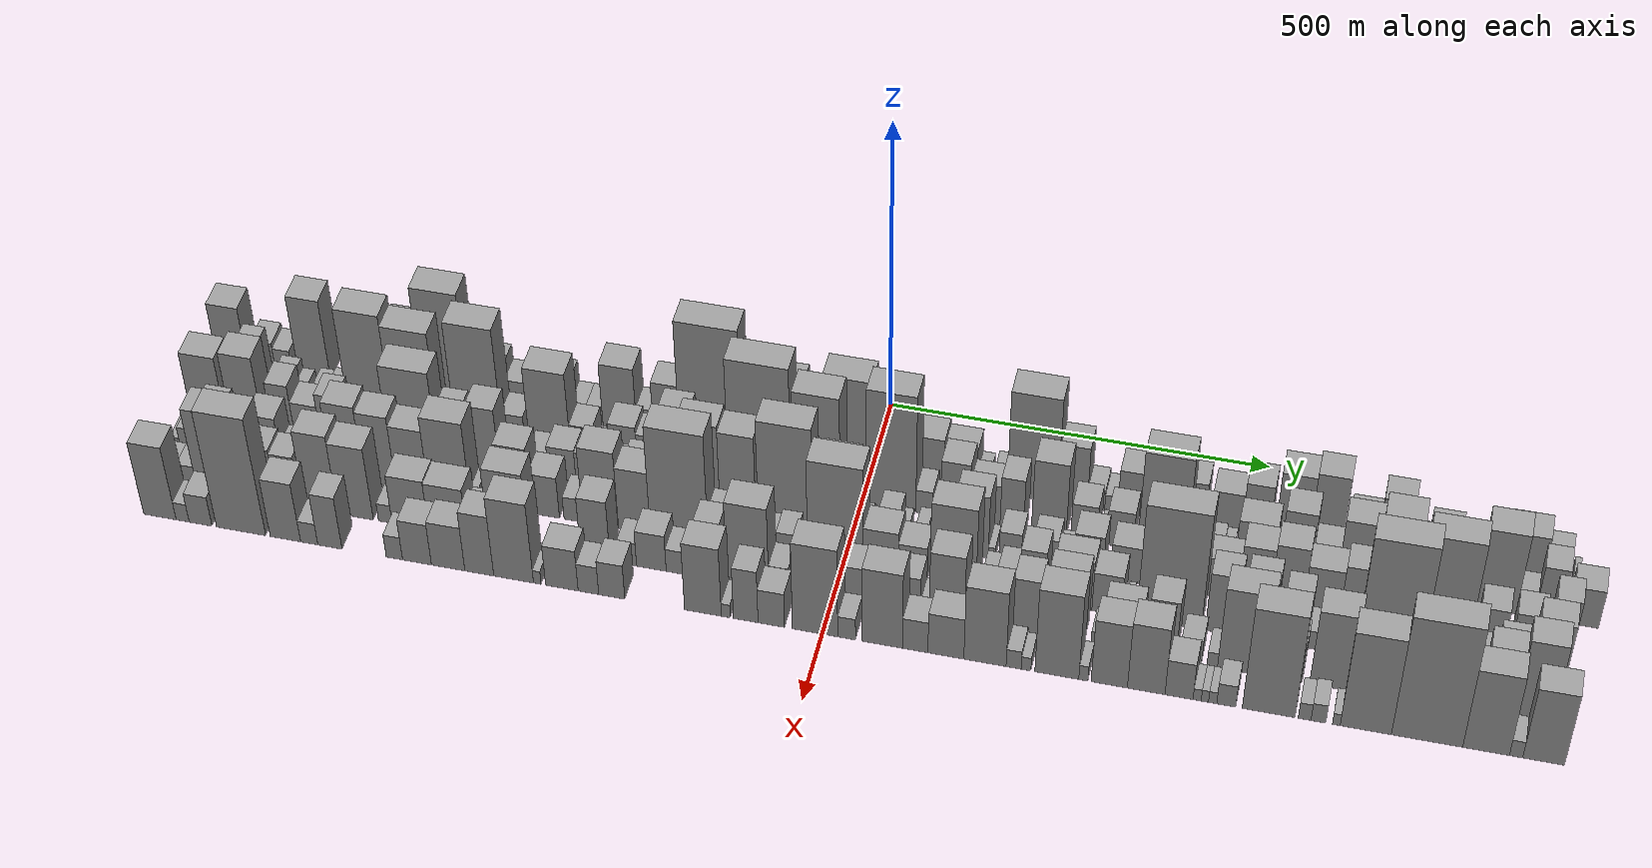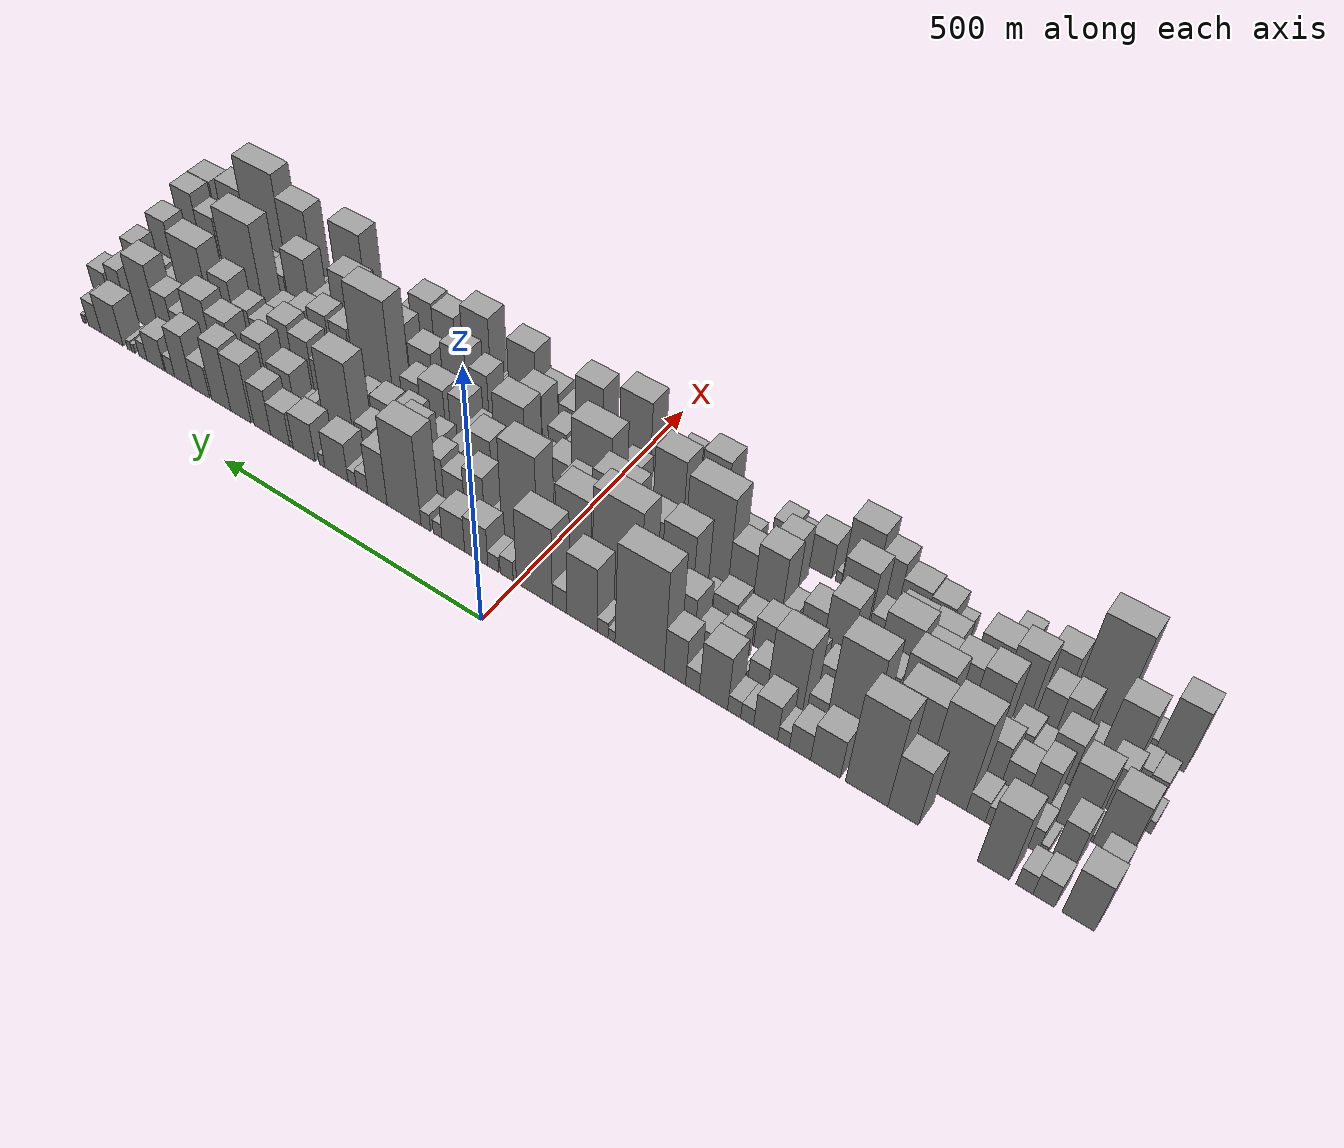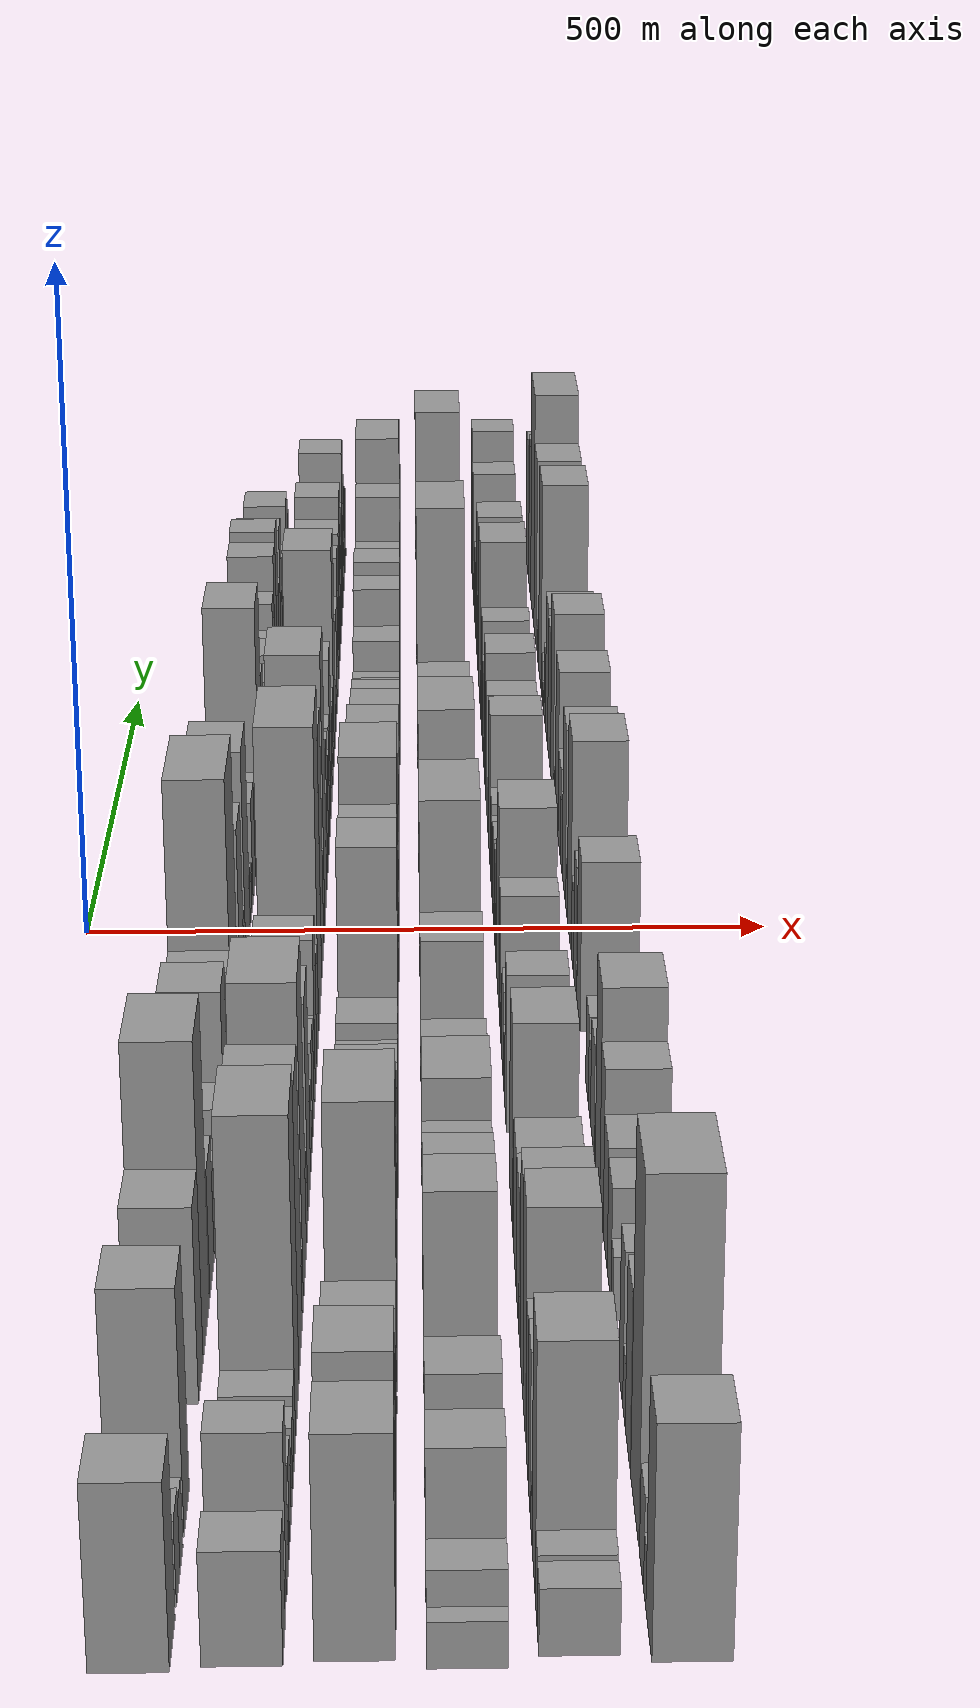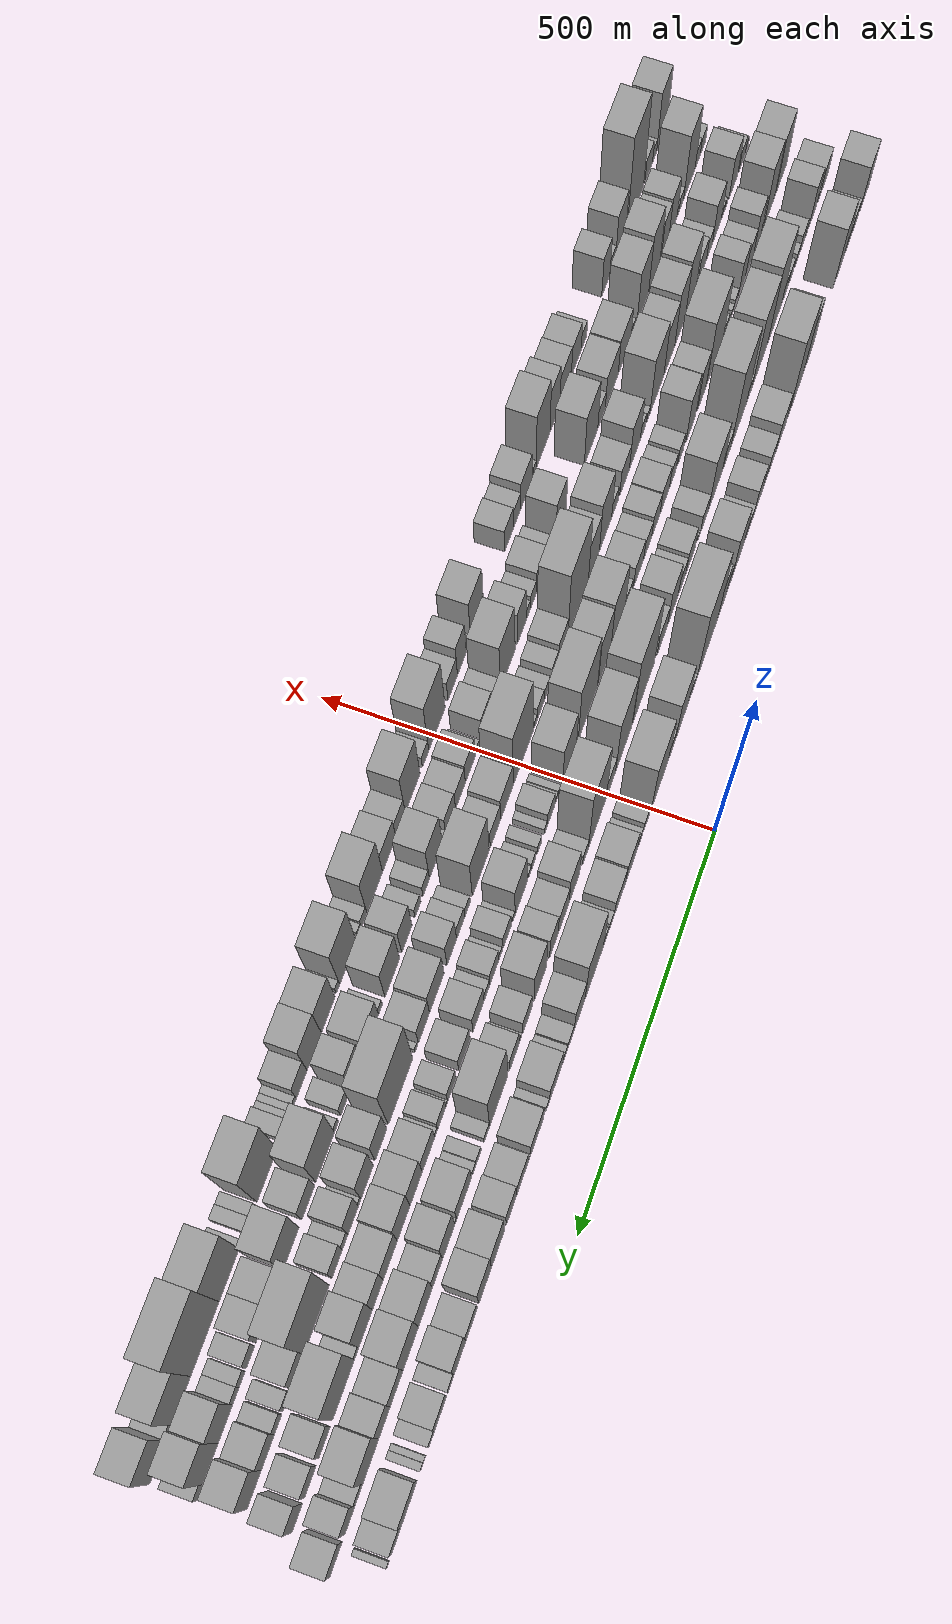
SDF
<sdf version="1.6">
 <world name="default">
  <scene>
   <sky><clouds><speed>12</speed></clouds></sky>
   <ambient>0.4 0.4 0.4 1</ambient>
   <background>0.7 0.7 0.7 1</background>
   <shadows>1</shadows>
  </scene>
  <gravity>0 0 -9.8066</gravity>
  <magnetic_field>6e-06 2.3e-05 -4.2e-05</magnetic_field>
  <physics default="0" name="default_physics" type="ode">
   <ode>
    <solver>
     <type>quick</type>
     <iters>10</iters>
     <sor>1.0</sor>
     <use_dynamic_moi_rescaling>0</use_dynamic_moi_rescaling>
    </solver>
    <constraints>
     <cfm>0</cfm>
     <erp>0.2</erp>
     <contact_max_correcting_vel>100</contact_max_correcting_vel>
     <contact_surface_layer>0.001</contact_surface_layer>
    </constraints>
   </ode>
   <max_step_size>0.004</max_step_size>
   <real_time_factor>1</real_time_factor>
   <real_time_update_rate>250</real_time_update_rate>
  </physics>
  <light name="sun" type="directional">
   <pose>0 0 10 0 0 0</pose>
   <diffuse>0.8 0.8 0.8 1</diffuse>
   <specular>0.2 0.2 0.2 1</specular>
   <attenuation>
    <range>1000</range>
    <constant>0.9</constant>
    <linear>0.01</linear>
    <quadratic>0.001</quadratic>
   </attenuation>
   <direction>-0.5 0.1 -0.9</direction>
  </light>
  <model name="building_1">
   <static>1</static>
   <pose>100.0000 -868.5117 0 0.000000 0.000000 0.000000</pose>
   <link name="link">
    <pose>0 0 54.00 0 0 0</pose>
    <collision name="collision"><geometry><box><size>40.0000 42.9765 108.0000</size></box></geometry></collision>
    <visual name="visual">
     <cast_shadows>0</cast_shadows>
     <geometry><box><size>40.0000 42.9765 108.0000</size></box></geometry>
     <material>
      <script>
       <uri>model://grey_wall/materials/scripts</uri>
       <uri>model://grey_wall/materials/textures</uri>
       <name>vrc/grey_wall</name>
      </script>
     </material>
    </visual>
   </link>
  </model>
  <model name="building_2">
   <static>1</static>
   <pose>100.0000 -822.4610 0 0.000000 0.000000 0.000000</pose>
   <link name="link">
    <pose>0 0 25.50 0 0 0</pose>
    <collision name="collision"><geometry><box><size>40.0000 29.1250 51.0000</size></box></geometry></collision>
    <visual name="visual">
     <cast_shadows>0</cast_shadows>
     <geometry><box><size>40.0000 29.1250 51.0000</size></box></geometry>
     <material>
      <script>
       <uri>model://grey_wall/materials/scripts</uri>
       <uri>model://grey_wall/materials/textures</uri>
       <name>vrc/grey_wall</name>
      </script>
     </material>
    </visual>
   </link>
  </model>
  <model name="building_3">
   <static>1</static>
   <pose>100.0000 -796.3106 0 0.000000 0.000000 0.000000</pose>
   <link name="link">
    <pose>0 0 21.00 0 0 0</pose>
    <collision name="collision"><geometry><box><size>40.0000 23.1758 42.0000</size></box></geometry></collision>
    <visual name="visual">
     <cast_shadows>0</cast_shadows>
     <geometry><box><size>40.0000 23.1758 42.0000</size></box></geometry>
     <material>
      <script>
       <uri>model://grey_wall/materials/scripts</uri>
       <uri>model://grey_wall/materials/textures</uri>
       <name>vrc/grey_wall</name>
      </script>
     </material>
    </visual>
   </link>
  </model>
  <model name="building_4">
   <static>1</static>
   <pose>100.0000 -753.5888 0 0.000000 0.000000 0.000000</pose>
   <link name="link">
    <pose>0 0 73.50 0 0 0</pose>
    <collision name="collision"><geometry><box><size>40.0000 44.2677 147.0000</size></box></geometry></collision>
    <visual name="visual">
     <cast_shadows>0</cast_shadows>
     <geometry><box><size>40.0000 44.2677 147.0000</size></box></geometry>
     <material>
      <script>
       <uri>model://grey_wall/materials/scripts</uri>
       <uri>model://grey_wall/materials/textures</uri>
       <name>vrc/grey_wall</name>
      </script>
     </material>
    </visual>
   </link>
  </model>
  <model name="building_5">
   <static>1</static>
   <pose>100.0000 -625.5442 0 0.000000 0.000000 0.000000</pose>
   <link name="link">
    <pose>0 0 61.50 0 0 0</pose>
    <collision name="collision"><geometry><box><size>40.0000 44.6072 123.0000</size></box></geometry></collision>
    <visual name="visual">
     <cast_shadows>0</cast_shadows>
     <geometry><box><size>40.0000 44.6072 123.0000</size></box></geometry>
     <material>
      <script>
       <uri>model://grey_wall/materials/scripts</uri>
       <uri>model://grey_wall/materials/textures</uri>
       <name>vrc/grey_wall</name>
      </script>
     </material>
    </visual>
   </link>
  </model>
  <model name="building_6">
   <static>1</static>
   <pose>100.0000 -571.9590 0 0.000000 0.000000 0.000000</pose>
   <link name="link">
    <pose>0 0 100.50 0 0 0</pose>
    <collision name="collision"><geometry><box><size>40.0000 62.5633 201.0000</size></box></geometry></collision>
    <visual name="visual">
     <cast_shadows>0</cast_shadows>
     <geometry><box><size>40.0000 62.5633 201.0000</size></box></geometry>
     <material>
      <script>
       <uri>model://grey_wall/materials/scripts</uri>
       <uri>model://grey_wall/materials/textures</uri>
       <name>vrc/grey_wall</name>
      </script>
     </material>
    </visual>
   </link>
  </model>
  <model name="building_7">
   <static>1</static>
   <pose>100.0000 -510.2132 0 0.000000 0.000000 0.000000</pose>
   <link name="link">
    <pose>0 0 42.00 0 0 0</pose>
    <collision name="collision"><geometry><box><size>40.0000 44.9282 84.0000</size></box></geometry></collision>
    <visual name="visual">
     <cast_shadows>0</cast_shadows>
     <geometry><box><size>40.0000 44.9282 84.0000</size></box></geometry>
     <material>
      <script>
       <uri>model://grey_wall/materials/scripts</uri>
       <uri>model://grey_wall/materials/textures</uri>
       <name>vrc/grey_wall</name>
      </script>
     </material>
    </visual>
   </link>
  </model>
  <model name="building_8">
   <static>1</static>
   <pose>100.0000 -471.4788 0 0.000000 0.000000 0.000000</pose>
   <link name="link">
    <pose>0 0 28.50 0 0 0</pose>
    <collision name="collision"><geometry><box><size>40.0000 32.5408 57.0000</size></box></geometry></collision>
    <visual name="visual">
     <cast_shadows>0</cast_shadows>
     <geometry><box><size>40.0000 32.5408 57.0000</size></box></geometry>
     <material>
      <script>
       <uri>model://grey_wall/materials/scripts</uri>
       <uri>model://grey_wall/materials/textures</uri>
       <name>vrc/grey_wall</name>
      </script>
     </material>
    </visual>
   </link>
  </model>
  <model name="building_9">
   <static>1</static>
   <pose>100.0000 -446.0469 0 0.000000 0.000000 0.000000</pose>
   <link name="link">
    <pose>0 0 16.50 0 0 0</pose>
    <collision name="collision"><geometry><box><size>40.0000 18.3229 33.0000</size></box></geometry></collision>
    <visual name="visual">
     <cast_shadows>0</cast_shadows>
     <geometry><box><size>40.0000 18.3229 33.0000</size></box></geometry>
     <material>
      <script>
       <uri>model://grey_wall/materials/scripts</uri>
       <uri>model://grey_wall/materials/textures</uri>
       <name>vrc/grey_wall</name>
      </script>
     </material>
    </visual>
   </link>
  </model>
  <model name="building_10">
   <static>1</static>
   <pose>100.0000 -418.1166 0 0.000000 0.000000 0.000000</pose>
   <link name="link">
    <pose>0 0 37.50 0 0 0</pose>
    <collision name="collision"><geometry><box><size>40.0000 37.5377 75.0000</size></box></geometry></collision>
    <visual name="visual">
     <cast_shadows>0</cast_shadows>
     <geometry><box><size>40.0000 37.5377 75.0000</size></box></geometry>
     <material>
      <script>
       <uri>model://grey_wall/materials/scripts</uri>
       <uri>model://grey_wall/materials/textures</uri>
       <name>vrc/grey_wall</name>
      </script>
     </material>
    </visual>
   </link>
  </model>
  <model name="building_11">
   <static>1</static>
   <pose>100.0000 -389.1185 0 0.000000 0.000000 0.000000</pose>
   <link name="link">
    <pose>0 0 18.00 0 0 0</pose>
    <collision name="collision"><geometry><box><size>40.0000 20.4583 36.0000</size></box></geometry></collision>
    <visual name="visual">
     <cast_shadows>0</cast_shadows>
     <geometry><box><size>40.0000 20.4583 36.0000</size></box></geometry>
     <material>
      <script>
       <uri>model://grey_wall/materials/scripts</uri>
       <uri>model://grey_wall/materials/textures</uri>
       <name>vrc/grey_wall</name>
      </script>
     </material>
    </visual>
   </link>
  </model>
  <model name="building_12">
   <static>1</static>
   <pose>100.0000 -368.4533 0 0.000000 0.000000 0.000000</pose>
   <link name="link">
    <pose>0 0 18.00 0 0 0</pose>
    <collision name="collision"><geometry><box><size>40.0000 20.8721 36.0000</size></box></geometry></collision>
    <visual name="visual">
     <cast_shadows>0</cast_shadows>
     <geometry><box><size>40.0000 20.8721 36.0000</size></box></geometry>
     <material>
      <script>
       <uri>model://grey_wall/materials/scripts</uri>
       <uri>model://grey_wall/materials/textures</uri>
       <name>vrc/grey_wall</name>
      </script>
     </material>
    </visual>
   </link>
  </model>
  <model name="building_13">
   <static>1</static>
   <pose>100.0000 -335.2118 0 0.000000 0.000000 0.000000</pose>
   <link name="link">
    <pose>0 0 58.50 0 0 0</pose>
    <collision name="collision"><geometry><box><size>40.0000 45.6110 117.0000</size></box></geometry></collision>
    <visual name="visual">
     <cast_shadows>0</cast_shadows>
     <geometry><box><size>40.0000 45.6110 117.0000</size></box></geometry>
     <material>
      <script>
       <uri>model://grey_wall/materials/scripts</uri>
       <uri>model://grey_wall/materials/textures</uri>
       <name>vrc/grey_wall</name>
      </script>
     </material>
    </visual>
   </link>
  </model>
  <model name="building_14">
   <static>1</static>
   <pose>100.0000 -301.1327 0 0.000000 0.000000 0.000000</pose>
   <link name="link">
    <pose>0 0 22.50 0 0 0</pose>
    <collision name="collision"><geometry><box><size>40.0000 22.5473 45.0000</size></box></geometry></collision>
    <visual name="visual">
     <cast_shadows>0</cast_shadows>
     <geometry><box><size>40.0000 22.5473 45.0000</size></box></geometry>
     <material>
      <script>
       <uri>model://grey_wall/materials/scripts</uri>
       <uri>model://grey_wall/materials/textures</uri>
       <name>vrc/grey_wall</name>
      </script>
     </material>
    </visual>
   </link>
  </model>
  <model name="building_15">
   <static>1</static>
   <pose>100.0000 -272.3482 0 0.000000 0.000000 0.000000</pose>
   <link name="link">
    <pose>0 0 49.50 0 0 0</pose>
    <collision name="collision"><geometry><box><size>40.0000 35.0216 99.0000</size></box></geometry></collision>
    <visual name="visual">
     <cast_shadows>0</cast_shadows>
     <geometry><box><size>40.0000 35.0216 99.0000</size></box></geometry>
     <material>
      <script>
       <uri>model://grey_wall/materials/scripts</uri>
       <uri>model://grey_wall/materials/textures</uri>
       <name>vrc/grey_wall</name>
      </script>
     </material>
    </visual>
   </link>
  </model>
  <model name="building_16">
   <static>1</static>
   <pose>100.0000 -213.4402 0 0.000000 0.000000 0.000000</pose>
   <link name="link">
    <pose>0 0 109.50 0 0 0</pose>
    <collision name="collision"><geometry><box><size>40.0000 82.7944 219.0000</size></box></geometry></collision>
    <visual name="visual">
     <cast_shadows>0</cast_shadows>
     <geometry><box><size>40.0000 82.7944 219.0000</size></box></geometry>
     <material>
      <script>
       <uri>model://grey_wall/materials/scripts</uri>
       <uri>model://grey_wall/materials/textures</uri>
       <name>vrc/grey_wall</name>
      </script>
     </material>
    </visual>
   </link>
  </model>
  <model name="building_17">
   <static>1</static>
   <pose>100.0000 -166.0867 0 0.000000 0.000000 0.000000</pose>
   <link name="link">
    <pose>0 0 12.00 0 0 0</pose>
    <collision name="collision"><geometry><box><size>40.0000 11.9127 24.0000</size></box></geometry></collision>
    <visual name="visual">
     <cast_shadows>0</cast_shadows>
     <geometry><box><size>40.0000 11.9127 24.0000</size></box></geometry>
     <material>
      <script>
       <uri>model://grey_wall/materials/scripts</uri>
       <uri>model://grey_wall/materials/textures</uri>
       <name>vrc/grey_wall</name>
      </script>
     </material>
    </visual>
   </link>
  </model>
  <model name="building_18">
   <static>1</static>
   <pose>100.0000 -150.8019 0 0.000000 0.000000 0.000000</pose>
   <link name="link">
    <pose>0 0 16.50 0 0 0</pose>
    <collision name="collision"><geometry><box><size>40.0000 18.6569 33.0000</size></box></geometry></collision>
    <visual name="visual">
     <cast_shadows>0</cast_shadows>
     <geometry><box><size>40.0000 18.6569 33.0000</size></box></geometry>
     <material>
      <script>
       <uri>model://grey_wall/materials/scripts</uri>
       <uri>model://grey_wall/materials/textures</uri>
       <name>vrc/grey_wall</name>
      </script>
     </material>
    </visual>
   </link>
  </model>
  <model name="building_19">
   <static>1</static>
   <pose>100.0000 -115.2629 0 0.000000 0.000000 0.000000</pose>
   <link name="link">
    <pose>0 0 69.00 0 0 0</pose>
    <collision name="collision"><geometry><box><size>40.0000 52.4211 138.0000</size></box></geometry></collision>
    <visual name="visual">
     <cast_shadows>0</cast_shadows>
     <geometry><box><size>40.0000 52.4211 138.0000</size></box></geometry>
     <material>
      <script>
       <uri>model://grey_wall/materials/scripts</uri>
       <uri>model://grey_wall/materials/textures</uri>
       <name>vrc/grey_wall</name>
      </script>
     </material>
    </visual>
   </link>
  </model>
  <model name="building_20">
   <static>1</static>
   <pose>100.0000 -76.1995 0 0.000000 0.000000 0.000000</pose>
   <link name="link">
    <pose>0 0 24.00 0 0 0</pose>
    <collision name="collision"><geometry><box><size>40.0000 25.7056 48.0000</size></box></geometry></collision>
    <visual name="visual">
     <cast_shadows>0</cast_shadows>
     <geometry><box><size>40.0000 25.7056 48.0000</size></box></geometry>
     <material>
      <script>
       <uri>model://grey_wall/materials/scripts</uri>
       <uri>model://grey_wall/materials/textures</uri>
       <name>vrc/grey_wall</name>
      </script>
     </material>
    </visual>
   </link>
  </model>
  <model name="building_21">
   <static>1</static>
   <pose>100.0000 -31.2883 0 0.000000 0.000000 0.000000</pose>
   <link name="link">
    <pose>0 0 82.50 0 0 0</pose>
    <collision name="collision"><geometry><box><size>40.0000 64.1168 165.0000</size></box></geometry></collision>
    <visual name="visual">
     <cast_shadows>0</cast_shadows>
     <geometry><box><size>40.0000 64.1168 165.0000</size></box></geometry>
     <material>
      <script>
       <uri>model://grey_wall/materials/scripts</uri>
       <uri>model://grey_wall/materials/textures</uri>
       <name>vrc/grey_wall</name>
      </script>
     </material>
    </visual>
   </link>
  </model>
  <model name="building_22">
   <static>1</static>
   <pose>100.0000 18.5439 0 0.000000 0.000000 0.000000</pose>
   <link name="link">
    <pose>0 0 21.00 0 0 0</pose>
    <collision name="collision"><geometry><box><size>40.0000 23.5476 42.0000</size></box></geometry></collision>
    <visual name="visual">
     <cast_shadows>0</cast_shadows>
     <geometry><box><size>40.0000 23.5476 42.0000</size></box></geometry>
     <material>
      <script>
       <uri>model://grey_wall/materials/scripts</uri>
       <uri>model://grey_wall/materials/textures</uri>
       <name>vrc/grey_wall</name>
      </script>
     </material>
    </visual>
   </link>
  </model>
  <model name="building_23">
   <static>1</static>
   <pose>100.0000 43.1436 0 0.000000 0.000000 0.000000</pose>
   <link name="link">
    <pose>0 0 16.50 0 0 0</pose>
    <collision name="collision"><geometry><box><size>40.0000 19.6517 33.0000</size></box></geometry></collision>
    <visual name="visual">
     <cast_shadows>0</cast_shadows>
     <geometry><box><size>40.0000 19.6517 33.0000</size></box></geometry>
     <material>
      <script>
       <uri>model://grey_wall/materials/scripts</uri>
       <uri>model://grey_wall/materials/textures</uri>
       <name>vrc/grey_wall</name>
      </script>
     </material>
    </visual>
   </link>
  </model>
  <model name="building_24">
   <static>1</static>
   <pose>100.0000 74.4396 0 0.000000 0.000000 0.000000</pose>
   <link name="link">
    <pose>0 0 40.50 0 0 0</pose>
    <collision name="collision"><geometry><box><size>40.0000 42.9403 81.0000</size></box></geometry></collision>
    <visual name="visual">
     <cast_shadows>0</cast_shadows>
     <geometry><box><size>40.0000 42.9403 81.0000</size></box></geometry>
     <material>
      <script>
       <uri>model://grey_wall/materials/scripts</uri>
       <uri>model://grey_wall/materials/textures</uri>
       <name>vrc/grey_wall</name>
      </script>
     </material>
    </visual>
   </link>
  </model>
  <model name="building_25">
   <static>1</static>
   <pose>100.0000 117.2887 0 0.000000 0.000000 0.000000</pose>
   <link name="link">
    <pose>0 0 36.00 0 0 0</pose>
    <collision name="collision"><geometry><box><size>40.0000 42.7581 72.0000</size></box></geometry></collision>
    <visual name="visual">
     <cast_shadows>0</cast_shadows>
     <geometry><box><size>40.0000 42.7581 72.0000</size></box></geometry>
     <material>
      <script>
       <uri>model://grey_wall/materials/scripts</uri>
       <uri>model://grey_wall/materials/textures</uri>
       <name>vrc/grey_wall</name>
      </script>
     </material>
    </visual>
   </link>
  </model>
  <model name="building_26">
   <static>1</static>
   <pose>100.0000 146.9715 0 0.000000 0.000000 0.000000</pose>
   <link name="link">
    <pose>0 0 15.00 0 0 0</pose>
    <collision name="collision"><geometry><box><size>40.0000 16.6075 30.0000</size></box></geometry></collision>
    <visual name="visual">
     <cast_shadows>0</cast_shadows>
     <geometry><box><size>40.0000 16.6075 30.0000</size></box></geometry>
     <material>
      <script>
       <uri>model://grey_wall/materials/scripts</uri>
       <uri>model://grey_wall/materials/textures</uri>
       <name>vrc/grey_wall</name>
      </script>
     </material>
    </visual>
   </link>
  </model>
  <model name="building_27">
   <static>1</static>
   <pose>100.0000 169.2999 0 0.000000 0.000000 0.000000</pose>
   <link name="link">
    <pose>0 0 18.00 0 0 0</pose>
    <collision name="collision"><geometry><box><size>40.0000 18.0493 36.0000</size></box></geometry></collision>
    <visual name="visual">
     <cast_shadows>0</cast_shadows>
     <geometry><box><size>40.0000 18.0493 36.0000</size></box></geometry>
     <material>
      <script>
       <uri>model://grey_wall/materials/scripts</uri>
       <uri>model://grey_wall/materials/textures</uri>
       <name>vrc/grey_wall</name>
      </script>
     </material>
    </visual>
   </link>
  </model>
  <model name="building_28">
   <static>1</static>
   <pose>100.0000 211.1221 0 0.000000 0.000000 0.000000</pose>
   <link name="link">
    <pose>0 0 96.00 0 0 0</pose>
    <collision name="collision"><geometry><box><size>40.0000 65.5950 192.0000</size></box></geometry></collision>
    <visual name="visual">
     <cast_shadows>0</cast_shadows>
     <geometry><box><size>40.0000 65.5950 192.0000</size></box></geometry>
     <material>
      <script>
       <uri>model://grey_wall/materials/scripts</uri>
       <uri>model://grey_wall/materials/textures</uri>
       <name>vrc/grey_wall</name>
      </script>
     </material>
    </visual>
   </link>
  </model>
  <model name="building_29">
   <static>1</static>
   <pose>100.0000 262.9769 0 0.000000 0.000000 0.000000</pose>
   <link name="link">
    <pose>0 0 55.50 0 0 0</pose>
    <collision name="collision"><geometry><box><size>40.0000 38.1147 111.0000</size></box></geometry></collision>
    <visual name="visual">
     <cast_shadows>0</cast_shadows>
     <geometry><box><size>40.0000 38.1147 111.0000</size></box></geometry>
     <material>
      <script>
       <uri>model://grey_wall/materials/scripts</uri>
       <uri>model://grey_wall/materials/textures</uri>
       <name>vrc/grey_wall</name>
      </script>
     </material>
    </visual>
   </link>
  </model>
  <model name="building_30">
   <static>1</static>
   <pose>100.0000 293.4350 0 0.000000 0.000000 0.000000</pose>
   <link name="link">
    <pose>0 0 19.50 0 0 0</pose>
    <collision name="collision"><geometry><box><size>40.0000 22.8015 39.0000</size></box></geometry></collision>
    <visual name="visual">
     <cast_shadows>0</cast_shadows>
     <geometry><box><size>40.0000 22.8015 39.0000</size></box></geometry>
     <material>
      <script>
       <uri>model://grey_wall/materials/scripts</uri>
       <uri>model://grey_wall/materials/textures</uri>
       <name>vrc/grey_wall</name>
      </script>
     </material>
    </visual>
   </link>
  </model>
  <model name="building_31">
   <static>1</static>
   <pose>100.0000 313.0862 0 0.000000 0.000000 0.000000</pose>
   <link name="link">
    <pose>0 0 15.00 0 0 0</pose>
    <collision name="collision"><geometry><box><size>40.0000 16.5010 30.0000</size></box></geometry></collision>
    <visual name="visual">
     <cast_shadows>0</cast_shadows>
     <geometry><box><size>40.0000 16.5010 30.0000</size></box></geometry>
     <material>
      <script>
       <uri>model://grey_wall/materials/scripts</uri>
       <uri>model://grey_wall/materials/textures</uri>
       <name>vrc/grey_wall</name>
      </script>
     </material>
    </visual>
   </link>
  </model>
  <model name="building_32">
   <static>1</static>
   <pose>100.0000 344.8873 0 0.000000 0.000000 0.000000</pose>
   <link name="link">
    <pose>0 0 40.50 0 0 0</pose>
    <collision name="collision"><geometry><box><size>40.0000 47.1013 81.0000</size></box></geometry></collision>
    <visual name="visual">
     <cast_shadows>0</cast_shadows>
     <geometry><box><size>40.0000 47.1013 81.0000</size></box></geometry>
     <material>
      <script>
       <uri>model://grey_wall/materials/scripts</uri>
       <uri>model://grey_wall/materials/textures</uri>
       <name>vrc/grey_wall</name>
      </script>
     </material>
    </visual>
   </link>
  </model>
  <model name="building_33">
   <static>1</static>
   <pose>100.0000 374.2250 0 0.000000 0.000000 0.000000</pose>
   <link name="link">
    <pose>0 0 13.50 0 0 0</pose>
    <collision name="collision"><geometry><box><size>40.0000 11.5741 27.0000</size></box></geometry></collision>
    <visual name="visual">
     <cast_shadows>0</cast_shadows>
     <geometry><box><size>40.0000 11.5741 27.0000</size></box></geometry>
     <material>
      <script>
       <uri>model://grey_wall/materials/scripts</uri>
       <uri>model://grey_wall/materials/textures</uri>
       <name>vrc/grey_wall</name>
      </script>
     </material>
    </visual>
   </link>
  </model>
  <model name="building_34">
   <static>1</static>
   <pose>100.0000 410.7948 0 0.000000 0.000000 0.000000</pose>
   <link name="link">
    <pose>0 0 40.50 0 0 0</pose>
    <collision name="collision"><geometry><box><size>40.0000 45.5656 81.0000</size></box></geometry></collision>
    <visual name="visual">
     <cast_shadows>0</cast_shadows>
     <geometry><box><size>40.0000 45.5656 81.0000</size></box></geometry>
     <material>
      <script>
       <uri>model://grey_wall/materials/scripts</uri>
       <uri>model://grey_wall/materials/textures</uri>
       <name>vrc/grey_wall</name>
      </script>
     </material>
    </visual>
   </link>
  </model>
  <model name="building_35">
   <static>1</static>
   <pose>100.0000 436.9361 0 0.000000 0.000000 0.000000</pose>
   <link name="link">
    <pose>0 0 7.50 0 0 0</pose>
    <collision name="collision"><geometry><box><size>40.0000 6.7169 15.0000</size></box></geometry></collision>
    <visual name="visual">
     <cast_shadows>0</cast_shadows>
     <geometry><box><size>40.0000 6.7169 15.0000</size></box></geometry>
     <material>
      <script>
       <uri>model://grey_wall/materials/scripts</uri>
       <uri>model://grey_wall/materials/textures</uri>
       <name>vrc/grey_wall</name>
      </script>
     </material>
    </visual>
   </link>
  </model>
  <model name="building_36">
   <static>1</static>
   <pose>100.0000 460.3819 0 0.000000 0.000000 0.000000</pose>
   <link name="link">
    <pose>0 0 36.00 0 0 0</pose>
    <collision name="collision"><geometry><box><size>40.0000 40.1748 72.0000</size></box></geometry></collision>
    <visual name="visual">
     <cast_shadows>0</cast_shadows>
     <geometry><box><size>40.0000 40.1748 72.0000</size></box></geometry>
     <material>
      <script>
       <uri>model://grey_wall/materials/scripts</uri>
       <uri>model://grey_wall/materials/textures</uri>
       <name>vrc/grey_wall</name>
      </script>
     </material>
    </visual>
   </link>
  </model>
  <model name="building_37">
   <static>1</static>
   <pose>100.0000 498.3153 0 0.000000 0.000000 0.000000</pose>
   <link name="link">
    <pose>0 0 48.00 0 0 0</pose>
    <collision name="collision"><geometry><box><size>40.0000 35.6922 96.0000</size></box></geometry></collision>
    <visual name="visual">
     <cast_shadows>0</cast_shadows>
     <geometry><box><size>40.0000 35.6922 96.0000</size></box></geometry>
     <material>
      <script>
       <uri>model://grey_wall/materials/scripts</uri>
       <uri>model://grey_wall/materials/textures</uri>
       <name>vrc/grey_wall</name>
      </script>
     </material>
    </visual>
   </link>
  </model>
  <model name="building_38">
   <static>1</static>
   <pose>100.0000 544.0943 0 0.000000 0.000000 0.000000</pose>
   <link name="link">
    <pose>0 0 63.00 0 0 0</pose>
    <collision name="collision"><geometry><box><size>40.0000 43.8658 126.0000</size></box></geometry></collision>
    <visual name="visual">
     <cast_shadows>0</cast_shadows>
     <geometry><box><size>40.0000 43.8658 126.0000</size></box></geometry>
     <material>
      <script>
       <uri>model://grey_wall/materials/scripts</uri>
       <uri>model://grey_wall/materials/textures</uri>
       <name>vrc/grey_wall</name>
      </script>
     </material>
    </visual>
   </link>
  </model>
  <model name="building_39">
   <static>1</static>
   <pose>100.0000 586.6862 0 0.000000 0.000000 0.000000</pose>
   <link name="link">
    <pose>0 0 67.50 0 0 0</pose>
    <collision name="collision"><geometry><box><size>40.0000 41.3181 135.0000</size></box></geometry></collision>
    <visual name="visual">
     <cast_shadows>0</cast_shadows>
     <geometry><box><size>40.0000 41.3181 135.0000</size></box></geometry>
     <material>
      <script>
       <uri>model://grey_wall/materials/scripts</uri>
       <uri>model://grey_wall/materials/textures</uri>
       <name>vrc/grey_wall</name>
      </script>
     </material>
    </visual>
   </link>
  </model>
  <model name="building_40">
   <static>1</static>
   <pose>100.0000 631.5198 0 0.000000 0.000000 0.000000</pose>
   <link name="link">
    <pose>0 0 33.00 0 0 0</pose>
    <collision name="collision"><geometry><box><size>40.0000 38.3491 66.0000</size></box></geometry></collision>
    <visual name="visual">
     <cast_shadows>0</cast_shadows>
     <geometry><box><size>40.0000 38.3491 66.0000</size></box></geometry>
     <material>
      <script>
       <uri>model://grey_wall/materials/scripts</uri>
       <uri>model://grey_wall/materials/textures</uri>
       <name>vrc/grey_wall</name>
      </script>
     </material>
    </visual>
   </link>
  </model>
  <model name="building_41">
   <static>1</static>
   <pose>100.0000 670.0750 0 0.000000 0.000000 0.000000</pose>
   <link name="link">
    <pose>0 0 55.50 0 0 0</pose>
    <collision name="collision"><geometry><box><size>40.0000 38.7613 111.0000</size></box></geometry></collision>
    <visual name="visual">
     <cast_shadows>0</cast_shadows>
     <geometry><box><size>40.0000 38.7613 111.0000</size></box></geometry>
     <material>
      <script>
       <uri>model://grey_wall/materials/scripts</uri>
       <uri>model://grey_wall/materials/textures</uri>
       <name>vrc/grey_wall</name>
      </script>
     </material>
    </visual>
   </link>
  </model>
  <model name="building_42">
   <static>1</static>
   <pose>100.0000 699.5304 0 0.000000 0.000000 0.000000</pose>
   <link name="link">
    <pose>0 0 19.50 0 0 0</pose>
    <collision name="collision"><geometry><box><size>40.0000 20.1496 39.0000</size></box></geometry></collision>
    <visual name="visual">
     <cast_shadows>0</cast_shadows>
     <geometry><box><size>40.0000 20.1496 39.0000</size></box></geometry>
     <material>
      <script>
       <uri>model://grey_wall/materials/scripts</uri>
       <uri>model://grey_wall/materials/textures</uri>
       <name>vrc/grey_wall</name>
      </script>
     </material>
    </visual>
   </link>
  </model>
  <model name="building_43">
   <static>1</static>
   <pose>100.0000 732.3877 0 0.000000 0.000000 0.000000</pose>
   <link name="link">
    <pose>0 0 33.00 0 0 0</pose>
    <collision name="collision"><geometry><box><size>40.0000 39.5649 66.0000</size></box></geometry></collision>
    <visual name="visual">
     <cast_shadows>0</cast_shadows>
     <geometry><box><size>40.0000 39.5649 66.0000</size></box></geometry>
     <material>
      <script>
       <uri>model://grey_wall/materials/scripts</uri>
       <uri>model://grey_wall/materials/textures</uri>
       <name>vrc/grey_wall</name>
      </script>
     </material>
    </visual>
   </link>
  </model>
  <model name="building_44">
   <static>1</static>
   <pose>100.0000 761.4699 0 0.000000 0.000000 0.000000</pose>
   <link name="link">
    <pose>0 0 18.00 0 0 0</pose>
    <collision name="collision"><geometry><box><size>40.0000 18.5997 36.0000</size></box></geometry></collision>
    <visual name="visual">
     <cast_shadows>0</cast_shadows>
     <geometry><box><size>40.0000 18.5997 36.0000</size></box></geometry>
     <material>
      <script>
       <uri>model://grey_wall/materials/scripts</uri>
       <uri>model://grey_wall/materials/textures</uri>
       <name>vrc/grey_wall</name>
      </script>
     </material>
    </visual>
   </link>
  </model>
  <model name="building_45">
   <static>1</static>
   <pose>100.0000 783.6914 0 0.000000 0.000000 0.000000</pose>
   <link name="link">
    <pose>0 0 9.00 0 0 0</pose>
    <collision name="collision"><geometry><box><size>40.0000 7.8432 18.0000</size></box></geometry></collision>
    <visual name="visual">
     <cast_shadows>0</cast_shadows>
     <geometry><box><size>40.0000 7.8432 18.0000</size></box></geometry>
     <material>
      <script>
       <uri>model://grey_wall/materials/scripts</uri>
       <uri>model://grey_wall/materials/textures</uri>
       <name>vrc/grey_wall</name>
      </script>
     </material>
    </visual>
   </link>
  </model>
  <model name="building_46">
   <static>1</static>
   <pose>100.0000 792.5632 0 0.000000 0.000000 0.000000</pose>
   <link name="link">
    <pose>0 0 10.50 0 0 0</pose>
    <collision name="collision"><geometry><box><size>40.0000 9.9006 21.0000</size></box></geometry></collision>
    <visual name="visual">
     <cast_shadows>0</cast_shadows>
     <geometry><box><size>40.0000 9.9006 21.0000</size></box></geometry>
     <material>
      <script>
       <uri>model://grey_wall/materials/scripts</uri>
       <uri>model://grey_wall/materials/textures</uri>
       <name>vrc/grey_wall</name>
      </script>
     </material>
    </visual>
   </link>
  </model>
  <model name="building_47">
   <static>1</static>
   <pose>100.0000 833.2437 0 0.000000 0.000000 0.000000</pose>
   <link name="link">
    <pose>0 0 43.50 0 0 0</pose>
    <collision name="collision"><geometry><box><size>40.0000 51.4604 87.0000</size></box></geometry></collision>
    <visual name="visual">
     <cast_shadows>0</cast_shadows>
     <geometry><box><size>40.0000 51.4604 87.0000</size></box></geometry>
     <material>
      <script>
       <uri>model://grey_wall/materials/scripts</uri>
       <uri>model://grey_wall/materials/textures</uri>
       <name>vrc/grey_wall</name>
      </script>
     </material>
    </visual>
   </link>
  </model>
  <model name="building_48">
   <static>1</static>
   <pose>100.0000 874.0777 0 0.000000 0.000000 0.000000</pose>
   <link name="link">
    <pose>0 0 30.00 0 0 0</pose>
    <collision name="collision"><geometry><box><size>40.0000 30.2076 60.0000</size></box></geometry></collision>
    <visual name="visual">
     <cast_shadows>0</cast_shadows>
     <geometry><box><size>40.0000 30.2076 60.0000</size></box></geometry>
     <material>
      <script>
       <uri>model://grey_wall/materials/scripts</uri>
       <uri>model://grey_wall/materials/textures</uri>
       <name>vrc/grey_wall</name>
      </script>
     </material>
    </visual>
   </link>
  </model>
  <model name="building_49">
   <static>1</static>
   <pose>100.0000 899.2437 0 0.000000 0.000000 0.000000</pose>
   <link name="link">
    <pose>0 0 9.00 0 0 0</pose>
    <collision name="collision"><geometry><box><size>40.0000 8.1243 18.0000</size></box></geometry></collision>
    <visual name="visual">
     <cast_shadows>0</cast_shadows>
     <geometry><box><size>40.0000 8.1243 18.0000</size></box></geometry>
     <material>
      <script>
       <uri>model://grey_wall/materials/scripts</uri>
       <uri>model://grey_wall/materials/textures</uri>
       <name>vrc/grey_wall</name>
      </script>
     </material>
    </visual>
   </link>
  </model>
  <model name="building_50">
   <static>1</static>
   <pose>155.0000 -868.8638 0 0.000000 0.000000 0.000000</pose>
   <link name="link">
    <pose>0 0 33.00 0 0 0</pose>
    <collision name="collision"><geometry><box><size>40.0000 34.2724 66.0000</size></box></geometry></collision>
    <visual name="visual">
     <cast_shadows>0</cast_shadows>
     <geometry><box><size>40.0000 34.2724 66.0000</size></box></geometry>
     <material>
      <script>
       <uri>model://grey_wall/materials/scripts</uri>
       <uri>model://grey_wall/materials/textures</uri>
       <name>vrc/grey_wall</name>
      </script>
     </material>
    </visual>
   </link>
  </model>
  <model name="building_51">
   <static>1</static>
   <pose>155.0000 -847.3205 0 0.000000 0.000000 0.000000</pose>
   <link name="link">
    <pose>0 0 10.50 0 0 0</pose>
    <collision name="collision"><geometry><box><size>40.0000 8.8141 21.0000</size></box></geometry></collision>
    <visual name="visual">
     <cast_shadows>0</cast_shadows>
     <geometry><box><size>40.0000 8.8141 21.0000</size></box></geometry>
     <material>
      <script>
       <uri>model://grey_wall/materials/scripts</uri>
       <uri>model://grey_wall/materials/textures</uri>
       <name>vrc/grey_wall</name>
      </script>
     </material>
    </visual>
   </link>
  </model>
  <model name="building_52">
   <static>1</static>
   <pose>155.0000 -818.9141 0 0.000000 0.000000 0.000000</pose>
   <link name="link">
    <pose>0 0 49.50 0 0 0</pose>
    <collision name="collision"><geometry><box><size>40.0000 29.9987 99.0000</size></box></geometry></collision>
    <visual name="visual">
     <cast_shadows>0</cast_shadows>
     <geometry><box><size>40.0000 29.9987 99.0000</size></box></geometry>
     <material>
      <script>
       <uri>model://grey_wall/materials/scripts</uri>
       <uri>model://grey_wall/materials/textures</uri>
       <name>vrc/grey_wall</name>
      </script>
     </material>
    </visual>
   </link>
  </model>
  <model name="building_53">
   <static>1</static>
   <pose>155.0000 -792.4140 0 0.000000 0.000000 0.000000</pose>
   <link name="link">
    <pose>0 0 12.00 0 0 0</pose>
    <collision name="collision"><geometry><box><size>40.0000 11.0015 24.0000</size></box></geometry></collision>
    <visual name="visual">
     <cast_shadows>0</cast_shadows>
     <geometry><box><size>40.0000 11.0015 24.0000</size></box></geometry>
     <material>
      <script>
       <uri>model://grey_wall/materials/scripts</uri>
       <uri>model://grey_wall/materials/textures</uri>
       <name>vrc/grey_wall</name>
      </script>
     </material>
    </visual>
   </link>
  </model>
  <model name="building_54">
   <static>1</static>
   <pose>155.0000 -773.8218 0 0.000000 0.000000 0.000000</pose>
   <link name="link">
    <pose>0 0 25.50 0 0 0</pose>
    <collision name="collision"><geometry><box><size>40.0000 26.1829 51.0000</size></box></geometry></collision>
    <visual name="visual">
     <cast_shadows>0</cast_shadows>
     <geometry><box><size>40.0000 26.1829 51.0000</size></box></geometry>
     <material>
      <script>
       <uri>model://grey_wall/materials/scripts</uri>
       <uri>model://grey_wall/materials/textures</uri>
       <name>vrc/grey_wall</name>
      </script>
     </material>
    </visual>
   </link>
  </model>
  <model name="building_55">
   <static>1</static>
   <pose>155.0000 -752.4143 0 0.000000 0.000000 0.000000</pose>
   <link name="link">
    <pose>0 0 16.50 0 0 0</pose>
    <collision name="collision"><geometry><box><size>40.0000 16.6319 33.0000</size></box></geometry></collision>
    <visual name="visual">
     <cast_shadows>0</cast_shadows>
     <geometry><box><size>40.0000 16.6319 33.0000</size></box></geometry>
     <material>
      <script>
       <uri>model://grey_wall/materials/scripts</uri>
       <uri>model://grey_wall/materials/textures</uri>
       <name>vrc/grey_wall</name>
      </script>
     </material>
    </visual>
   </link>
  </model>
  <model name="building_56">
   <static>1</static>
   <pose>155.0000 -724.2206 0 0.000000 0.000000 0.000000</pose>
   <link name="link">
    <pose>0 0 19.50 0 0 0</pose>
    <collision name="collision"><geometry><box><size>40.0000 21.7556 39.0000</size></box></geometry></collision>
    <visual name="visual">
     <cast_shadows>0</cast_shadows>
     <geometry><box><size>40.0000 21.7556 39.0000</size></box></geometry>
     <material>
      <script>
       <uri>model://grey_wall/materials/scripts</uri>
       <uri>model://grey_wall/materials/textures</uri>
       <name>vrc/grey_wall</name>
      </script>
     </material>
    </visual>
   </link>
  </model>
  <model name="building_57">
   <static>1</static>
   <pose>155.0000 -699.9777 0 0.000000 0.000000 0.000000</pose>
   <link name="link">
    <pose>0 0 22.50 0 0 0</pose>
    <collision name="collision"><geometry><box><size>40.0000 26.7302 45.0000</size></box></geometry></collision>
    <visual name="visual">
     <cast_shadows>0</cast_shadows>
     <geometry><box><size>40.0000 26.7302 45.0000</size></box></geometry>
     <material>
      <script>
       <uri>model://grey_wall/materials/scripts</uri>
       <uri>model://grey_wall/materials/textures</uri>
       <name>vrc/grey_wall</name>
      </script>
     </material>
    </visual>
   </link>
  </model>
  <model name="building_58">
   <static>1</static>
   <pose>155.0000 -656.6548 0 0.000000 0.000000 0.000000</pose>
   <link name="link">
    <pose>0 0 99.00 0 0 0</pose>
    <collision name="collision"><geometry><box><size>40.0000 59.9157 198.0000</size></box></geometry></collision>
    <visual name="visual">
     <cast_shadows>0</cast_shadows>
     <geometry><box><size>40.0000 59.9157 198.0000</size></box></geometry>
     <material>
      <script>
       <uri>model://grey_wall/materials/scripts</uri>
       <uri>model://grey_wall/materials/textures</uri>
       <name>vrc/grey_wall</name>
      </script>
     </material>
    </visual>
   </link>
  </model>
  <model name="building_59">
   <static>1</static>
   <pose>155.0000 -595.4142 0 0.000000 0.000000 0.000000</pose>
   <link name="link">
    <pose>0 0 90.00 0 0 0</pose>
    <collision name="collision"><geometry><box><size>40.0000 62.5655 180.0000</size></box></geometry></collision>
    <visual name="visual">
     <cast_shadows>0</cast_shadows>
     <geometry><box><size>40.0000 62.5655 180.0000</size></box></geometry>
     <material>
      <script>
       <uri>model://grey_wall/materials/scripts</uri>
       <uri>model://grey_wall/materials/textures</uri>
       <name>vrc/grey_wall</name>
      </script>
     </material>
    </visual>
   </link>
  </model>
  <model name="building_60">
   <static>1</static>
   <pose>155.0000 -552.5493 0 0.000000 0.000000 0.000000</pose>
   <link name="link">
    <pose>0 0 19.50 0 0 0</pose>
    <collision name="collision"><geometry><box><size>40.0000 23.1642 39.0000</size></box></geometry></collision>
    <visual name="visual">
     <cast_shadows>0</cast_shadows>
     <geometry><box><size>40.0000 23.1642 39.0000</size></box></geometry>
     <material>
      <script>
       <uri>model://grey_wall/materials/scripts</uri>
       <uri>model://grey_wall/materials/textures</uri>
       <name>vrc/grey_wall</name>
      </script>
     </material>
    </visual>
   </link>
  </model>
  <model name="building_61">
   <static>1</static>
   <pose>155.0000 -508.8457 0 0.000000 0.000000 0.000000</pose>
   <link name="link">
    <pose>0 0 103.50 0 0 0</pose>
    <collision name="collision"><geometry><box><size>40.0000 64.2431 207.0000</size></box></geometry></collision>
    <visual name="visual">
     <cast_shadows>0</cast_shadows>
     <geometry><box><size>40.0000 64.2431 207.0000</size></box></geometry>
     <material>
      <script>
       <uri>model://grey_wall/materials/scripts</uri>
       <uri>model://grey_wall/materials/textures</uri>
       <name>vrc/grey_wall</name>
      </script>
     </material>
    </visual>
   </link>
  </model>
  <model name="building_62">
   <static>1</static>
   <pose>155.0000 -461.8605 0 0.000000 0.000000 0.000000</pose>
   <link name="link">
    <pose>0 0 27.00 0 0 0</pose>
    <collision name="collision"><geometry><box><size>40.0000 29.7274 54.0000</size></box></geometry></collision>
    <visual name="visual">
     <cast_shadows>0</cast_shadows>
     <geometry><box><size>40.0000 29.7274 54.0000</size></box></geometry>
     <material>
      <script>
       <uri>model://grey_wall/materials/scripts</uri>
       <uri>model://grey_wall/materials/textures</uri>
       <name>vrc/grey_wall</name>
      </script>
     </material>
    </visual>
   </link>
  </model>
  <model name="building_63">
   <static>1</static>
   <pose>155.0000 -413.3014 0 0.000000 0.000000 0.000000</pose>
   <link name="link">
    <pose>0 0 73.50 0 0 0</pose>
    <collision name="collision"><geometry><box><size>40.0000 55.3907 147.0000</size></box></geometry></collision>
    <visual name="visual">
     <cast_shadows>0</cast_shadows>
     <geometry><box><size>40.0000 55.3907 147.0000</size></box></geometry>
     <material>
      <script>
       <uri>model://grey_wall/materials/scripts</uri>
       <uri>model://grey_wall/materials/textures</uri>
       <name>vrc/grey_wall</name>
      </script>
     </material>
    </visual>
   </link>
  </model>
  <model name="building_64">
   <static>1</static>
   <pose>155.0000 -370.1292 0 0.000000 0.000000 0.000000</pose>
   <link name="link">
    <pose>0 0 27.00 0 0 0</pose>
    <collision name="collision"><geometry><box><size>40.0000 30.9537 54.0000</size></box></geometry></collision>
    <visual name="visual">
     <cast_shadows>0</cast_shadows>
     <geometry><box><size>40.0000 30.9537 54.0000</size></box></geometry>
     <material>
      <script>
       <uri>model://grey_wall/materials/scripts</uri>
       <uri>model://grey_wall/materials/textures</uri>
       <name>vrc/grey_wall</name>
      </script>
     </material>
    </visual>
   </link>
  </model>
  <model name="building_65">
   <static>1</static>
   <pose>155.0000 -347.6323 0 0.000000 0.000000 0.000000</pose>
   <link name="link">
    <pose>0 0 9.00 0 0 0</pose>
    <collision name="collision"><geometry><box><size>40.0000 8.0401 18.0000</size></box></geometry></collision>
    <visual name="visual">
     <cast_shadows>0</cast_shadows>
     <geometry><box><size>40.0000 8.0401 18.0000</size></box></geometry>
     <material>
      <script>
       <uri>model://grey_wall/materials/scripts</uri>
       <uri>model://grey_wall/materials/textures</uri>
       <name>vrc/grey_wall</name>
      </script>
     </material>
    </visual>
   </link>
  </model>
  <model name="building_66">
   <static>1</static>
   <pose>155.0000 -315.2518 0 0.000000 0.000000 0.000000</pose>
   <link name="link">
    <pose>0 0 34.50 0 0 0</pose>
    <collision name="collision"><geometry><box><size>40.0000 36.7208 69.0000</size></box></geometry></collision>
    <visual name="visual">
     <cast_shadows>0</cast_shadows>
     <geometry><box><size>40.0000 36.7208 69.0000</size></box></geometry>
     <material>
      <script>
       <uri>model://grey_wall/materials/scripts</uri>
       <uri>model://grey_wall/materials/textures</uri>
       <name>vrc/grey_wall</name>
      </script>
     </material>
    </visual>
   </link>
  </model>
  <model name="building_67">
   <static>1</static>
   <pose>155.0000 -281.4649 0 0.000000 0.000000 0.000000</pose>
   <link name="link">
    <pose>0 0 28.50 0 0 0</pose>
    <collision name="collision"><geometry><box><size>40.0000 30.8529 57.0000</size></box></geometry></collision>
    <visual name="visual">
     <cast_shadows>0</cast_shadows>
     <geometry><box><size>40.0000 30.8529 57.0000</size></box></geometry>
     <material>
      <script>
       <uri>model://grey_wall/materials/scripts</uri>
       <uri>model://grey_wall/materials/textures</uri>
       <name>vrc/grey_wall</name>
      </script>
     </material>
    </visual>
   </link>
  </model>
  <model name="building_68">
   <static>1</static>
   <pose>155.0000 -245.8051 0 0.000000 0.000000 0.000000</pose>
   <link name="link">
    <pose>0 0 55.50 0 0 0</pose>
    <collision name="collision"><geometry><box><size>40.0000 40.4668 111.0000</size></box></geometry></collision>
    <visual name="visual">
     <cast_shadows>0</cast_shadows>
     <geometry><box><size>40.0000 40.4668 111.0000</size></box></geometry>
     <material>
      <script>
       <uri>model://grey_wall/materials/scripts</uri>
       <uri>model://grey_wall/materials/textures</uri>
       <name>vrc/grey_wall</name>
      </script>
     </material>
    </visual>
   </link>
  </model>
  <model name="building_69">
   <static>1</static>
   <pose>155.0000 -205.2979 0 0.000000 0.000000 0.000000</pose>
   <link name="link">
    <pose>0 0 36.00 0 0 0</pose>
    <collision name="collision"><geometry><box><size>40.0000 40.5476 72.0000</size></box></geometry></collision>
    <visual name="visual">
     <cast_shadows>0</cast_shadows>
     <geometry><box><size>40.0000 40.5476 72.0000</size></box></geometry>
     <material>
      <script>
       <uri>model://grey_wall/materials/scripts</uri>
       <uri>model://grey_wall/materials/textures</uri>
       <name>vrc/grey_wall</name>
      </script>
     </material>
    </visual>
   </link>
  </model>
  <model name="building_70">
   <static>1</static>
   <pose>155.0000 -133.8732 0 0.000000 0.000000 0.000000</pose>
   <link name="link">
    <pose>0 0 112.50 0 0 0</pose>
    <collision name="collision"><geometry><box><size>40.0000 82.3018 225.0000</size></box></geometry></collision>
    <visual name="visual">
     <cast_shadows>0</cast_shadows>
     <geometry><box><size>40.0000 82.3018 225.0000</size></box></geometry>
     <material>
      <script>
       <uri>model://grey_wall/materials/scripts</uri>
       <uri>model://grey_wall/materials/textures</uri>
       <name>vrc/grey_wall</name>
      </script>
     </material>
    </visual>
   </link>
  </model>
  <model name="building_71">
   <static>1</static>
   <pose>155.0000 -59.0609 0 0.000000 0.000000 0.000000</pose>
   <link name="link">
    <pose>0 0 93.00 0 0 0</pose>
    <collision name="collision"><geometry><box><size>40.0000 61.3227 186.0000</size></box></geometry></collision>
    <visual name="visual">
     <cast_shadows>0</cast_shadows>
     <geometry><box><size>40.0000 61.3227 186.0000</size></box></geometry>
     <material>
      <script>
       <uri>model://grey_wall/materials/scripts</uri>
       <uri>model://grey_wall/materials/textures</uri>
       <name>vrc/grey_wall</name>
      </script>
     </material>
    </visual>
   </link>
  </model>
  <model name="building_72">
   <static>1</static>
   <pose>155.0000 -11.2397 0 0.000000 0.000000 0.000000</pose>
   <link name="link">
    <pose>0 0 31.50 0 0 0</pose>
    <collision name="collision"><geometry><box><size>40.0000 34.3198 63.0000</size></box></geometry></collision>
    <visual name="visual">
     <cast_shadows>0</cast_shadows>
     <geometry><box><size>40.0000 34.3198 63.0000</size></box></geometry>
     <material>
      <script>
       <uri>model://grey_wall/materials/scripts</uri>
       <uri>model://grey_wall/materials/textures</uri>
       <name>vrc/grey_wall</name>
      </script>
     </material>
    </visual>
   </link>
  </model>
  <model name="building_73">
   <static>1</static>
   <pose>155.0000 38.2795 0 0.000000 0.000000 0.000000</pose>
   <link name="link">
    <pose>0 0 106.50 0 0 0</pose>
    <collision name="collision"><geometry><box><size>40.0000 64.7186 213.0000</size></box></geometry></collision>
    <visual name="visual">
     <cast_shadows>0</cast_shadows>
     <geometry><box><size>40.0000 64.7186 213.0000</size></box></geometry>
     <material>
      <script>
       <uri>model://grey_wall/materials/scripts</uri>
       <uri>model://grey_wall/materials/textures</uri>
       <name>vrc/grey_wall</name>
      </script>
     </material>
    </visual>
   </link>
  </model>
  <model name="building_74">
   <static>1</static>
   <pose>155.0000 81.6243 0 0.000000 0.000000 0.000000</pose>
   <link name="link">
    <pose>0 0 21.00 0 0 0</pose>
    <collision name="collision"><geometry><box><size>40.0000 21.9709 42.0000</size></box></geometry></collision>
    <visual name="visual">
     <cast_shadows>0</cast_shadows>
     <geometry><box><size>40.0000 21.9709 42.0000</size></box></geometry>
     <material>
      <script>
       <uri>model://grey_wall/materials/scripts</uri>
       <uri>model://grey_wall/materials/textures</uri>
       <name>vrc/grey_wall</name>
      </script>
     </material>
    </visual>
   </link>
  </model>
  <model name="building_75">
   <static>1</static>
   <pose>155.0000 121.5219 0 0.000000 0.000000 0.000000</pose>
   <link name="link">
    <pose>0 0 52.50 0 0 0</pose>
    <collision name="collision"><geometry><box><size>40.0000 37.8243 105.0000</size></box></geometry></collision>
    <visual name="visual">
     <cast_shadows>0</cast_shadows>
     <geometry><box><size>40.0000 37.8243 105.0000</size></box></geometry>
     <material>
      <script>
       <uri>model://grey_wall/materials/scripts</uri>
       <uri>model://grey_wall/materials/textures</uri>
       <name>vrc/grey_wall</name>
      </script>
     </material>
    </visual>
   </link>
  </model>
  <model name="building_76">
   <static>1</static>
   <pose>155.0000 160.1553 0 0.000000 0.000000 0.000000</pose>
   <link name="link">
    <pose>0 0 37.50 0 0 0</pose>
    <collision name="collision"><geometry><box><size>40.0000 39.4426 75.0000</size></box></geometry></collision>
    <visual name="visual">
     <cast_shadows>0</cast_shadows>
     <geometry><box><size>40.0000 39.4426 75.0000</size></box></geometry>
     <material>
      <script>
       <uri>model://grey_wall/materials/scripts</uri>
       <uri>model://grey_wall/materials/textures</uri>
       <name>vrc/grey_wall</name>
      </script>
     </material>
    </visual>
   </link>
  </model>
  <model name="building_77">
   <static>1</static>
   <pose>155.0000 195.1086 0 0.000000 0.000000 0.000000</pose>
   <link name="link">
    <pose>0 0 46.50 0 0 0</pose>
    <collision name="collision"><geometry><box><size>40.0000 30.4640 93.0000</size></box></geometry></collision>
    <visual name="visual">
     <cast_shadows>0</cast_shadows>
     <geometry><box><size>40.0000 30.4640 93.0000</size></box></geometry>
     <material>
      <script>
       <uri>model://grey_wall/materials/scripts</uri>
       <uri>model://grey_wall/materials/textures</uri>
       <name>vrc/grey_wall</name>
      </script>
     </material>
    </visual>
   </link>
  </model>
  <model name="building_78">
   <static>1</static>
   <pose>155.0000 242.6179 0 0.000000 0.000000 0.000000</pose>
   <link name="link">
    <pose>0 0 67.50 0 0 0</pose>
    <collision name="collision"><geometry><box><size>40.0000 44.5544 135.0000</size></box></geometry></collision>
    <visual name="visual">
     <cast_shadows>0</cast_shadows>
     <geometry><box><size>40.0000 44.5544 135.0000</size></box></geometry>
     <material>
      <script>
       <uri>model://grey_wall/materials/scripts</uri>
       <uri>model://grey_wall/materials/textures</uri>
       <name>vrc/grey_wall</name>
      </script>
     </material>
    </visual>
   </link>
  </model>
  <model name="building_79">
   <static>1</static>
   <pose>155.0000 287.6054 0 0.000000 0.000000 0.000000</pose>
   <link name="link">
    <pose>0 0 33.00 0 0 0</pose>
    <collision name="collision"><geometry><box><size>40.0000 33.4206 66.0000</size></box></geometry></collision>
    <visual name="visual">
     <cast_shadows>0</cast_shadows>
     <geometry><box><size>40.0000 33.4206 66.0000</size></box></geometry>
     <material>
      <script>
       <uri>model://grey_wall/materials/scripts</uri>
       <uri>model://grey_wall/materials/textures</uri>
       <name>vrc/grey_wall</name>
      </script>
     </material>
    </visual>
   </link>
  </model>
  <model name="building_80">
   <static>1</static>
   <pose>155.0000 311.9925 0 0.000000 0.000000 0.000000</pose>
   <link name="link">
    <pose>0 0 10.50 0 0 0</pose>
    <collision name="collision"><geometry><box><size>40.0000 9.3537 21.0000</size></box></geometry></collision>
    <visual name="visual">
     <cast_shadows>0</cast_shadows>
     <geometry><box><size>40.0000 9.3537 21.0000</size></box></geometry>
     <material>
      <script>
       <uri>model://grey_wall/materials/scripts</uri>
       <uri>model://grey_wall/materials/textures</uri>
       <name>vrc/grey_wall</name>
      </script>
     </material>
    </visual>
   </link>
  </model>
  <model name="building_81">
   <static>1</static>
   <pose>155.0000 333.8412 0 0.000000 0.000000 0.000000</pose>
   <link name="link">
    <pose>0 0 33.00 0 0 0</pose>
    <collision name="collision"><geometry><box><size>40.0000 34.3437 66.0000</size></box></geometry></collision>
    <visual name="visual">
     <cast_shadows>0</cast_shadows>
     <geometry><box><size>40.0000 34.3437 66.0000</size></box></geometry>
     <material>
      <script>
       <uri>model://grey_wall/materials/scripts</uri>
       <uri>model://grey_wall/materials/textures</uri>
       <name>vrc/grey_wall</name>
      </script>
     </material>
    </visual>
   </link>
  </model>
  <model name="building_82">
   <static>1</static>
   <pose>155.0000 387.0578 0 0.000000 0.000000 0.000000</pose>
   <link name="link">
    <pose>0 0 91.50 0 0 0</pose>
    <collision name="collision"><geometry><box><size>40.0000 62.0895 183.0000</size></box></geometry></collision>
    <visual name="visual">
     <cast_shadows>0</cast_shadows>
     <geometry><box><size>40.0000 62.0895 183.0000</size></box></geometry>
     <material>
      <script>
       <uri>model://grey_wall/materials/scripts</uri>
       <uri>model://grey_wall/materials/textures</uri>
       <name>vrc/grey_wall</name>
      </script>
     </material>
    </visual>
   </link>
  </model>
  <model name="building_83">
   <static>1</static>
   <pose>155.0000 427.3714 0 0.000000 0.000000 0.000000</pose>
   <link name="link">
    <pose>0 0 16.50 0 0 0</pose>
    <collision name="collision"><geometry><box><size>40.0000 18.5377 33.0000</size></box></geometry></collision>
    <visual name="visual">
     <cast_shadows>0</cast_shadows>
     <geometry><box><size>40.0000 18.5377 33.0000</size></box></geometry>
     <material>
      <script>
       <uri>model://grey_wall/materials/scripts</uri>
       <uri>model://grey_wall/materials/textures</uri>
       <name>vrc/grey_wall</name>
      </script>
     </material>
    </visual>
   </link>
  </model>
  <model name="building_84">
   <static>1</static>
   <pose>155.0000 455.3197 0 0.000000 0.000000 0.000000</pose>
   <link name="link">
    <pose>0 0 16.50 0 0 0</pose>
    <collision name="collision"><geometry><box><size>40.0000 17.3588 33.0000</size></box></geometry></collision>
    <visual name="visual">
     <cast_shadows>0</cast_shadows>
     <geometry><box><size>40.0000 17.3588 33.0000</size></box></geometry>
     <material>
      <script>
       <uri>model://grey_wall/materials/scripts</uri>
       <uri>model://grey_wall/materials/textures</uri>
       <name>vrc/grey_wall</name>
      </script>
     </material>
    </visual>
   </link>
  </model>
  <model name="building_85">
   <static>1</static>
   <pose>155.0000 470.2875 0 0.000000 0.000000 0.000000</pose>
   <link name="link">
    <pose>0 0 13.50 0 0 0</pose>
    <collision name="collision"><geometry><box><size>40.0000 12.5769 27.0000</size></box></geometry></collision>
    <visual name="visual">
     <cast_shadows>0</cast_shadows>
     <geometry><box><size>40.0000 12.5769 27.0000</size></box></geometry>
     <material>
      <script>
       <uri>model://grey_wall/materials/scripts</uri>
       <uri>model://grey_wall/materials/textures</uri>
       <name>vrc/grey_wall</name>
      </script>
     </material>
    </visual>
   </link>
  </model>
  <model name="building_86">
   <static>1</static>
   <pose>155.0000 504.1229 0 0.000000 0.000000 0.000000</pose>
   <link name="link">
    <pose>0 0 43.50 0 0 0</pose>
    <collision name="collision"><geometry><box><size>40.0000 49.0937 87.0000</size></box></geometry></collision>
    <visual name="visual">
     <cast_shadows>0</cast_shadows>
     <geometry><box><size>40.0000 49.0937 87.0000</size></box></geometry>
     <material>
      <script>
       <uri>model://grey_wall/materials/scripts</uri>
       <uri>model://grey_wall/materials/textures</uri>
       <name>vrc/grey_wall</name>
      </script>
     </material>
    </visual>
   </link>
  </model>
  <model name="building_87">
   <static>1</static>
   <pose>155.0000 531.7247 0 0.000000 0.000000 0.000000</pose>
   <link name="link">
    <pose>0 0 7.50 0 0 0</pose>
    <collision name="collision"><geometry><box><size>40.0000 6.1100 15.0000</size></box></geometry></collision>
    <visual name="visual">
     <cast_shadows>0</cast_shadows>
     <geometry><box><size>40.0000 6.1100 15.0000</size></box></geometry>
     <material>
      <script>
       <uri>model://grey_wall/materials/scripts</uri>
       <uri>model://grey_wall/materials/textures</uri>
       <name>vrc/grey_wall</name>
      </script>
     </material>
    </visual>
   </link>
  </model>
  <model name="building_88">
   <static>1</static>
   <pose>155.0000 554.8786 0 0.000000 0.000000 0.000000</pose>
   <link name="link">
    <pose>0 0 60.00 0 0 0</pose>
    <collision name="collision"><geometry><box><size>40.0000 40.1978 120.0000</size></box></geometry></collision>
    <visual name="visual">
     <cast_shadows>0</cast_shadows>
     <geometry><box><size>40.0000 40.1978 120.0000</size></box></geometry>
     <material>
      <script>
       <uri>model://grey_wall/materials/scripts</uri>
       <uri>model://grey_wall/materials/textures</uri>
       <name>vrc/grey_wall</name>
      </script>
     </material>
    </visual>
   </link>
  </model>
  <model name="building_89">
   <static>1</static>
   <pose>155.0000 591.7092 0 0.000000 0.000000 0.000000</pose>
   <link name="link">
    <pose>0 0 31.50 0 0 0</pose>
    <collision name="collision"><geometry><box><size>40.0000 33.4634 63.0000</size></box></geometry></collision>
    <visual name="visual">
     <cast_shadows>0</cast_shadows>
     <geometry><box><size>40.0000 33.4634 63.0000</size></box></geometry>
     <material>
      <script>
       <uri>model://grey_wall/materials/scripts</uri>
       <uri>model://grey_wall/materials/textures</uri>
       <name>vrc/grey_wall</name>
      </script>
     </material>
    </visual>
   </link>
  </model>
  <model name="building_90">
   <static>1</static>
   <pose>155.0000 631.2113 0 0.000000 0.000000 0.000000</pose>
   <link name="link">
    <pose>0 0 60.00 0 0 0</pose>
    <collision name="collision"><geometry><box><size>40.0000 45.5407 120.0000</size></box></geometry></collision>
    <visual name="visual">
     <cast_shadows>0</cast_shadows>
     <geometry><box><size>40.0000 45.5407 120.0000</size></box></geometry>
     <material>
      <script>
       <uri>model://grey_wall/materials/scripts</uri>
       <uri>model://grey_wall/materials/textures</uri>
       <name>vrc/grey_wall</name>
      </script>
     </material>
    </visual>
   </link>
  </model>
  <model name="building_91">
   <static>1</static>
   <pose>155.0000 678.8495 0 0.000000 0.000000 0.000000</pose>
   <link name="link">
    <pose>0 0 70.50 0 0 0</pose>
    <collision name="collision"><geometry><box><size>40.0000 49.7358 141.0000</size></box></geometry></collision>
    <visual name="visual">
     <cast_shadows>0</cast_shadows>
     <geometry><box><size>40.0000 49.7358 141.0000</size></box></geometry>
     <material>
      <script>
       <uri>model://grey_wall/materials/scripts</uri>
       <uri>model://grey_wall/materials/textures</uri>
       <name>vrc/grey_wall</name>
      </script>
     </material>
    </visual>
   </link>
  </model>
  <model name="building_92">
   <static>1</static>
   <pose>155.0000 723.9248 0 0.000000 0.000000 0.000000</pose>
   <link name="link">
    <pose>0 0 37.50 0 0 0</pose>
    <collision name="collision"><geometry><box><size>40.0000 40.4148 75.0000</size></box></geometry></collision>
    <visual name="visual">
     <cast_shadows>0</cast_shadows>
     <geometry><box><size>40.0000 40.4148 75.0000</size></box></geometry>
     <material>
      <script>
       <uri>model://grey_wall/materials/scripts</uri>
       <uri>model://grey_wall/materials/textures</uri>
       <name>vrc/grey_wall</name>
      </script>
     </material>
    </visual>
   </link>
  </model>
  <model name="building_93">
   <static>1</static>
   <pose>155.0000 761.8411 0 0.000000 0.000000 0.000000</pose>
   <link name="link">
    <pose>0 0 49.50 0 0 0</pose>
    <collision name="collision"><geometry><box><size>40.0000 35.4177 99.0000</size></box></geometry></collision>
    <visual name="visual">
     <cast_shadows>0</cast_shadows>
     <geometry><box><size>40.0000 35.4177 99.0000</size></box></geometry>
     <material>
      <script>
       <uri>model://grey_wall/materials/scripts</uri>
       <uri>model://grey_wall/materials/textures</uri>
       <name>vrc/grey_wall</name>
      </script>
     </material>
    </visual>
   </link>
  </model>
  <model name="building_94">
   <static>1</static>
   <pose>155.0000 805.1726 0 0.000000 0.000000 0.000000</pose>
   <link name="link">
    <pose>0 0 73.50 0 0 0</pose>
    <collision name="collision"><geometry><box><size>40.0000 51.2454 147.0000</size></box></geometry></collision>
    <visual name="visual">
     <cast_shadows>0</cast_shadows>
     <geometry><box><size>40.0000 51.2454 147.0000</size></box></geometry>
     <material>
      <script>
       <uri>model://grey_wall/materials/scripts</uri>
       <uri>model://grey_wall/materials/textures</uri>
       <name>vrc/grey_wall</name>
      </script>
     </material>
    </visual>
   </link>
  </model>
  <model name="building_95">
   <static>1</static>
   <pose>155.0000 842.4825 0 0.000000 0.000000 0.000000</pose>
   <link name="link">
    <pose>0 0 19.50 0 0 0</pose>
    <collision name="collision"><geometry><box><size>40.0000 23.3744 39.0000</size></box></geometry></collision>
    <visual name="visual">
     <cast_shadows>0</cast_shadows>
     <geometry><box><size>40.0000 23.3744 39.0000</size></box></geometry>
     <material>
      <script>
       <uri>model://grey_wall/materials/scripts</uri>
       <uri>model://grey_wall/materials/textures</uri>
       <name>vrc/grey_wall</name>
      </script>
     </material>
    </visual>
   </link>
  </model>
  <model name="building_96">
   <static>1</static>
   <pose>155.0000 870.1446 0 0.000000 0.000000 0.000000</pose>
   <link name="link">
    <pose>0 0 48.00 0 0 0</pose>
    <collision name="collision"><geometry><box><size>40.0000 31.9497 96.0000</size></box></geometry></collision>
    <visual name="visual">
     <cast_shadows>0</cast_shadows>
     <geometry><box><size>40.0000 31.9497 96.0000</size></box></geometry>
     <material>
      <script>
       <uri>model://grey_wall/materials/scripts</uri>
       <uri>model://grey_wall/materials/textures</uri>
       <name>vrc/grey_wall</name>
      </script>
     </material>
    </visual>
   </link>
  </model>
  <model name="building_97">
   <static>1</static>
   <pose>155.0000 913.3915 0 0.000000 0.000000 0.000000</pose>
   <link name="link">
    <pose>0 0 34.50 0 0 0</pose>
    <collision name="collision"><geometry><box><size>40.0000 38.5441 69.0000</size></box></geometry></collision>
    <visual name="visual">
     <cast_shadows>0</cast_shadows>
     <geometry><box><size>40.0000 38.5441 69.0000</size></box></geometry>
     <material>
      <script>
       <uri>model://grey_wall/materials/scripts</uri>
       <uri>model://grey_wall/materials/textures</uri>
       <name>vrc/grey_wall</name>
      </script>
     </material>
    </visual>
   </link>
  </model>
  <model name="building_98">
   <static>1</static>
   <pose>210.0000 -859.2843 0 0.000000 0.000000 0.000000</pose>
   <link name="link">
    <pose>0 0 64.50 0 0 0</pose>
    <collision name="collision"><geometry><box><size>40.0000 47.4315 129.0000</size></box></geometry></collision>
    <visual name="visual">
     <cast_shadows>0</cast_shadows>
     <geometry><box><size>40.0000 47.4315 129.0000</size></box></geometry>
     <material>
      <script>
       <uri>model://grey_wall/materials/scripts</uri>
       <uri>model://grey_wall/materials/textures</uri>
       <name>vrc/grey_wall</name>
      </script>
     </material>
    </visual>
   </link>
  </model>
  <model name="building_99">
   <static>1</static>
   <pose>210.0000 -832.0508 0 0.000000 0.000000 0.000000</pose>
   <link name="link">
    <pose>0 0 7.50 0 0 0</pose>
    <collision name="collision"><geometry><box><size>40.0000 7.0354 15.0000</size></box></geometry></collision>
    <visual name="visual">
     <cast_shadows>0</cast_shadows>
     <geometry><box><size>40.0000 7.0354 15.0000</size></box></geometry>
     <material>
      <script>
       <uri>model://grey_wall/materials/scripts</uri>
       <uri>model://grey_wall/materials/textures</uri>
       <name>vrc/grey_wall</name>
      </script>
     </material>
    </visual>
   </link>
  </model>
  <model name="building_100">
   <static>1</static>
   <pose>210.0000 -806.3421 0 0.000000 0.000000 0.000000</pose>
   <link name="link">
    <pose>0 0 70.50 0 0 0</pose>
    <collision name="collision"><geometry><box><size>40.0000 44.3821 141.0000</size></box></geometry></collision>
    <visual name="visual">
     <cast_shadows>0</cast_shadows>
     <geometry><box><size>40.0000 44.3821 141.0000</size></box></geometry>
     <material>
      <script>
       <uri>model://grey_wall/materials/scripts</uri>
       <uri>model://grey_wall/materials/textures</uri>
       <name>vrc/grey_wall</name>
      </script>
     </material>
    </visual>
   </link>
  </model>
  <model name="building_101">
   <static>1</static>
   <pose>210.0000 -778.0609 0 0.000000 0.000000 0.000000</pose>
   <link name="link">
    <pose>0 0 13.50 0 0 0</pose>
    <collision name="collision"><geometry><box><size>40.0000 12.1802 27.0000</size></box></geometry></collision>
    <visual name="visual">
     <cast_shadows>0</cast_shadows>
     <geometry><box><size>40.0000 12.1802 27.0000</size></box></geometry>
     <material>
      <script>
       <uri>model://grey_wall/materials/scripts</uri>
       <uri>model://grey_wall/materials/textures</uri>
       <name>vrc/grey_wall</name>
      </script>
     </material>
    </visual>
   </link>
  </model>
  <model name="building_102">
   <static>1</static>
   <pose>210.0000 -756.7294 0 0.000000 0.000000 0.000000</pose>
   <link name="link">
    <pose>0 0 49.50 0 0 0</pose>
    <collision name="collision"><geometry><box><size>40.0000 30.4828 99.0000</size></box></geometry></collision>
    <visual name="visual">
     <cast_shadows>0</cast_shadows>
     <geometry><box><size>40.0000 30.4828 99.0000</size></box></geometry>
     <material>
      <script>
       <uri>model://grey_wall/materials/scripts</uri>
       <uri>model://grey_wall/materials/textures</uri>
       <name>vrc/grey_wall</name>
      </script>
     </material>
    </visual>
   </link>
  </model>
  <model name="building_103">
   <static>1</static>
   <pose>210.0000 -723.6120 0 0.000000 0.000000 0.000000</pose>
   <link name="link">
    <pose>0 0 34.50 0 0 0</pose>
    <collision name="collision"><geometry><box><size>40.0000 35.7521 69.0000</size></box></geometry></collision>
    <visual name="visual">
     <cast_shadows>0</cast_shadows>
     <geometry><box><size>40.0000 35.7521 69.0000</size></box></geometry>
     <material>
      <script>
       <uri>model://grey_wall/materials/scripts</uri>
       <uri>model://grey_wall/materials/textures</uri>
       <name>vrc/grey_wall</name>
      </script>
     </material>
    </visual>
   </link>
  </model>
  <model name="building_104">
   <static>1</static>
   <pose>210.0000 -690.8043 0 0.000000 0.000000 0.000000</pose>
   <link name="link">
    <pose>0 0 46.50 0 0 0</pose>
    <collision name="collision"><geometry><box><size>40.0000 29.8632 93.0000</size></box></geometry></collision>
    <visual name="visual">
     <cast_shadows>0</cast_shadows>
     <geometry><box><size>40.0000 29.8632 93.0000</size></box></geometry>
     <material>
      <script>
       <uri>model://grey_wall/materials/scripts</uri>
       <uri>model://grey_wall/materials/textures</uri>
       <name>vrc/grey_wall</name>
      </script>
     </material>
    </visual>
   </link>
  </model>
  <model name="building_105">
   <static>1</static>
   <pose>210.0000 -667.0021 0 0.000000 0.000000 0.000000</pose>
   <link name="link">
    <pose>0 0 15.00 0 0 0</pose>
    <collision name="collision"><geometry><box><size>40.0000 17.7413 30.0000</size></box></geometry></collision>
    <visual name="visual">
     <cast_shadows>0</cast_shadows>
     <geometry><box><size>40.0000 17.7413 30.0000</size></box></geometry>
     <material>
      <script>
       <uri>model://grey_wall/materials/scripts</uri>
       <uri>model://grey_wall/materials/textures</uri>
       <name>vrc/grey_wall</name>
      </script>
     </material>
    </visual>
   </link>
  </model>
  <model name="building_106">
   <static>1</static>
   <pose>210.0000 -652.9344 0 0.000000 0.000000 0.000000</pose>
   <link name="link">
    <pose>0 0 10.50 0 0 0</pose>
    <collision name="collision"><geometry><box><size>40.0000 10.3941 21.0000</size></box></geometry></collision>
    <visual name="visual">
     <cast_shadows>0</cast_shadows>
     <geometry><box><size>40.0000 10.3941 21.0000</size></box></geometry>
     <material>
      <script>
       <uri>model://grey_wall/materials/scripts</uri>
       <uri>model://grey_wall/materials/textures</uri>
       <name>vrc/grey_wall</name>
      </script>
     </material>
    </visual>
   </link>
  </model>
  <model name="building_107">
   <static>1</static>
   <pose>210.0000 -629.5931 0 0.000000 0.000000 0.000000</pose>
   <link name="link">
    <pose>0 0 15.00 0 0 0</pose>
    <collision name="collision"><geometry><box><size>40.0000 16.2885 30.0000</size></box></geometry></collision>
    <visual name="visual">
     <cast_shadows>0</cast_shadows>
     <geometry><box><size>40.0000 16.2885 30.0000</size></box></geometry>
     <material>
      <script>
       <uri>model://grey_wall/materials/scripts</uri>
       <uri>model://grey_wall/materials/textures</uri>
       <name>vrc/grey_wall</name>
      </script>
     </material>
    </visual>
   </link>
  </model>
  <model name="building_108">
   <static>1</static>
   <pose>210.0000 -579.5059 0 0.000000 0.000000 0.000000</pose>
   <link name="link">
    <pose>0 0 84.00 0 0 0</pose>
    <collision name="collision"><geometry><box><size>40.0000 65.8859 168.0000</size></box></geometry></collision>
    <visual name="visual">
     <cast_shadows>0</cast_shadows>
     <geometry><box><size>40.0000 65.8859 168.0000</size></box></geometry>
     <material>
      <script>
       <uri>model://grey_wall/materials/scripts</uri>
       <uri>model://grey_wall/materials/textures</uri>
       <name>vrc/grey_wall</name>
      </script>
     </material>
    </visual>
   </link>
  </model>
  <model name="building_109">
   <static>1</static>
   <pose>210.0000 -527.1271 0 0.000000 0.000000 0.000000</pose>
   <link name="link">
    <pose>0 0 52.50 0 0 0</pose>
    <collision name="collision"><geometry><box><size>40.0000 32.8717 105.0000</size></box></geometry></collision>
    <visual name="visual">
     <cast_shadows>0</cast_shadows>
     <geometry><box><size>40.0000 32.8717 105.0000</size></box></geometry>
     <material>
      <script>
       <uri>model://grey_wall/materials/scripts</uri>
       <uri>model://grey_wall/materials/textures</uri>
       <name>vrc/grey_wall</name>
      </script>
     </material>
    </visual>
   </link>
  </model>
  <model name="building_110">
   <static>1</static>
   <pose>210.0000 -483.5095 0 0.000000 0.000000 0.000000</pose>
   <link name="link">
    <pose>0 0 60.00 0 0 0</pose>
    <collision name="collision"><geometry><box><size>40.0000 38.3635 120.0000</size></box></geometry></collision>
    <visual name="visual">
     <cast_shadows>0</cast_shadows>
     <geometry><box><size>40.0000 38.3635 120.0000</size></box></geometry>
     <material>
      <script>
       <uri>model://grey_wall/materials/scripts</uri>
       <uri>model://grey_wall/materials/textures</uri>
       <name>vrc/grey_wall</name>
      </script>
     </material>
    </visual>
   </link>
  </model>
  <model name="building_111">
   <static>1</static>
   <pose>210.0000 -443.2050 0 0.000000 0.000000 0.000000</pose>
   <link name="link">
    <pose>0 0 24.00 0 0 0</pose>
    <collision name="collision"><geometry><box><size>40.0000 24.2456 48.0000</size></box></geometry></collision>
    <visual name="visual">
     <cast_shadows>0</cast_shadows>
     <geometry><box><size>40.0000 24.2456 48.0000</size></box></geometry>
     <material>
      <script>
       <uri>model://grey_wall/materials/scripts</uri>
       <uri>model://grey_wall/materials/textures</uri>
       <name>vrc/grey_wall</name>
      </script>
     </material>
    </visual>
   </link>
  </model>
  <model name="building_112">
   <static>1</static>
   <pose>210.0000 -411.8444 0 0.000000 0.000000 0.000000</pose>
   <link name="link">
    <pose>0 0 25.50 0 0 0</pose>
    <collision name="collision"><geometry><box><size>40.0000 26.4756 51.0000</size></box></geometry></collision>
    <visual name="visual">
     <cast_shadows>0</cast_shadows>
     <geometry><box><size>40.0000 26.4756 51.0000</size></box></geometry>
     <material>
      <script>
       <uri>model://grey_wall/materials/scripts</uri>
       <uri>model://grey_wall/materials/textures</uri>
       <name>vrc/grey_wall</name>
      </script>
     </material>
    </visual>
   </link>
  </model>
  <model name="building_113">
   <static>1</static>
   <pose>210.0000 -380.3695 0 0.000000 0.000000 0.000000</pose>
   <link name="link">
    <pose>0 0 34.50 0 0 0</pose>
    <collision name="collision"><geometry><box><size>40.0000 36.4743 69.0000</size></box></geometry></collision>
    <visual name="visual">
     <cast_shadows>0</cast_shadows>
     <geometry><box><size>40.0000 36.4743 69.0000</size></box></geometry>
     <material>
      <script>
       <uri>model://grey_wall/materials/scripts</uri>
       <uri>model://grey_wall/materials/textures</uri>
       <name>vrc/grey_wall</name>
      </script>
     </material>
    </visual>
   </link>
  </model>
  <model name="building_114">
   <static>1</static>
   <pose>210.0000 -345.5111 0 0.000000 0.000000 0.000000</pose>
   <link name="link">
    <pose>0 0 33.00 0 0 0</pose>
    <collision name="collision"><geometry><box><size>40.0000 33.2425 66.0000</size></box></geometry></collision>
    <visual name="visual">
     <cast_shadows>0</cast_shadows>
     <geometry><box><size>40.0000 33.2425 66.0000</size></box></geometry>
     <material>
      <script>
       <uri>model://grey_wall/materials/scripts</uri>
       <uri>model://grey_wall/materials/textures</uri>
       <name>vrc/grey_wall</name>
      </script>
     </material>
    </visual>
   </link>
  </model>
  <model name="building_115">
   <static>1</static>
   <pose>210.0000 -313.5242 0 0.000000 0.000000 0.000000</pose>
   <link name="link">
    <pose>0 0 27.00 0 0 0</pose>
    <collision name="collision"><geometry><box><size>40.0000 30.7312 54.0000</size></box></geometry></collision>
    <visual name="visual">
     <cast_shadows>0</cast_shadows>
     <geometry><box><size>40.0000 30.7312 54.0000</size></box></geometry>
     <material>
      <script>
       <uri>model://grey_wall/materials/scripts</uri>
       <uri>model://grey_wall/materials/textures</uri>
       <name>vrc/grey_wall</name>
      </script>
     </material>
    </visual>
   </link>
  </model>
  <model name="building_116">
   <static>1</static>
   <pose>210.0000 -278.5037 0 0.000000 0.000000 0.000000</pose>
   <link name="link">
    <pose>0 0 33.00 0 0 0</pose>
    <collision name="collision"><geometry><box><size>40.0000 39.3099 66.0000</size></box></geometry></collision>
    <visual name="visual">
     <cast_shadows>0</cast_shadows>
     <geometry><box><size>40.0000 39.3099 66.0000</size></box></geometry>
     <material>
      <script>
       <uri>model://grey_wall/materials/scripts</uri>
       <uri>model://grey_wall/materials/textures</uri>
       <name>vrc/grey_wall</name>
      </script>
     </material>
    </visual>
   </link>
  </model>
  <model name="building_117">
   <static>1</static>
   <pose>210.0000 -244.0748 0 0.000000 0.000000 0.000000</pose>
   <link name="link">
    <pose>0 0 21.00 0 0 0</pose>
    <collision name="collision"><geometry><box><size>40.0000 21.5480 42.0000</size></box></geometry></collision>
    <visual name="visual">
     <cast_shadows>0</cast_shadows>
     <geometry><box><size>40.0000 21.5480 42.0000</size></box></geometry>
     <material>
      <script>
       <uri>model://grey_wall/materials/scripts</uri>
       <uri>model://grey_wall/materials/textures</uri>
       <name>vrc/grey_wall</name>
      </script>
     </material>
    </visual>
   </link>
  </model>
  <model name="building_118">
   <static>1</static>
   <pose>210.0000 -198.7493 0 0.000000 0.000000 0.000000</pose>
   <link name="link">
    <pose>0 0 79.50 0 0 0</pose>
    <collision name="collision"><geometry><box><size>40.0000 53.1029 159.0000</size></box></geometry></collision>
    <visual name="visual">
     <cast_shadows>0</cast_shadows>
     <geometry><box><size>40.0000 53.1029 159.0000</size></box></geometry>
     <material>
      <script>
       <uri>model://grey_wall/materials/scripts</uri>
       <uri>model://grey_wall/materials/textures</uri>
       <name>vrc/grey_wall</name>
      </script>
     </material>
    </visual>
   </link>
  </model>
  <model name="building_119">
   <static>1</static>
   <pose>210.0000 -148.7562 0 0.000000 0.000000 0.000000</pose>
   <link name="link">
    <pose>0 0 75.00 0 0 0</pose>
    <collision name="collision"><geometry><box><size>40.0000 46.8835 150.0000</size></box></geometry></collision>
    <visual name="visual">
     <cast_shadows>0</cast_shadows>
     <geometry><box><size>40.0000 46.8835 150.0000</size></box></geometry>
     <material>
      <script>
       <uri>model://grey_wall/materials/scripts</uri>
       <uri>model://grey_wall/materials/textures</uri>
       <name>vrc/grey_wall</name>
      </script>
     </material>
    </visual>
   </link>
  </model>
  <model name="building_120">
   <static>1</static>
   <pose>210.0000 -87.0264 0 0.000000 0.000000 0.000000</pose>
   <link name="link">
    <pose>0 0 91.50 0 0 0</pose>
    <collision name="collision"><geometry><box><size>40.0000 70.5760 183.0000</size></box></geometry></collision>
    <visual name="visual">
     <cast_shadows>0</cast_shadows>
     <geometry><box><size>40.0000 70.5760 183.0000</size></box></geometry>
     <material>
      <script>
       <uri>model://grey_wall/materials/scripts</uri>
       <uri>model://grey_wall/materials/textures</uri>
       <name>vrc/grey_wall</name>
      </script>
     </material>
    </visual>
   </link>
  </model>
  <model name="building_121">
   <static>1</static>
   <pose>210.0000 -19.8621 0 0.000000 0.000000 0.000000</pose>
   <link name="link">
    <pose>0 0 64.50 0 0 0</pose>
    <collision name="collision"><geometry><box><size>40.0000 49.7526 129.0000</size></box></geometry></collision>
    <visual name="visual">
     <cast_shadows>0</cast_shadows>
     <geometry><box><size>40.0000 49.7526 129.0000</size></box></geometry>
     <material>
      <script>
       <uri>model://grey_wall/materials/scripts</uri>
       <uri>model://grey_wall/materials/textures</uri>
       <name>vrc/grey_wall</name>
      </script>
     </material>
    </visual>
   </link>
  </model>
  <model name="building_122">
   <static>1</static>
   <pose>210.0000 16.7778 0 0.000000 0.000000 0.000000</pose>
   <link name="link">
    <pose>0 0 10.50 0 0 0</pose>
    <collision name="collision"><geometry><box><size>40.0000 9.5271 21.0000</size></box></geometry></collision>
    <visual name="visual">
     <cast_shadows>0</cast_shadows>
     <geometry><box><size>40.0000 9.5271 21.0000</size></box></geometry>
     <material>
      <script>
       <uri>model://grey_wall/materials/scripts</uri>
       <uri>model://grey_wall/materials/textures</uri>
       <name>vrc/grey_wall</name>
      </script>
     </material>
    </visual>
   </link>
  </model>
  <model name="building_123">
   <static>1</static>
   <pose>210.0000 25.4149 0 0.000000 0.000000 0.000000</pose>
   <link name="link">
    <pose>0 0 9.00 0 0 0</pose>
    <collision name="collision"><geometry><box><size>40.0000 7.7472 18.0000</size></box></geometry></collision>
    <visual name="visual">
     <cast_shadows>0</cast_shadows>
     <geometry><box><size>40.0000 7.7472 18.0000</size></box></geometry>
     <material>
      <script>
       <uri>model://grey_wall/materials/scripts</uri>
       <uri>model://grey_wall/materials/textures</uri>
       <name>vrc/grey_wall</name>
      </script>
     </material>
    </visual>
   </link>
  </model>
  <model name="building_124">
   <static>1</static>
   <pose>210.0000 47.0669 0 0.000000 0.000000 0.000000</pose>
   <link name="link">
    <pose>0 0 25.50 0 0 0</pose>
    <collision name="collision"><geometry><box><size>40.0000 27.5567 51.0000</size></box></geometry></collision>
    <visual name="visual">
     <cast_shadows>0</cast_shadows>
     <geometry><box><size>40.0000 27.5567 51.0000</size></box></geometry>
     <material>
      <script>
       <uri>model://grey_wall/materials/scripts</uri>
       <uri>model://grey_wall/materials/textures</uri>
       <name>vrc/grey_wall</name>
      </script>
     </material>
    </visual>
   </link>
  </model>
  <model name="building_125">
   <static>1</static>
   <pose>210.0000 66.3693 0 0.000000 0.000000 0.000000</pose>
   <link name="link">
    <pose>0 0 12.00 0 0 0</pose>
    <collision name="collision"><geometry><box><size>40.0000 11.0480 24.0000</size></box></geometry></collision>
    <visual name="visual">
     <cast_shadows>0</cast_shadows>
     <geometry><box><size>40.0000 11.0480 24.0000</size></box></geometry>
     <material>
      <script>
       <uri>model://grey_wall/materials/scripts</uri>
       <uri>model://grey_wall/materials/textures</uri>
       <name>vrc/grey_wall</name>
      </script>
     </material>
    </visual>
   </link>
  </model>
  <model name="building_126">
   <static>1</static>
   <pose>210.0000 88.8799 0 0.000000 0.000000 0.000000</pose>
   <link name="link">
    <pose>0 0 15.00 0 0 0</pose>
    <collision name="collision"><geometry><box><size>40.0000 15.9732 30.0000</size></box></geometry></collision>
    <visual name="visual">
     <cast_shadows>0</cast_shadows>
     <geometry><box><size>40.0000 15.9732 30.0000</size></box></geometry>
     <material>
      <script>
       <uri>model://grey_wall/materials/scripts</uri>
       <uri>model://grey_wall/materials/textures</uri>
       <name>vrc/grey_wall</name>
      </script>
     </material>
    </visual>
   </link>
  </model>
  <model name="building_127">
   <static>1</static>
   <pose>210.0000 109.9628 0 0.000000 0.000000 0.000000</pose>
   <link name="link">
    <pose>0 0 15.00 0 0 0</pose>
    <collision name="collision"><geometry><box><size>40.0000 16.1927 30.0000</size></box></geometry></collision>
    <visual name="visual">
     <cast_shadows>0</cast_shadows>
     <geometry><box><size>40.0000 16.1927 30.0000</size></box></geometry>
     <material>
      <script>
       <uri>model://grey_wall/materials/scripts</uri>
       <uri>model://grey_wall/materials/textures</uri>
       <name>vrc/grey_wall</name>
      </script>
     </material>
    </visual>
   </link>
  </model>
  <model name="building_128">
   <static>1</static>
   <pose>210.0000 123.2397 0 0.000000 0.000000 0.000000</pose>
   <link name="link">
    <pose>0 0 10.50 0 0 0</pose>
    <collision name="collision"><geometry><box><size>40.0000 10.3610 21.0000</size></box></geometry></collision>
    <visual name="visual">
     <cast_shadows>0</cast_shadows>
     <geometry><box><size>40.0000 10.3610 21.0000</size></box></geometry>
     <material>
      <script>
       <uri>model://grey_wall/materials/scripts</uri>
       <uri>model://grey_wall/materials/textures</uri>
       <name>vrc/grey_wall</name>
      </script>
     </material>
    </visual>
   </link>
  </model>
  <model name="building_129">
   <static>1</static>
   <pose>210.0000 153.9851 0 0.000000 0.000000 0.000000</pose>
   <link name="link">
    <pose>0 0 57.00 0 0 0</pose>
    <collision name="collision"><geometry><box><size>40.0000 43.1299 114.0000</size></box></geometry></collision>
    <visual name="visual">
     <cast_shadows>0</cast_shadows>
     <geometry><box><size>40.0000 43.1299 114.0000</size></box></geometry>
     <material>
      <script>
       <uri>model://grey_wall/materials/scripts</uri>
       <uri>model://grey_wall/materials/textures</uri>
       <name>vrc/grey_wall</name>
      </script>
     </material>
    </visual>
   </link>
  </model>
  <model name="building_130">
   <static>1</static>
   <pose>210.0000 179.8836 0 0.000000 0.000000 0.000000</pose>
   <link name="link">
    <pose>0 0 10.50 0 0 0</pose>
    <collision name="collision"><geometry><box><size>40.0000 8.6671 21.0000</size></box></geometry></collision>
    <visual name="visual">
     <cast_shadows>0</cast_shadows>
     <geometry><box><size>40.0000 8.6671 21.0000</size></box></geometry>
     <material>
      <script>
       <uri>model://grey_wall/materials/scripts</uri>
       <uri>model://grey_wall/materials/textures</uri>
       <name>vrc/grey_wall</name>
      </script>
     </material>
    </visual>
   </link>
  </model>
  <model name="building_131">
   <static>1</static>
   <pose>210.0000 203.4865 0 0.000000 0.000000 0.000000</pose>
   <link name="link">
    <pose>0 0 27.00 0 0 0</pose>
    <collision name="collision"><geometry><box><size>40.0000 28.5387 54.0000</size></box></geometry></collision>
    <visual name="visual">
     <cast_shadows>0</cast_shadows>
     <geometry><box><size>40.0000 28.5387 54.0000</size></box></geometry>
     <material>
      <script>
       <uri>model://grey_wall/materials/scripts</uri>
       <uri>model://grey_wall/materials/textures</uri>
       <name>vrc/grey_wall</name>
      </script>
     </material>
    </visual>
   </link>
  </model>
  <model name="building_132">
   <static>1</static>
   <pose>210.0000 226.4200 0 0.000000 0.000000 0.000000</pose>
   <link name="link">
    <pose>0 0 12.00 0 0 0</pose>
    <collision name="collision"><geometry><box><size>40.0000 11.3285 24.0000</size></box></geometry></collision>
    <visual name="visual">
     <cast_shadows>0</cast_shadows>
     <geometry><box><size>40.0000 11.3285 24.0000</size></box></geometry>
     <material>
      <script>
       <uri>model://grey_wall/materials/scripts</uri>
       <uri>model://grey_wall/materials/textures</uri>
       <name>vrc/grey_wall</name>
      </script>
     </material>
    </visual>
   </link>
  </model>
  <model name="building_133">
   <static>1</static>
   <pose>210.0000 247.9528 0 0.000000 0.000000 0.000000</pose>
   <link name="link">
    <pose>0 0 27.00 0 0 0</pose>
    <collision name="collision"><geometry><box><size>40.0000 31.7370 54.0000</size></box></geometry></collision>
    <visual name="visual">
     <cast_shadows>0</cast_shadows>
     <geometry><box><size>40.0000 31.7370 54.0000</size></box></geometry>
     <material>
      <script>
       <uri>model://grey_wall/materials/scripts</uri>
       <uri>model://grey_wall/materials/textures</uri>
       <name>vrc/grey_wall</name>
      </script>
     </material>
    </visual>
   </link>
  </model>
  <model name="building_134">
   <static>1</static>
   <pose>210.0000 273.6645 0 0.000000 0.000000 0.000000</pose>
   <link name="link">
    <pose>0 0 16.50 0 0 0</pose>
    <collision name="collision"><geometry><box><size>40.0000 19.6864 33.0000</size></box></geometry></collision>
    <visual name="visual">
     <cast_shadows>0</cast_shadows>
     <geometry><box><size>40.0000 19.6864 33.0000</size></box></geometry>
     <material>
      <script>
       <uri>model://grey_wall/materials/scripts</uri>
       <uri>model://grey_wall/materials/textures</uri>
       <name>vrc/grey_wall</name>
      </script>
     </material>
    </visual>
   </link>
  </model>
  <model name="building_135">
   <static>1</static>
   <pose>210.0000 302.5723 0 0.000000 0.000000 0.000000</pose>
   <link name="link">
    <pose>0 0 37.50 0 0 0</pose>
    <collision name="collision"><geometry><box><size>40.0000 38.1293 75.0000</size></box></geometry></collision>
    <visual name="visual">
     <cast_shadows>0</cast_shadows>
     <geometry><box><size>40.0000 38.1293 75.0000</size></box></geometry>
     <material>
      <script>
       <uri>model://grey_wall/materials/scripts</uri>
       <uri>model://grey_wall/materials/textures</uri>
       <name>vrc/grey_wall</name>
      </script>
     </material>
    </visual>
   </link>
  </model>
  <model name="building_136">
   <static>1</static>
   <pose>210.0000 350.0573 0 0.000000 0.000000 0.000000</pose>
   <link name="link">
    <pose>0 0 33.00 0 0 0</pose>
    <collision name="collision"><geometry><box><size>40.0000 38.8407 66.0000</size></box></geometry></collision>
    <visual name="visual">
     <cast_shadows>0</cast_shadows>
     <geometry><box><size>40.0000 38.8407 66.0000</size></box></geometry>
     <material>
      <script>
       <uri>model://grey_wall/materials/scripts</uri>
       <uri>model://grey_wall/materials/textures</uri>
       <name>vrc/grey_wall</name>
      </script>
     </material>
    </visual>
   </link>
  </model>
  <model name="building_137">
   <static>1</static>
   <pose>210.0000 392.8397 0 0.000000 0.000000 0.000000</pose>
   <link name="link">
    <pose>0 0 27.00 0 0 0</pose>
    <collision name="collision"><geometry><box><size>40.0000 28.7243 54.0000</size></box></geometry></collision>
    <visual name="visual">
     <cast_shadows>0</cast_shadows>
     <geometry><box><size>40.0000 28.7243 54.0000</size></box></geometry>
     <material>
      <script>
       <uri>model://grey_wall/materials/scripts</uri>
       <uri>model://grey_wall/materials/textures</uri>
       <name>vrc/grey_wall</name>
      </script>
     </material>
    </visual>
   </link>
  </model>
  <model name="building_138">
   <static>1</static>
   <pose>210.0000 410.2564 0 0.000000 0.000000 0.000000</pose>
   <link name="link">
    <pose>0 0 7.50 0 0 0</pose>
    <collision name="collision"><geometry><box><size>40.0000 6.1091 15.0000</size></box></geometry></collision>
    <visual name="visual">
     <cast_shadows>0</cast_shadows>
     <geometry><box><size>40.0000 6.1091 15.0000</size></box></geometry>
     <material>
      <script>
       <uri>model://grey_wall/materials/scripts</uri>
       <uri>model://grey_wall/materials/textures</uri>
       <name>vrc/grey_wall</name>
      </script>
     </material>
    </visual>
   </link>
  </model>
  <model name="building_139">
   <static>1</static>
   <pose>210.0000 427.1745 0 0.000000 0.000000 0.000000</pose>
   <link name="link">
    <pose>0 0 24.00 0 0 0</pose>
    <collision name="collision"><geometry><box><size>40.0000 27.7270 48.0000</size></box></geometry></collision>
    <visual name="visual">
     <cast_shadows>0</cast_shadows>
     <geometry><box><size>40.0000 27.7270 48.0000</size></box></geometry>
     <material>
      <script>
       <uri>model://grey_wall/materials/scripts</uri>
       <uri>model://grey_wall/materials/textures</uri>
       <name>vrc/grey_wall</name>
      </script>
     </material>
    </visual>
   </link>
  </model>
  <model name="building_140">
   <static>1</static>
   <pose>210.0000 445.7122 0 0.000000 0.000000 0.000000</pose>
   <link name="link">
    <pose>0 0 10.50 0 0 0</pose>
    <collision name="collision"><geometry><box><size>40.0000 9.3484 21.0000</size></box></geometry></collision>
    <visual name="visual">
     <cast_shadows>0</cast_shadows>
     <geometry><box><size>40.0000 9.3484 21.0000</size></box></geometry>
     <material>
      <script>
       <uri>model://grey_wall/materials/scripts</uri>
       <uri>model://grey_wall/materials/textures</uri>
       <name>vrc/grey_wall</name>
      </script>
     </material>
    </visual>
   </link>
  </model>
  <model name="building_141">
   <static>1</static>
   <pose>210.0000 471.0265 0 0.000000 0.000000 0.000000</pose>
   <link name="link">
    <pose>0 0 36.00 0 0 0</pose>
    <collision name="collision"><geometry><box><size>40.0000 41.2801 72.0000</size></box></geometry></collision>
    <visual name="visual">
     <cast_shadows>0</cast_shadows>
     <geometry><box><size>40.0000 41.2801 72.0000</size></box></geometry>
     <material>
      <script>
       <uri>model://grey_wall/materials/scripts</uri>
       <uri>model://grey_wall/materials/textures</uri>
       <name>vrc/grey_wall</name>
      </script>
     </material>
    </visual>
   </link>
  </model>
  <model name="building_142">
   <static>1</static>
   <pose>210.0000 511.8032 0 0.000000 0.000000 0.000000</pose>
   <link name="link">
    <pose>0 0 52.50 0 0 0</pose>
    <collision name="collision"><geometry><box><size>40.0000 40.2734 105.0000</size></box></geometry></collision>
    <visual name="visual">
     <cast_shadows>0</cast_shadows>
     <geometry><box><size>40.0000 40.2734 105.0000</size></box></geometry>
     <material>
      <script>
       <uri>model://grey_wall/materials/scripts</uri>
       <uri>model://grey_wall/materials/textures</uri>
       <name>vrc/grey_wall</name>
      </script>
     </material>
    </visual>
   </link>
  </model>
  <model name="building_143">
   <static>1</static>
   <pose>210.0000 552.6258 0 0.000000 0.000000 0.000000</pose>
   <link name="link">
    <pose>0 0 58.50 0 0 0</pose>
    <collision name="collision"><geometry><box><size>40.0000 41.3717 117.0000</size></box></geometry></collision>
    <visual name="visual">
     <cast_shadows>0</cast_shadows>
     <geometry><box><size>40.0000 41.3717 117.0000</size></box></geometry>
     <material>
      <script>
       <uri>model://grey_wall/materials/scripts</uri>
       <uri>model://grey_wall/materials/textures</uri>
       <name>vrc/grey_wall</name>
      </script>
     </material>
    </visual>
   </link>
  </model>
  <model name="building_144">
   <static>1</static>
   <pose>210.0000 595.9575 0 0.000000 0.000000 0.000000</pose>
   <link name="link">
    <pose>0 0 43.50 0 0 0</pose>
    <collision name="collision"><geometry><box><size>40.0000 45.2918 87.0000</size></box></geometry></collision>
    <visual name="visual">
     <cast_shadows>0</cast_shadows>
     <geometry><box><size>40.0000 45.2918 87.0000</size></box></geometry>
     <material>
      <script>
       <uri>model://grey_wall/materials/scripts</uri>
       <uri>model://grey_wall/materials/textures</uri>
       <name>vrc/grey_wall</name>
      </script>
     </material>
    </visual>
   </link>
  </model>
  <model name="building_145">
   <static>1</static>
   <pose>210.0000 636.1142 0 0.000000 0.000000 0.000000</pose>
   <link name="link">
    <pose>0 0 49.50 0 0 0</pose>
    <collision name="collision"><geometry><box><size>40.0000 35.0216 99.0000</size></box></geometry></collision>
    <visual name="visual">
     <cast_shadows>0</cast_shadows>
     <geometry><box><size>40.0000 35.0216 99.0000</size></box></geometry>
     <material>
      <script>
       <uri>model://grey_wall/materials/scripts</uri>
       <uri>model://grey_wall/materials/textures</uri>
       <name>vrc/grey_wall</name>
      </script>
     </material>
    </visual>
   </link>
  </model>
  <model name="building_146">
   <static>1</static>
   <pose>210.0000 675.4008 0 0.000000 0.000000 0.000000</pose>
   <link name="link">
    <pose>0 0 70.50 0 0 0</pose>
    <collision name="collision"><geometry><box><size>40.0000 43.5517 141.0000</size></box></geometry></collision>
    <visual name="visual">
     <cast_shadows>0</cast_shadows>
     <geometry><box><size>40.0000 43.5517 141.0000</size></box></geometry>
     <material>
      <script>
       <uri>model://grey_wall/materials/scripts</uri>
       <uri>model://grey_wall/materials/textures</uri>
       <name>vrc/grey_wall</name>
      </script>
     </material>
    </visual>
   </link>
  </model>
  <model name="building_147">
   <static>1</static>
   <pose>210.0000 703.6879 0 0.000000 0.000000 0.000000</pose>
   <link name="link">
    <pose>0 0 13.50 0 0 0</pose>
    <collision name="collision"><geometry><box><size>40.0000 13.0225 27.0000</size></box></geometry></collision>
    <visual name="visual">
     <cast_shadows>0</cast_shadows>
     <geometry><box><size>40.0000 13.0225 27.0000</size></box></geometry>
     <material>
      <script>
       <uri>model://grey_wall/materials/scripts</uri>
       <uri>model://grey_wall/materials/textures</uri>
       <name>vrc/grey_wall</name>
      </script>
     </material>
    </visual>
   </link>
  </model>
  <model name="building_148">
   <static>1</static>
   <pose>210.0000 744.6527 0 0.000000 0.000000 0.000000</pose>
   <link name="link">
    <pose>0 0 90.00 0 0 0</pose>
    <collision name="collision"><geometry><box><size>40.0000 68.9071 180.0000</size></box></geometry></collision>
    <visual name="visual">
     <cast_shadows>0</cast_shadows>
     <geometry><box><size>40.0000 68.9071 180.0000</size></box></geometry>
     <material>
      <script>
       <uri>model://grey_wall/materials/scripts</uri>
       <uri>model://grey_wall/materials/textures</uri>
       <name>vrc/grey_wall</name>
      </script>
     </material>
    </visual>
   </link>
  </model>
  <model name="building_149">
   <static>1</static>
   <pose>210.0000 803.9765 0 0.000000 0.000000 0.000000</pose>
   <link name="link">
    <pose>0 0 33.00 0 0 0</pose>
    <collision name="collision"><geometry><box><size>40.0000 35.7406 66.0000</size></box></geometry></collision>
    <visual name="visual">
     <cast_shadows>0</cast_shadows>
     <geometry><box><size>40.0000 35.7406 66.0000</size></box></geometry>
     <material>
      <script>
       <uri>model://grey_wall/materials/scripts</uri>
       <uri>model://grey_wall/materials/textures</uri>
       <name>vrc/grey_wall</name>
      </script>
     </material>
    </visual>
   </link>
  </model>
  <model name="building_150">
   <static>1</static>
   <pose>210.0000 847.7063 0 0.000000 0.000000 0.000000</pose>
   <link name="link">
    <pose>0 0 33.00 0 0 0</pose>
    <collision name="collision"><geometry><box><size>40.0000 35.7190 66.0000</size></box></geometry></collision>
    <visual name="visual">
     <cast_shadows>0</cast_shadows>
     <geometry><box><size>40.0000 35.7190 66.0000</size></box></geometry>
     <material>
      <script>
       <uri>model://grey_wall/materials/scripts</uri>
       <uri>model://grey_wall/materials/textures</uri>
       <name>vrc/grey_wall</name>
      </script>
     </material>
    </visual>
   </link>
  </model>
  <model name="building_151">
   <static>1</static>
   <pose>210.0000 887.4207 0 0.000000 0.000000 0.000000</pose>
   <link name="link">
    <pose>0 0 52.50 0 0 0</pose>
    <collision name="collision"><geometry><box><size>40.0000 31.7098 105.0000</size></box></geometry></collision>
    <visual name="visual">
     <cast_shadows>0</cast_shadows>
     <geometry><box><size>40.0000 31.7098 105.0000</size></box></geometry>
     <material>
      <script>
       <uri>model://grey_wall/materials/scripts</uri>
       <uri>model://grey_wall/materials/textures</uri>
       <name>vrc/grey_wall</name>
      </script>
     </material>
    </visual>
   </link>
  </model>
  <model name="building_152">
   <static>1</static>
   <pose>265.0000 -883.7760 0 0.000000 0.000000 0.000000</pose>
   <link name="link">
    <pose>0 0 13.50 0 0 0</pose>
    <collision name="collision"><geometry><box><size>40.0000 12.4480 27.0000</size></box></geometry></collision>
    <visual name="visual">
     <cast_shadows>0</cast_shadows>
     <geometry><box><size>40.0000 12.4480 27.0000</size></box></geometry>
     <material>
      <script>
       <uri>model://grey_wall/materials/scripts</uri>
       <uri>model://grey_wall/materials/textures</uri>
       <name>vrc/grey_wall</name>
      </script>
     </material>
    </visual>
   </link>
  </model>
  <model name="building_153">
   <static>1</static>
   <pose>265.0000 -864.2148 0 0.000000 0.000000 0.000000</pose>
   <link name="link">
    <pose>0 0 24.00 0 0 0</pose>
    <collision name="collision"><geometry><box><size>40.0000 26.6745 48.0000</size></box></geometry></collision>
    <visual name="visual">
     <cast_shadows>0</cast_shadows>
     <geometry><box><size>40.0000 26.6745 48.0000</size></box></geometry>
     <material>
      <script>
       <uri>model://grey_wall/materials/scripts</uri>
       <uri>model://grey_wall/materials/textures</uri>
       <name>vrc/grey_wall</name>
      </script>
     </material>
    </visual>
   </link>
  </model>
  <model name="building_154">
   <static>1</static>
   <pose>265.0000 -827.1013 0 0.000000 0.000000 0.000000</pose>
   <link name="link">
    <pose>0 0 48.00 0 0 0</pose>
    <collision name="collision"><geometry><box><size>40.0000 35.5524 96.0000</size></box></geometry></collision>
    <visual name="visual">
     <cast_shadows>0</cast_shadows>
     <geometry><box><size>40.0000 35.5524 96.0000</size></box></geometry>
     <material>
      <script>
       <uri>model://grey_wall/materials/scripts</uri>
       <uri>model://grey_wall/materials/textures</uri>
       <name>vrc/grey_wall</name>
      </script>
     </material>
    </visual>
   </link>
  </model>
  <model name="building_155">
   <static>1</static>
   <pose>265.0000 -797.5120 0 0.000000 0.000000 0.000000</pose>
   <link name="link">
    <pose>0 0 9.00 0 0 0</pose>
    <collision name="collision"><geometry><box><size>40.0000 7.6262 18.0000</size></box></geometry></collision>
    <visual name="visual">
     <cast_shadows>0</cast_shadows>
     <geometry><box><size>40.0000 7.6262 18.0000</size></box></geometry>
     <material>
      <script>
       <uri>model://grey_wall/materials/scripts</uri>
       <uri>model://grey_wall/materials/textures</uri>
       <name>vrc/grey_wall</name>
      </script>
     </material>
    </visual>
   </link>
  </model>
  <model name="building_156">
   <static>1</static>
   <pose>265.0000 -788.6619 0 0.000000 0.000000 0.000000</pose>
   <link name="link">
    <pose>0 0 10.50 0 0 0</pose>
    <collision name="collision"><geometry><box><size>40.0000 10.0740 21.0000</size></box></geometry></collision>
    <visual name="visual">
     <cast_shadows>0</cast_shadows>
     <geometry><box><size>40.0000 10.0740 21.0000</size></box></geometry>
     <material>
      <script>
       <uri>model://grey_wall/materials/scripts</uri>
       <uri>model://grey_wall/materials/textures</uri>
       <name>vrc/grey_wall</name>
      </script>
     </material>
    </visual>
   </link>
  </model>
  <model name="building_157">
   <static>1</static>
   <pose>265.0000 -780.1445 0 0.000000 0.000000 0.000000</pose>
   <link name="link">
    <pose>0 0 7.50 0 0 0</pose>
    <collision name="collision"><geometry><box><size>40.0000 6.9607 15.0000</size></box></geometry></collision>
    <visual name="visual">
     <cast_shadows>0</cast_shadows>
     <geometry><box><size>40.0000 6.9607 15.0000</size></box></geometry>
     <material>
      <script>
       <uri>model://grey_wall/materials/scripts</uri>
       <uri>model://grey_wall/materials/textures</uri>
       <name>vrc/grey_wall</name>
      </script>
     </material>
    </visual>
   </link>
  </model>
  <model name="building_158">
   <static>1</static>
   <pose>265.0000 -757.9354 0 0.000000 0.000000 0.000000</pose>
   <link name="link">
    <pose>0 0 48.00 0 0 0</pose>
    <collision name="collision"><geometry><box><size>40.0000 37.4575 96.0000</size></box></geometry></collision>
    <visual name="visual">
     <cast_shadows>0</cast_shadows>
     <geometry><box><size>40.0000 37.4575 96.0000</size></box></geometry>
     <material>
      <script>
       <uri>model://grey_wall/materials/scripts</uri>
       <uri>model://grey_wall/materials/textures</uri>
       <name>vrc/grey_wall</name>
      </script>
     </material>
    </visual>
   </link>
  </model>
  <model name="building_159">
   <static>1</static>
   <pose>265.0000 -727.1707 0 0.000000 0.000000 0.000000</pose>
   <link name="link">
    <pose>0 0 22.50 0 0 0</pose>
    <collision name="collision"><geometry><box><size>40.0000 24.0719 45.0000</size></box></geometry></collision>
    <visual name="visual">
     <cast_shadows>0</cast_shadows>
     <geometry><box><size>40.0000 24.0719 45.0000</size></box></geometry>
     <material>
      <script>
       <uri>model://grey_wall/materials/scripts</uri>
       <uri>model://grey_wall/materials/textures</uri>
       <name>vrc/grey_wall</name>
      </script>
     </material>
    </visual>
   </link>
  </model>
  <model name="building_160">
   <static>1</static>
   <pose>265.0000 -697.9531 0 0.000000 0.000000 0.000000</pose>
   <link name="link">
    <pose>0 0 30.00 0 0 0</pose>
    <collision name="collision"><geometry><box><size>40.0000 34.3633 60.0000</size></box></geometry></collision>
    <visual name="visual">
     <cast_shadows>0</cast_shadows>
     <geometry><box><size>40.0000 34.3633 60.0000</size></box></geometry>
     <material>
      <script>
       <uri>model://grey_wall/materials/scripts</uri>
       <uri>model://grey_wall/materials/textures</uri>
       <name>vrc/grey_wall</name>
      </script>
     </material>
    </visual>
   </link>
  </model>
  <model name="building_161">
   <static>1</static>
   <pose>265.0000 -676.2450 0 0.000000 0.000000 0.000000</pose>
   <link name="link">
    <pose>0 0 10.50 0 0 0</pose>
    <collision name="collision"><geometry><box><size>40.0000 9.0530 21.0000</size></box></geometry></collision>
    <visual name="visual">
     <cast_shadows>0</cast_shadows>
     <geometry><box><size>40.0000 9.0530 21.0000</size></box></geometry>
     <material>
      <script>
       <uri>model://grey_wall/materials/scripts</uri>
       <uri>model://grey_wall/materials/textures</uri>
       <name>vrc/grey_wall</name>
      </script>
     </material>
    </visual>
   </link>
  </model>
  <model name="building_162">
   <static>1</static>
   <pose>265.0000 -650.0690 0 0.000000 0.000000 0.000000</pose>
   <link name="link">
    <pose>0 0 72.00 0 0 0</pose>
    <collision name="collision"><geometry><box><size>40.0000 43.2990 144.0000</size></box></geometry></collision>
    <visual name="visual">
     <cast_shadows>0</cast_shadows>
     <geometry><box><size>40.0000 43.2990 144.0000</size></box></geometry>
     <material>
      <script>
       <uri>model://grey_wall/materials/scripts</uri>
       <uri>model://grey_wall/materials/textures</uri>
       <name>vrc/grey_wall</name>
      </script>
     </material>
    </visual>
   </link>
  </model>
  <model name="building_163">
   <static>1</static>
   <pose>265.0000 -607.2280 0 0.000000 0.000000 0.000000</pose>
   <link name="link">
    <pose>0 0 67.50 0 0 0</pose>
    <collision name="collision"><geometry><box><size>40.0000 42.3830 135.0000</size></box></geometry></collision>
    <visual name="visual">
     <cast_shadows>0</cast_shadows>
     <geometry><box><size>40.0000 42.3830 135.0000</size></box></geometry>
     <material>
      <script>
       <uri>model://grey_wall/materials/scripts</uri>
       <uri>model://grey_wall/materials/textures</uri>
       <name>vrc/grey_wall</name>
      </script>
     </material>
    </visual>
   </link>
  </model>
  <model name="building_164">
   <static>1</static>
   <pose>265.0000 -564.1319 0 0.000000 0.000000 0.000000</pose>
   <link name="link">
    <pose>0 0 60.00 0 0 0</pose>
    <collision name="collision"><geometry><box><size>40.0000 43.8092 120.0000</size></box></geometry></collision>
    <visual name="visual">
     <cast_shadows>0</cast_shadows>
     <geometry><box><size>40.0000 43.8092 120.0000</size></box></geometry>
     <material>
      <script>
       <uri>model://grey_wall/materials/scripts</uri>
       <uri>model://grey_wall/materials/textures</uri>
       <name>vrc/grey_wall</name>
      </script>
     </material>
    </visual>
   </link>
  </model>
  <model name="building_165">
   <static>1</static>
   <pose>265.0000 -514.4767 0 0.000000 0.000000 0.000000</pose>
   <link name="link">
    <pose>0 0 73.50 0 0 0</pose>
    <collision name="collision"><geometry><box><size>40.0000 55.5013 147.0000</size></box></geometry></collision>
    <visual name="visual">
     <cast_shadows>0</cast_shadows>
     <geometry><box><size>40.0000 55.5013 147.0000</size></box></geometry>
     <material>
      <script>
       <uri>model://grey_wall/materials/scripts</uri>
       <uri>model://grey_wall/materials/textures</uri>
       <name>vrc/grey_wall</name>
      </script>
     </material>
    </visual>
   </link>
  </model>
  <model name="building_166">
   <static>1</static>
   <pose>265.0000 -481.2892 0 0.000000 0.000000 0.000000</pose>
   <link name="link">
    <pose>0 0 12.00 0 0 0</pose>
    <collision name="collision"><geometry><box><size>40.0000 10.8736 24.0000</size></box></geometry></collision>
    <visual name="visual">
     <cast_shadows>0</cast_shadows>
     <geometry><box><size>40.0000 10.8736 24.0000</size></box></geometry>
     <material>
      <script>
       <uri>model://grey_wall/materials/scripts</uri>
       <uri>model://grey_wall/materials/textures</uri>
       <name>vrc/grey_wall</name>
      </script>
     </material>
    </visual>
   </link>
  </model>
  <model name="building_167">
   <static>1</static>
   <pose>265.0000 -459.4296 0 0.000000 0.000000 0.000000</pose>
   <link name="link">
    <pose>0 0 18.00 0 0 0</pose>
    <collision name="collision"><geometry><box><size>40.0000 20.8456 36.0000</size></box></geometry></collision>
    <visual name="visual">
     <cast_shadows>0</cast_shadows>
     <geometry><box><size>40.0000 20.8456 36.0000</size></box></geometry>
     <material>
      <script>
       <uri>model://grey_wall/materials/scripts</uri>
       <uri>model://grey_wall/materials/textures</uri>
       <name>vrc/grey_wall</name>
      </script>
     </material>
    </visual>
   </link>
  </model>
  <model name="building_168">
   <static>1</static>
   <pose>265.0000 -427.7121 0 0.000000 0.000000 0.000000</pose>
   <link name="link">
    <pose>0 0 60.00 0 0 0</pose>
    <collision name="collision"><geometry><box><size>40.0000 42.5895 120.0000</size></box></geometry></collision>
    <visual name="visual">
     <cast_shadows>0</cast_shadows>
     <geometry><box><size>40.0000 42.5895 120.0000</size></box></geometry>
     <material>
      <script>
       <uri>model://grey_wall/materials/scripts</uri>
       <uri>model://grey_wall/materials/textures</uri>
       <name>vrc/grey_wall</name>
      </script>
     </material>
    </visual>
   </link>
  </model>
  <model name="building_169">
   <static>1</static>
   <pose>265.0000 -387.6341 0 0.000000 0.000000 0.000000</pose>
   <link name="link">
    <pose>0 0 37.50 0 0 0</pose>
    <collision name="collision"><geometry><box><size>40.0000 37.5665 75.0000</size></box></geometry></collision>
    <visual name="visual">
     <cast_shadows>0</cast_shadows>
     <geometry><box><size>40.0000 37.5665 75.0000</size></box></geometry>
     <material>
      <script>
       <uri>model://grey_wall/materials/scripts</uri>
       <uri>model://grey_wall/materials/textures</uri>
       <name>vrc/grey_wall</name>
      </script>
     </material>
    </visual>
   </link>
  </model>
  <model name="building_170">
   <static>1</static>
   <pose>265.0000 -350.3621 0 0.000000 0.000000 0.000000</pose>
   <link name="link">
    <pose>0 0 21.00 0 0 0</pose>
    <collision name="collision"><geometry><box><size>40.0000 24.9775 42.0000</size></box></geometry></collision>
    <visual name="visual">
     <cast_shadows>0</cast_shadows>
     <geometry><box><size>40.0000 24.9775 42.0000</size></box></geometry>
     <material>
      <script>
       <uri>model://grey_wall/materials/scripts</uri>
       <uri>model://grey_wall/materials/textures</uri>
       <name>vrc/grey_wall</name>
      </script>
     </material>
    </visual>
   </link>
  </model>
  <model name="building_171">
   <static>1</static>
   <pose>265.0000 -314.4730 0 0.000000 0.000000 0.000000</pose>
   <link name="link">
    <pose>0 0 70.50 0 0 0</pose>
    <collision name="collision"><geometry><box><size>40.0000 46.8007 141.0000</size></box></geometry></collision>
    <visual name="visual">
     <cast_shadows>0</cast_shadows>
     <geometry><box><size>40.0000 46.8007 141.0000</size></box></geometry>
     <material>
      <script>
       <uri>model://grey_wall/materials/scripts</uri>
       <uri>model://grey_wall/materials/textures</uri>
       <name>vrc/grey_wall</name>
      </script>
     </material>
    </visual>
   </link>
  </model>
  <model name="building_172">
   <static>1</static>
   <pose>265.0000 -270.1294 0 0.000000 0.000000 0.000000</pose>
   <link name="link">
    <pose>0 0 57.00 0 0 0</pose>
    <collision name="collision"><geometry><box><size>40.0000 41.8864 114.0000</size></box></geometry></collision>
    <visual name="visual">
     <cast_shadows>0</cast_shadows>
     <geometry><box><size>40.0000 41.8864 114.0000</size></box></geometry>
     <material>
      <script>
       <uri>model://grey_wall/materials/scripts</uri>
       <uri>model://grey_wall/materials/textures</uri>
       <name>vrc/grey_wall</name>
      </script>
     </material>
    </visual>
   </link>
  </model>
  <model name="building_173">
   <static>1</static>
   <pose>265.0000 -211.3545 0 0.000000 0.000000 0.000000</pose>
   <link name="link">
    <pose>0 0 100.50 0 0 0</pose>
    <collision name="collision"><geometry><box><size>40.0000 75.6633 201.0000</size></box></geometry></collision>
    <visual name="visual">
     <cast_shadows>0</cast_shadows>
     <geometry><box><size>40.0000 75.6633 201.0000</size></box></geometry>
     <material>
      <script>
       <uri>model://grey_wall/materials/scripts</uri>
       <uri>model://grey_wall/materials/textures</uri>
       <name>vrc/grey_wall</name>
      </script>
     </material>
    </visual>
   </link>
  </model>
  <model name="building_174">
   <static>1</static>
   <pose>265.0000 -155.5771 0 0.000000 0.000000 0.000000</pose>
   <link name="link">
    <pose>0 0 31.50 0 0 0</pose>
    <collision name="collision"><geometry><box><size>40.0000 35.8916 63.0000</size></box></geometry></collision>
    <visual name="visual">
     <cast_shadows>0</cast_shadows>
     <geometry><box><size>40.0000 35.8916 63.0000</size></box></geometry>
     <material>
      <script>
       <uri>model://grey_wall/materials/scripts</uri>
       <uri>model://grey_wall/materials/textures</uri>
       <name>vrc/grey_wall</name>
      </script>
     </material>
    </visual>
   </link>
  </model>
  <model name="building_175">
   <static>1</static>
   <pose>265.0000 -125.1279 0 0.000000 0.000000 0.000000</pose>
   <link name="link">
    <pose>0 0 22.50 0 0 0</pose>
    <collision name="collision"><geometry><box><size>40.0000 25.0067 45.0000</size></box></geometry></collision>
    <visual name="visual">
     <cast_shadows>0</cast_shadows>
     <geometry><box><size>40.0000 25.0067 45.0000</size></box></geometry>
     <material>
      <script>
       <uri>model://grey_wall/materials/scripts</uri>
       <uri>model://grey_wall/materials/textures</uri>
       <name>vrc/grey_wall</name>
      </script>
     </material>
    </visual>
   </link>
  </model>
  <model name="building_176">
   <static>1</static>
   <pose>265.0000 -95.9091 0 0.000000 0.000000 0.000000</pose>
   <link name="link">
    <pose>0 0 18.00 0 0 0</pose>
    <collision name="collision"><geometry><box><size>40.0000 21.4309 36.0000</size></box></geometry></collision>
    <visual name="visual">
     <cast_shadows>0</cast_shadows>
     <geometry><box><size>40.0000 21.4309 36.0000</size></box></geometry>
     <material>
      <script>
       <uri>model://grey_wall/materials/scripts</uri>
       <uri>model://grey_wall/materials/textures</uri>
       <name>vrc/grey_wall</name>
      </script>
     </material>
    </visual>
   </link>
  </model>
  <model name="building_177">
   <static>1</static>
   <pose>265.0000 -72.2502 0 0.000000 0.000000 0.000000</pose>
   <link name="link">
    <pose>0 0 22.50 0 0 0</pose>
    <collision name="collision"><geometry><box><size>40.0000 25.8870 45.0000</size></box></geometry></collision>
    <visual name="visual">
     <cast_shadows>0</cast_shadows>
     <geometry><box><size>40.0000 25.8870 45.0000</size></box></geometry>
     <material>
      <script>
       <uri>model://grey_wall/materials/scripts</uri>
       <uri>model://grey_wall/materials/textures</uri>
       <name>vrc/grey_wall</name>
      </script>
     </material>
    </visual>
   </link>
  </model>
  <model name="building_178">
   <static>1</static>
   <pose>265.0000 -54.4343 0 0.000000 0.000000 0.000000</pose>
   <link name="link">
    <pose>0 0 12.00 0 0 0</pose>
    <collision name="collision"><geometry><box><size>40.0000 9.7447 24.0000</size></box></geometry></collision>
    <visual name="visual">
     <cast_shadows>0</cast_shadows>
     <geometry><box><size>40.0000 9.7447 24.0000</size></box></geometry>
     <material>
      <script>
       <uri>model://grey_wall/materials/scripts</uri>
       <uri>model://grey_wall/materials/textures</uri>
       <name>vrc/grey_wall</name>
      </script>
     </material>
    </visual>
   </link>
  </model>
  <model name="building_179">
   <static>1</static>
   <pose>265.0000 -8.8676 0 0.000000 0.000000 0.000000</pose>
   <link name="link">
    <pose>0 0 94.50 0 0 0</pose>
    <collision name="collision"><geometry><box><size>40.0000 71.3886 189.0000</size></box></geometry></collision>
    <visual name="visual">
     <cast_shadows>0</cast_shadows>
     <geometry><box><size>40.0000 71.3886 189.0000</size></box></geometry>
     <material>
      <script>
       <uri>model://grey_wall/materials/scripts</uri>
       <uri>model://grey_wall/materials/textures</uri>
       <name>vrc/grey_wall</name>
      </script>
     </material>
    </visual>
   </link>
  </model>
  <model name="building_180">
   <static>1</static>
   <pose>265.0000 49.3287 0 0.000000 0.000000 0.000000</pose>
   <link name="link">
    <pose>0 0 40.50 0 0 0</pose>
    <collision name="collision"><geometry><box><size>40.0000 45.0041 81.0000</size></box></geometry></collision>
    <visual name="visual">
     <cast_shadows>0</cast_shadows>
     <geometry><box><size>40.0000 45.0041 81.0000</size></box></geometry>
     <material>
      <script>
       <uri>model://grey_wall/materials/scripts</uri>
       <uri>model://grey_wall/materials/textures</uri>
       <name>vrc/grey_wall</name>
      </script>
     </material>
    </visual>
   </link>
  </model>
  <model name="building_181">
   <static>1</static>
   <pose>265.0000 90.1085 0 0.000000 0.000000 0.000000</pose>
   <link name="link">
    <pose>0 0 31.50 0 0 0</pose>
    <collision name="collision"><geometry><box><size>40.0000 36.5555 63.0000</size></box></geometry></collision>
    <visual name="visual">
     <cast_shadows>0</cast_shadows>
     <geometry><box><size>40.0000 36.5555 63.0000</size></box></geometry>
     <material>
      <script>
       <uri>model://grey_wall/materials/scripts</uri>
       <uri>model://grey_wall/materials/textures</uri>
       <name>vrc/grey_wall</name>
      </script>
     </material>
    </visual>
   </link>
  </model>
  <model name="building_182">
   <static>1</static>
   <pose>265.0000 141.7088 0 0.000000 0.000000 0.000000</pose>
   <link name="link">
    <pose>0 0 75.00 0 0 0</pose>
    <collision name="collision"><geometry><box><size>40.0000 58.6450 150.0000</size></box></geometry></collision>
    <visual name="visual">
     <cast_shadows>0</cast_shadows>
     <geometry><box><size>40.0000 58.6450 150.0000</size></box></geometry>
     <material>
      <script>
       <uri>model://grey_wall/materials/scripts</uri>
       <uri>model://grey_wall/materials/textures</uri>
       <name>vrc/grey_wall</name>
      </script>
     </material>
    </visual>
   </link>
  </model>
  <model name="building_183">
   <static>1</static>
   <pose>265.0000 187.7204 0 0.000000 0.000000 0.000000</pose>
   <link name="link">
    <pose>0 0 16.50 0 0 0</pose>
    <collision name="collision"><geometry><box><size>40.0000 19.3781 33.0000</size></box></geometry></collision>
    <visual name="visual">
     <cast_shadows>0</cast_shadows>
     <geometry><box><size>40.0000 19.3781 33.0000</size></box></geometry>
     <material>
      <script>
       <uri>model://grey_wall/materials/scripts</uri>
       <uri>model://grey_wall/materials/textures</uri>
       <name>vrc/grey_wall</name>
      </script>
     </material>
    </visual>
   </link>
  </model>
  <model name="building_184">
   <static>1</static>
   <pose>265.0000 211.4178 0 0.000000 0.000000 0.000000</pose>
   <link name="link">
    <pose>0 0 24.00 0 0 0</pose>
    <collision name="collision"><geometry><box><size>40.0000 28.0167 48.0000</size></box></geometry></collision>
    <visual name="visual">
     <cast_shadows>0</cast_shadows>
     <geometry><box><size>40.0000 28.0167 48.0000</size></box></geometry>
     <material>
      <script>
       <uri>model://grey_wall/materials/scripts</uri>
       <uri>model://grey_wall/materials/textures</uri>
       <name>vrc/grey_wall</name>
      </script>
     </material>
    </visual>
   </link>
  </model>
  <model name="building_185">
   <static>1</static>
   <pose>265.0000 241.8410 0 0.000000 0.000000 0.000000</pose>
   <link name="link">
    <pose>0 0 46.50 0 0 0</pose>
    <collision name="collision"><geometry><box><size>40.0000 32.8297 93.0000</size></box></geometry></collision>
    <visual name="visual">
     <cast_shadows>0</cast_shadows>
     <geometry><box><size>40.0000 32.8297 93.0000</size></box></geometry>
     <material>
      <script>
       <uri>model://grey_wall/materials/scripts</uri>
       <uri>model://grey_wall/materials/textures</uri>
       <name>vrc/grey_wall</name>
      </script>
     </material>
    </visual>
   </link>
  </model>
  <model name="building_186">
   <static>1</static>
   <pose>265.0000 292.9318 0 0.000000 0.000000 0.000000</pose>
   <link name="link">
    <pose>0 0 45.00 0 0 0</pose>
    <collision name="collision"><geometry><box><size>40.0000 49.3520 90.0000</size></box></geometry></collision>
    <visual name="visual">
     <cast_shadows>0</cast_shadows>
     <geometry><box><size>40.0000 49.3520 90.0000</size></box></geometry>
     <material>
      <script>
       <uri>model://grey_wall/materials/scripts</uri>
       <uri>model://grey_wall/materials/textures</uri>
       <name>vrc/grey_wall</name>
      </script>
     </material>
    </visual>
   </link>
  </model>
  <model name="building_187">
   <static>1</static>
   <pose>265.0000 336.3227 0 0.000000 0.000000 0.000000</pose>
   <link name="link">
    <pose>0 0 36.00 0 0 0</pose>
    <collision name="collision"><geometry><box><size>40.0000 37.4298 72.0000</size></box></geometry></collision>
    <visual name="visual">
     <cast_shadows>0</cast_shadows>
     <geometry><box><size>40.0000 37.4298 72.0000</size></box></geometry>
     <material>
      <script>
       <uri>model://grey_wall/materials/scripts</uri>
       <uri>model://grey_wall/materials/textures</uri>
       <name>vrc/grey_wall</name>
      </script>
     </material>
    </visual>
   </link>
  </model>
  <model name="building_188">
   <static>1</static>
   <pose>265.0000 362.3041 0 0.000000 0.000000 0.000000</pose>
   <link name="link">
    <pose>0 0 10.50 0 0 0</pose>
    <collision name="collision"><geometry><box><size>40.0000 8.5330 21.0000</size></box></geometry></collision>
    <visual name="visual">
     <cast_shadows>0</cast_shadows>
     <geometry><box><size>40.0000 8.5330 21.0000</size></box></geometry>
     <material>
      <script>
       <uri>model://grey_wall/materials/scripts</uri>
       <uri>model://grey_wall/materials/textures</uri>
       <name>vrc/grey_wall</name>
      </script>
     </material>
    </visual>
   </link>
  </model>
  <model name="building_189">
   <static>1</static>
   <pose>265.0000 414.0832 0 0.000000 0.000000 0.000000</pose>
   <link name="link">
    <pose>0 0 106.50 0 0 0</pose>
    <collision name="collision"><geometry><box><size>40.0000 81.0252 213.0000</size></box></geometry></collision>
    <visual name="visual">
     <cast_shadows>0</cast_shadows>
     <geometry><box><size>40.0000 81.0252 213.0000</size></box></geometry>
     <material>
      <script>
       <uri>model://grey_wall/materials/scripts</uri>
       <uri>model://grey_wall/materials/textures</uri>
       <name>vrc/grey_wall</name>
      </script>
     </material>
    </visual>
   </link>
  </model>
  <model name="building_190">
   <static>1</static>
   <pose>265.0000 478.4725 0 0.000000 0.000000 0.000000</pose>
   <link name="link">
    <pose>0 0 54.00 0 0 0</pose>
    <collision name="collision"><geometry><box><size>40.0000 37.7533 108.0000</size></box></geometry></collision>
    <visual name="visual">
     <cast_shadows>0</cast_shadows>
     <geometry><box><size>40.0000 37.7533 108.0000</size></box></geometry>
     <material>
      <script>
       <uri>model://grey_wall/materials/scripts</uri>
       <uri>model://grey_wall/materials/textures</uri>
       <name>vrc/grey_wall</name>
      </script>
     </material>
    </visual>
   </link>
  </model>
  <model name="building_191">
   <static>1</static>
   <pose>265.0000 523.3664 0 0.000000 0.000000 0.000000</pose>
   <link name="link">
    <pose>0 0 55.50 0 0 0</pose>
    <collision name="collision"><geometry><box><size>40.0000 40.0345 111.0000</size></box></geometry></collision>
    <visual name="visual">
     <cast_shadows>0</cast_shadows>
     <geometry><box><size>40.0000 40.0345 111.0000</size></box></geometry>
     <material>
      <script>
       <uri>model://grey_wall/materials/scripts</uri>
       <uri>model://grey_wall/materials/textures</uri>
       <name>vrc/grey_wall</name>
      </script>
     </material>
    </visual>
   </link>
  </model>
  <model name="building_192">
   <static>1</static>
   <pose>265.0000 547.5838 0 0.000000 0.000000 0.000000</pose>
   <link name="link">
    <pose>0 0 10.50 0 0 0</pose>
    <collision name="collision"><geometry><box><size>40.0000 8.4005 21.0000</size></box></geometry></collision>
    <visual name="visual">
     <cast_shadows>0</cast_shadows>
     <geometry><box><size>40.0000 8.4005 21.0000</size></box></geometry>
     <material>
      <script>
       <uri>model://grey_wall/materials/scripts</uri>
       <uri>model://grey_wall/materials/textures</uri>
       <name>vrc/grey_wall</name>
      </script>
     </material>
    </visual>
   </link>
  </model>
  <model name="building_193">
   <static>1</static>
   <pose>265.0000 568.6463 0 0.000000 0.000000 0.000000</pose>
   <link name="link">
    <pose>0 0 46.50 0 0 0</pose>
    <collision name="collision"><geometry><box><size>40.0000 33.7244 93.0000</size></box></geometry></collision>
    <visual name="visual">
     <cast_shadows>0</cast_shadows>
     <geometry><box><size>40.0000 33.7244 93.0000</size></box></geometry>
     <material>
      <script>
       <uri>model://grey_wall/materials/scripts</uri>
       <uri>model://grey_wall/materials/textures</uri>
       <name>vrc/grey_wall</name>
      </script>
     </material>
    </visual>
   </link>
  </model>
  <model name="building_194">
   <static>1</static>
   <pose>265.0000 594.2156 0 0.000000 0.000000 0.000000</pose>
   <link name="link">
    <pose>0 0 16.50 0 0 0</pose>
    <collision name="collision"><geometry><box><size>40.0000 17.4142 33.0000</size></box></geometry></collision>
    <visual name="visual">
     <cast_shadows>0</cast_shadows>
     <geometry><box><size>40.0000 17.4142 33.0000</size></box></geometry>
     <material>
      <script>
       <uri>model://grey_wall/materials/scripts</uri>
       <uri>model://grey_wall/materials/textures</uri>
       <name>vrc/grey_wall</name>
      </script>
     </material>
    </visual>
   </link>
  </model>
  <model name="building_195">
   <static>1</static>
   <pose>265.0000 619.6347 0 0.000000 0.000000 0.000000</pose>
   <link name="link">
    <pose>0 0 33.00 0 0 0</pose>
    <collision name="collision"><geometry><box><size>40.0000 33.4239 66.0000</size></box></geometry></collision>
    <visual name="visual">
     <cast_shadows>0</cast_shadows>
     <geometry><box><size>40.0000 33.4239 66.0000</size></box></geometry>
     <material>
      <script>
       <uri>model://grey_wall/materials/scripts</uri>
       <uri>model://grey_wall/materials/textures</uri>
       <name>vrc/grey_wall</name>
      </script>
     </material>
    </visual>
   </link>
  </model>
  <model name="building_196">
   <static>1</static>
   <pose>265.0000 684.1215 0 0.000000 0.000000 0.000000</pose>
   <link name="link">
    <pose>0 0 111.00 0 0 0</pose>
    <collision name="collision"><geometry><box><size>40.0000 79.5496 222.0000</size></box></geometry></collision>
    <visual name="visual">
     <cast_shadows>0</cast_shadows>
     <geometry><box><size>40.0000 79.5496 222.0000</size></box></geometry>
     <material>
      <script>
       <uri>model://grey_wall/materials/scripts</uri>
       <uri>model://grey_wall/materials/textures</uri>
       <name>vrc/grey_wall</name>
      </script>
     </material>
    </visual>
   </link>
  </model>
  <model name="building_197">
   <static>1</static>
   <pose>265.0000 743.2480 0 0.000000 0.000000 0.000000</pose>
   <link name="link">
    <pose>0 0 37.50 0 0 0</pose>
    <collision name="collision"><geometry><box><size>40.0000 38.7034 75.0000</size></box></geometry></collision>
    <visual name="visual">
     <cast_shadows>0</cast_shadows>
     <geometry><box><size>40.0000 38.7034 75.0000</size></box></geometry>
     <material>
      <script>
       <uri>model://grey_wall/materials/scripts</uri>
       <uri>model://grey_wall/materials/textures</uri>
       <name>vrc/grey_wall</name>
      </script>
     </material>
    </visual>
   </link>
  </model>
  <model name="building_198">
   <static>1</static>
   <pose>265.0000 777.5946 0 0.000000 0.000000 0.000000</pose>
   <link name="link">
    <pose>0 0 19.50 0 0 0</pose>
    <collision name="collision"><geometry><box><size>40.0000 21.9898 39.0000</size></box></geometry></collision>
    <visual name="visual">
     <cast_shadows>0</cast_shadows>
     <geometry><box><size>40.0000 21.9898 39.0000</size></box></geometry>
     <material>
      <script>
       <uri>model://grey_wall/materials/scripts</uri>
       <uri>model://grey_wall/materials/textures</uri>
       <name>vrc/grey_wall</name>
      </script>
     </material>
    </visual>
   </link>
  </model>
  <model name="building_199">
   <static>1</static>
   <pose>265.0000 802.7274 0 0.000000 0.000000 0.000000</pose>
   <link name="link">
    <pose>0 0 21.00 0 0 0</pose>
    <collision name="collision"><geometry><box><size>40.0000 22.2757 42.0000</size></box></geometry></collision>
    <visual name="visual">
     <cast_shadows>0</cast_shadows>
     <geometry><box><size>40.0000 22.2757 42.0000</size></box></geometry>
     <material>
      <script>
       <uri>model://grey_wall/materials/scripts</uri>
       <uri>model://grey_wall/materials/textures</uri>
       <name>vrc/grey_wall</name>
      </script>
     </material>
    </visual>
   </link>
  </model>
  <model name="building_200">
   <static>1</static>
   <pose>265.0000 833.9446 0 0.000000 0.000000 0.000000</pose>
   <link name="link">
    <pose>0 0 34.50 0 0 0</pose>
    <collision name="collision"><geometry><box><size>40.0000 40.1587 69.0000</size></box></geometry></collision>
    <visual name="visual">
     <cast_shadows>0</cast_shadows>
     <geometry><box><size>40.0000 40.1587 69.0000</size></box></geometry>
     <material>
      <script>
       <uri>model://grey_wall/materials/scripts</uri>
       <uri>model://grey_wall/materials/textures</uri>
       <name>vrc/grey_wall</name>
      </script>
     </material>
    </visual>
   </link>
  </model>
  <model name="building_201">
   <static>1</static>
   <pose>265.0000 875.7766 0 0.000000 0.000000 0.000000</pose>
   <link name="link">
    <pose>0 0 61.50 0 0 0</pose>
    <collision name="collision"><geometry><box><size>40.0000 43.5054 123.0000</size></box></geometry></collision>
    <visual name="visual">
     <cast_shadows>0</cast_shadows>
     <geometry><box><size>40.0000 43.5054 123.0000</size></box></geometry>
     <material>
      <script>
       <uri>model://grey_wall/materials/scripts</uri>
       <uri>model://grey_wall/materials/textures</uri>
       <name>vrc/grey_wall</name>
      </script>
     </material>
    </visual>
   </link>
  </model>
  <model name="building_202">
   <static>1</static>
   <pose>320.0000 -869.3851 0 0.000000 0.000000 0.000000</pose>
   <link name="link">
    <pose>0 0 19.50 0 0 0</pose>
    <collision name="collision"><geometry><box><size>40.0000 23.2298 39.0000</size></box></geometry></collision>
    <visual name="visual">
     <cast_shadows>0</cast_shadows>
     <geometry><box><size>40.0000 23.2298 39.0000</size></box></geometry>
     <material>
      <script>
       <uri>model://grey_wall/materials/scripts</uri>
       <uri>model://grey_wall/materials/textures</uri>
       <name>vrc/grey_wall</name>
      </script>
     </material>
    </visual>
   </link>
  </model>
  <model name="building_203">
   <static>1</static>
   <pose>320.0000 -846.7532 0 0.000000 0.000000 0.000000</pose>
   <link name="link">
    <pose>0 0 21.00 0 0 0</pose>
    <collision name="collision"><geometry><box><size>40.0000 22.0339 42.0000</size></box></geometry></collision>
    <visual name="visual">
     <cast_shadows>0</cast_shadows>
     <geometry><box><size>40.0000 22.0339 42.0000</size></box></geometry>
     <material>
      <script>
       <uri>model://grey_wall/materials/scripts</uri>
       <uri>model://grey_wall/materials/textures</uri>
       <name>vrc/grey_wall</name>
      </script>
     </material>
    </visual>
   </link>
  </model>
  <model name="building_204">
   <static>1</static>
   <pose>320.0000 -812.1635 0 0.000000 0.000000 0.000000</pose>
   <link name="link">
    <pose>0 0 75.00 0 0 0</pose>
    <collision name="collision"><geometry><box><size>40.0000 47.1456 150.0000</size></box></geometry></collision>
    <visual name="visual">
     <cast_shadows>0</cast_shadows>
     <geometry><box><size>40.0000 47.1456 150.0000</size></box></geometry>
     <material>
      <script>
       <uri>model://grey_wall/materials/scripts</uri>
       <uri>model://grey_wall/materials/textures</uri>
       <name>vrc/grey_wall</name>
      </script>
     </material>
    </visual>
   </link>
  </model>
  <model name="building_205">
   <static>1</static>
   <pose>320.0000 -779.2157 0 0.000000 0.000000 0.000000</pose>
   <link name="link">
    <pose>0 0 16.50 0 0 0</pose>
    <collision name="collision"><geometry><box><size>40.0000 18.7501 33.0000</size></box></geometry></collision>
    <visual name="visual">
     <cast_shadows>0</cast_shadows>
     <geometry><box><size>40.0000 18.7501 33.0000</size></box></geometry>
     <material>
      <script>
       <uri>model://grey_wall/materials/scripts</uri>
       <uri>model://grey_wall/materials/textures</uri>
       <name>vrc/grey_wall</name>
      </script>
     </material>
    </visual>
   </link>
  </model>
  <model name="building_206">
   <static>1</static>
   <pose>320.0000 -765.5371 0 0.000000 0.000000 0.000000</pose>
   <link name="link">
    <pose>0 0 10.50 0 0 0</pose>
    <collision name="collision"><geometry><box><size>40.0000 8.6071 21.0000</size></box></geometry></collision>
    <visual name="visual">
     <cast_shadows>0</cast_shadows>
     <geometry><box><size>40.0000 8.6071 21.0000</size></box></geometry>
     <material>
      <script>
       <uri>model://grey_wall/materials/scripts</uri>
       <uri>model://grey_wall/materials/textures</uri>
       <name>vrc/grey_wall</name>
      </script>
     </material>
    </visual>
   </link>
  </model>
  <model name="building_207">
   <static>1</static>
   <pose>320.0000 -744.4533 0 0.000000 0.000000 0.000000</pose>
   <link name="link">
    <pose>0 0 49.50 0 0 0</pose>
    <collision name="collision"><geometry><box><size>40.0000 33.5604 99.0000</size></box></geometry></collision>
    <visual name="visual">
     <cast_shadows>0</cast_shadows>
     <geometry><box><size>40.0000 33.5604 99.0000</size></box></geometry>
     <material>
      <script>
       <uri>model://grey_wall/materials/scripts</uri>
       <uri>model://grey_wall/materials/textures</uri>
       <name>vrc/grey_wall</name>
      </script>
     </material>
    </visual>
   </link>
  </model>
  <model name="building_208">
   <static>1</static>
   <pose>320.0000 -711.9734 0 0.000000 0.000000 0.000000</pose>
   <link name="link">
    <pose>0 0 46.50 0 0 0</pose>
    <collision name="collision"><geometry><box><size>40.0000 31.3993 93.0000</size></box></geometry></collision>
    <visual name="visual">
     <cast_shadows>0</cast_shadows>
     <geometry><box><size>40.0000 31.3993 93.0000</size></box></geometry>
     <material>
      <script>
       <uri>model://grey_wall/materials/scripts</uri>
       <uri>model://grey_wall/materials/textures</uri>
       <name>vrc/grey_wall</name>
      </script>
     </material>
    </visual>
   </link>
  </model>
  <model name="building_209">
   <static>1</static>
   <pose>320.0000 -668.0973 0 0.000000 0.000000 0.000000</pose>
   <link name="link">
    <pose>0 0 72.00 0 0 0</pose>
    <collision name="collision"><geometry><box><size>40.0000 44.3530 144.0000</size></box></geometry></collision>
    <visual name="visual">
     <cast_shadows>0</cast_shadows>
     <geometry><box><size>40.0000 44.3530 144.0000</size></box></geometry>
     <material>
      <script>
       <uri>model://grey_wall/materials/scripts</uri>
       <uri>model://grey_wall/materials/textures</uri>
       <name>vrc/grey_wall</name>
      </script>
     </material>
    </visual>
   </link>
  </model>
  <model name="building_210">
   <static>1</static>
   <pose>320.0000 -622.3836 0 0.000000 0.000000 0.000000</pose>
   <link name="link">
    <pose>0 0 66.00 0 0 0</pose>
    <collision name="collision"><geometry><box><size>40.0000 47.0743 132.0000</size></box></geometry></collision>
    <visual name="visual">
     <cast_shadows>0</cast_shadows>
     <geometry><box><size>40.0000 47.0743 132.0000</size></box></geometry>
     <material>
      <script>
       <uri>model://grey_wall/materials/scripts</uri>
       <uri>model://grey_wall/materials/textures</uri>
       <name>vrc/grey_wall</name>
      </script>
     </material>
    </visual>
   </link>
  </model>
  <model name="building_211">
   <static>1</static>
   <pose>320.0000 -582.8239 0 0.000000 0.000000 0.000000</pose>
   <link name="link">
    <pose>0 0 16.50 0 0 0</pose>
    <collision name="collision"><geometry><box><size>40.0000 18.0450 33.0000</size></box></geometry></collision>
    <visual name="visual">
     <cast_shadows>0</cast_shadows>
     <geometry><box><size>40.0000 18.0450 33.0000</size></box></geometry>
     <material>
      <script>
       <uri>model://grey_wall/materials/scripts</uri>
       <uri>model://grey_wall/materials/textures</uri>
       <name>vrc/grey_wall</name>
      </script>
     </material>
    </visual>
   </link>
  </model>
  <model name="building_212">
   <static>1</static>
   <pose>320.0000 -549.5898 0 0.000000 0.000000 0.000000</pose>
   <link name="link">
    <pose>0 0 45.00 0 0 0</pose>
    <collision name="collision"><geometry><box><size>40.0000 48.4234 90.0000</size></box></geometry></collision>
    <visual name="visual">
     <cast_shadows>0</cast_shadows>
     <geometry><box><size>40.0000 48.4234 90.0000</size></box></geometry>
     <material>
      <script>
       <uri>model://grey_wall/materials/scripts</uri>
       <uri>model://grey_wall/materials/textures</uri>
       <name>vrc/grey_wall</name>
      </script>
     </material>
    </visual>
   </link>
  </model>
  <model name="building_213">
   <static>1</static>
   <pose>320.0000 -499.9840 0 0.000000 0.000000 0.000000</pose>
   <link name="link">
    <pose>0 0 43.50 0 0 0</pose>
    <collision name="collision"><geometry><box><size>40.0000 50.7882 87.0000</size></box></geometry></collision>
    <visual name="visual">
     <cast_shadows>0</cast_shadows>
     <geometry><box><size>40.0000 50.7882 87.0000</size></box></geometry>
     <material>
      <script>
       <uri>model://grey_wall/materials/scripts</uri>
       <uri>model://grey_wall/materials/textures</uri>
       <name>vrc/grey_wall</name>
      </script>
     </material>
    </visual>
   </link>
  </model>
  <model name="building_214">
   <static>1</static>
   <pose>320.0000 -460.1326 0 0.000000 0.000000 0.000000</pose>
   <link name="link">
    <pose>0 0 25.50 0 0 0</pose>
    <collision name="collision"><geometry><box><size>40.0000 28.9145 51.0000</size></box></geometry></collision>
    <visual name="visual">
     <cast_shadows>0</cast_shadows>
     <geometry><box><size>40.0000 28.9145 51.0000</size></box></geometry>
     <material>
      <script>
       <uri>model://grey_wall/materials/scripts</uri>
       <uri>model://grey_wall/materials/textures</uri>
       <name>vrc/grey_wall</name>
      </script>
     </material>
    </visual>
   </link>
  </model>
  <model name="building_215">
   <static>1</static>
   <pose>320.0000 -419.7920 0 0.000000 0.000000 0.000000</pose>
   <link name="link">
    <pose>0 0 67.50 0 0 0</pose>
    <collision name="collision"><geometry><box><size>40.0000 51.7668 135.0000</size></box></geometry></collision>
    <visual name="visual">
     <cast_shadows>0</cast_shadows>
     <geometry><box><size>40.0000 51.7668 135.0000</size></box></geometry>
     <material>
      <script>
       <uri>model://grey_wall/materials/scripts</uri>
       <uri>model://grey_wall/materials/textures</uri>
       <name>vrc/grey_wall</name>
      </script>
     </material>
    </visual>
   </link>
  </model>
  <model name="building_216">
   <static>1</static>
   <pose>320.0000 -305.5341 0 0.000000 0.000000 0.000000</pose>
   <link name="link">
    <pose>0 0 55.50 0 0 0</pose>
    <collision name="collision"><geometry><box><size>40.0000 38.2497 111.0000</size></box></geometry></collision>
    <visual name="visual">
     <cast_shadows>0</cast_shadows>
     <geometry><box><size>40.0000 38.2497 111.0000</size></box></geometry>
     <material>
      <script>
       <uri>model://grey_wall/materials/scripts</uri>
       <uri>model://grey_wall/materials/textures</uri>
       <name>vrc/grey_wall</name>
      </script>
     </material>
    </visual>
   </link>
  </model>
  <model name="building_217">
   <static>1</static>
   <pose>320.0000 -264.3094 0 0.000000 0.000000 0.000000</pose>
   <link name="link">
    <pose>0 0 21.00 0 0 0</pose>
    <collision name="collision"><geometry><box><size>40.0000 24.1997 42.0000</size></box></geometry></collision>
    <visual name="visual">
     <cast_shadows>0</cast_shadows>
     <geometry><box><size>40.0000 24.1997 42.0000</size></box></geometry>
     <material>
      <script>
       <uri>model://grey_wall/materials/scripts</uri>
       <uri>model://grey_wall/materials/textures</uri>
       <name>vrc/grey_wall</name>
      </script>
     </material>
    </visual>
   </link>
  </model>
  <model name="building_218">
   <static>1</static>
   <pose>320.0000 -232.9948 0 0.000000 0.000000 0.000000</pose>
   <link name="link">
    <pose>0 0 33.00 0 0 0</pose>
    <collision name="collision"><geometry><box><size>40.0000 38.4295 66.0000</size></box></geometry></collision>
    <visual name="visual">
     <cast_shadows>0</cast_shadows>
     <geometry><box><size>40.0000 38.4295 66.0000</size></box></geometry>
     <material>
      <script>
       <uri>model://grey_wall/materials/scripts</uri>
       <uri>model://grey_wall/materials/textures</uri>
       <name>vrc/grey_wall</name>
      </script>
     </material>
    </visual>
   </link>
  </model>
  <model name="building_219">
   <static>1</static>
   <pose>320.0000 -202.8050 0 0.000000 0.000000 0.000000</pose>
   <link name="link">
    <pose>0 0 21.00 0 0 0</pose>
    <collision name="collision"><geometry><box><size>40.0000 21.9502 42.0000</size></box></geometry></collision>
    <visual name="visual">
     <cast_shadows>0</cast_shadows>
     <geometry><box><size>40.0000 21.9502 42.0000</size></box></geometry>
     <material>
      <script>
       <uri>model://grey_wall/materials/scripts</uri>
       <uri>model://grey_wall/materials/textures</uri>
       <name>vrc/grey_wall</name>
      </script>
     </material>
    </visual>
   </link>
  </model>
  <model name="building_220">
   <static>1</static>
   <pose>320.0000 -184.1063 0 0.000000 0.000000 0.000000</pose>
   <link name="link">
    <pose>0 0 15.00 0 0 0</pose>
    <collision name="collision"><geometry><box><size>40.0000 15.4472 30.0000</size></box></geometry></collision>
    <visual name="visual">
     <cast_shadows>0</cast_shadows>
     <geometry><box><size>40.0000 15.4472 30.0000</size></box></geometry>
     <material>
      <script>
       <uri>model://grey_wall/materials/scripts</uri>
       <uri>model://grey_wall/materials/textures</uri>
       <name>vrc/grey_wall</name>
      </script>
     </material>
    </visual>
   </link>
  </model>
  <model name="building_221">
   <static>1</static>
   <pose>320.0000 -159.7665 0 0.000000 0.000000 0.000000</pose>
   <link name="link">
    <pose>0 0 51.00 0 0 0</pose>
    <collision name="collision"><geometry><box><size>40.0000 33.2323 102.0000</size></box></geometry></collision>
    <visual name="visual">
     <cast_shadows>0</cast_shadows>
     <geometry><box><size>40.0000 33.2323 102.0000</size></box></geometry>
     <material>
      <script>
       <uri>model://grey_wall/materials/scripts</uri>
       <uri>model://grey_wall/materials/textures</uri>
       <name>vrc/grey_wall</name>
      </script>
     </material>
    </visual>
   </link>
  </model>
  <model name="building_222">
   <static>1</static>
   <pose>320.0000 -108.2381 0 0.000000 0.000000 0.000000</pose>
   <link name="link">
    <pose>0 0 75.00 0 0 0</pose>
    <collision name="collision"><geometry><box><size>40.0000 53.8245 150.0000</size></box></geometry></collision>
    <visual name="visual">
     <cast_shadows>0</cast_shadows>
     <geometry><box><size>40.0000 53.8245 150.0000</size></box></geometry>
     <material>
      <script>
       <uri>model://grey_wall/materials/scripts</uri>
       <uri>model://grey_wall/materials/textures</uri>
       <name>vrc/grey_wall</name>
      </script>
     </material>
    </visual>
   </link>
  </model>
  <model name="building_223">
   <static>1</static>
   <pose>320.0000 -68.5845 0 0.000000 0.000000 0.000000</pose>
   <link name="link">
    <pose>0 0 22.50 0 0 0</pose>
    <collision name="collision"><geometry><box><size>40.0000 25.4828 45.0000</size></box></geometry></collision>
    <visual name="visual">
     <cast_shadows>0</cast_shadows>
     <geometry><box><size>40.0000 25.4828 45.0000</size></box></geometry>
     <material>
      <script>
       <uri>model://grey_wall/materials/scripts</uri>
       <uri>model://grey_wall/materials/textures</uri>
       <name>vrc/grey_wall</name>
      </script>
     </material>
    </visual>
   </link>
  </model>
  <model name="building_224">
   <static>1</static>
   <pose>320.0000 -33.8702 0 0.000000 0.000000 0.000000</pose>
   <link name="link">
    <pose>0 0 37.50 0 0 0</pose>
    <collision name="collision"><geometry><box><size>40.0000 37.9458 75.0000</size></box></geometry></collision>
    <visual name="visual">
     <cast_shadows>0</cast_shadows>
     <geometry><box><size>40.0000 37.9458 75.0000</size></box></geometry>
     <material>
      <script>
       <uri>model://grey_wall/materials/scripts</uri>
       <uri>model://grey_wall/materials/textures</uri>
       <name>vrc/grey_wall</name>
      </script>
     </material>
    </visual>
   </link>
  </model>
  <model name="building_225">
   <static>1</static>
   <pose>320.0000 -3.2689 0 0.000000 0.000000 0.000000</pose>
   <link name="link">
    <pose>0 0 10.50 0 0 0</pose>
    <collision name="collision"><geometry><box><size>40.0000 9.2568 21.0000</size></box></geometry></collision>
    <visual name="visual">
     <cast_shadows>0</cast_shadows>
     <geometry><box><size>40.0000 9.2568 21.0000</size></box></geometry>
     <material>
      <script>
       <uri>model://grey_wall/materials/scripts</uri>
       <uri>model://grey_wall/materials/textures</uri>
       <name>vrc/grey_wall</name>
      </script>
     </material>
    </visual>
   </link>
  </model>
  <model name="building_226">
   <static>1</static>
   <pose>320.0000 25.0802 0 0.000000 0.000000 0.000000</pose>
   <link name="link">
    <pose>0 0 34.50 0 0 0</pose>
    <collision name="collision"><geometry><box><size>40.0000 35.4413 69.0000</size></box></geometry></collision>
    <visual name="visual">
     <cast_shadows>0</cast_shadows>
     <geometry><box><size>40.0000 35.4413 69.0000</size></box></geometry>
     <material>
      <script>
       <uri>model://grey_wall/materials/scripts</uri>
       <uri>model://grey_wall/materials/textures</uri>
       <name>vrc/grey_wall</name>
      </script>
     </material>
    </visual>
   </link>
  </model>
  <model name="building_227">
   <static>1</static>
   <pose>320.0000 59.9531 0 0.000000 0.000000 0.000000</pose>
   <link name="link">
    <pose>0 0 30.00 0 0 0</pose>
    <collision name="collision"><geometry><box><size>40.0000 34.3044 60.0000</size></box></geometry></collision>
    <visual name="visual">
     <cast_shadows>0</cast_shadows>
     <geometry><box><size>40.0000 34.3044 60.0000</size></box></geometry>
     <material>
      <script>
       <uri>model://grey_wall/materials/scripts</uri>
       <uri>model://grey_wall/materials/textures</uri>
       <name>vrc/grey_wall</name>
      </script>
     </material>
    </visual>
   </link>
  </model>
  <model name="building_228">
   <static>1</static>
   <pose>320.0000 94.3920 0 0.000000 0.000000 0.000000</pose>
   <link name="link">
    <pose>0 0 34.50 0 0 0</pose>
    <collision name="collision"><geometry><box><size>40.0000 34.5735 69.0000</size></box></geometry></collision>
    <visual name="visual">
     <cast_shadows>0</cast_shadows>
     <geometry><box><size>40.0000 34.5735 69.0000</size></box></geometry>
     <material>
      <script>
       <uri>model://grey_wall/materials/scripts</uri>
       <uri>model://grey_wall/materials/textures</uri>
       <name>vrc/grey_wall</name>
      </script>
     </material>
    </visual>
   </link>
  </model>
  <model name="building_229">
   <static>1</static>
   <pose>320.0000 117.3488 0 0.000000 0.000000 0.000000</pose>
   <link name="link">
    <pose>0 0 13.50 0 0 0</pose>
    <collision name="collision"><geometry><box><size>40.0000 11.3402 27.0000</size></box></geometry></collision>
    <visual name="visual">
     <cast_shadows>0</cast_shadows>
     <geometry><box><size>40.0000 11.3402 27.0000</size></box></geometry>
     <material>
      <script>
       <uri>model://grey_wall/materials/scripts</uri>
       <uri>model://grey_wall/materials/textures</uri>
       <name>vrc/grey_wall</name>
      </script>
     </material>
    </visual>
   </link>
  </model>
  <model name="building_230">
   <static>1</static>
   <pose>320.0000 145.2753 0 0.000000 0.000000 0.000000</pose>
   <link name="link">
    <pose>0 0 61.50 0 0 0</pose>
    <collision name="collision"><geometry><box><size>40.0000 44.5128 123.0000</size></box></geometry></collision>
    <visual name="visual">
     <cast_shadows>0</cast_shadows>
     <geometry><box><size>40.0000 44.5128 123.0000</size></box></geometry>
     <material>
      <script>
       <uri>model://grey_wall/materials/scripts</uri>
       <uri>model://grey_wall/materials/textures</uri>
       <name>vrc/grey_wall</name>
      </script>
     </material>
    </visual>
   </link>
  </model>
  <model name="building_231">
   <static>1</static>
   <pose>320.0000 178.7404 0 0.000000 0.000000 0.000000</pose>
   <link name="link">
    <pose>0 0 21.00 0 0 0</pose>
    <collision name="collision"><geometry><box><size>40.0000 22.4174 42.0000</size></box></geometry></collision>
    <visual name="visual">
     <cast_shadows>0</cast_shadows>
     <geometry><box><size>40.0000 22.4174 42.0000</size></box></geometry>
     <material>
      <script>
       <uri>model://grey_wall/materials/scripts</uri>
       <uri>model://grey_wall/materials/textures</uri>
       <name>vrc/grey_wall</name>
      </script>
     </material>
    </visual>
   </link>
  </model>
  <model name="building_232">
   <static>1</static>
   <pose>320.0000 206.9318 0 0.000000 0.000000 0.000000</pose>
   <link name="link">
    <pose>0 0 18.00 0 0 0</pose>
    <collision name="collision"><geometry><box><size>40.0000 19.9654 36.0000</size></box></geometry></collision>
    <visual name="visual">
     <cast_shadows>0</cast_shadows>
     <geometry><box><size>40.0000 19.9654 36.0000</size></box></geometry>
     <material>
      <script>
       <uri>model://grey_wall/materials/scripts</uri>
       <uri>model://grey_wall/materials/textures</uri>
       <name>vrc/grey_wall</name>
      </script>
     </material>
    </visual>
   </link>
  </model>
  <model name="building_233">
   <static>1</static>
   <pose>320.0000 244.4183 0 0.000000 0.000000 0.000000</pose>
   <link name="link">
    <pose>0 0 51.00 0 0 0</pose>
    <collision name="collision"><geometry><box><size>40.0000 35.0077 102.0000</size></box></geometry></collision>
    <visual name="visual">
     <cast_shadows>0</cast_shadows>
     <geometry><box><size>40.0000 35.0077 102.0000</size></box></geometry>
     <material>
      <script>
       <uri>model://grey_wall/materials/scripts</uri>
       <uri>model://grey_wall/materials/textures</uri>
       <name>vrc/grey_wall</name>
      </script>
     </material>
    </visual>
   </link>
  </model>
  <model name="building_234">
   <static>1</static>
   <pose>320.0000 293.0955 0 0.000000 0.000000 0.000000</pose>
   <link name="link">
    <pose>0 0 61.50 0 0 0</pose>
    <collision name="collision"><geometry><box><size>40.0000 48.3465 123.0000</size></box></geometry></collision>
    <visual name="visual">
     <cast_shadows>0</cast_shadows>
     <geometry><box><size>40.0000 48.3465 123.0000</size></box></geometry>
     <material>
      <script>
       <uri>model://grey_wall/materials/scripts</uri>
       <uri>model://grey_wall/materials/textures</uri>
       <name>vrc/grey_wall</name>
      </script>
     </material>
    </visual>
   </link>
  </model>
  <model name="building_235">
   <static>1</static>
   <pose>320.0000 332.7790 0 0.000000 0.000000 0.000000</pose>
   <link name="link">
    <pose>0 0 13.50 0 0 0</pose>
    <collision name="collision"><geometry><box><size>40.0000 13.0205 27.0000</size></box></geometry></collision>
    <visual name="visual">
     <cast_shadows>0</cast_shadows>
     <geometry><box><size>40.0000 13.0205 27.0000</size></box></geometry>
     <material>
      <script>
       <uri>model://grey_wall/materials/scripts</uri>
       <uri>model://grey_wall/materials/textures</uri>
       <name>vrc/grey_wall</name>
      </script>
     </material>
    </visual>
   </link>
  </model>
  <model name="building_236">
   <static>1</static>
   <pose>320.0000 363.0589 0 0.000000 0.000000 0.000000</pose>
   <link name="link">
    <pose>0 0 40.50 0 0 0</pose>
    <collision name="collision"><geometry><box><size>40.0000 47.5394 81.0000</size></box></geometry></collision>
    <visual name="visual">
     <cast_shadows>0</cast_shadows>
     <geometry><box><size>40.0000 47.5394 81.0000</size></box></geometry>
     <material>
      <script>
       <uri>model://grey_wall/materials/scripts</uri>
       <uri>model://grey_wall/materials/textures</uri>
       <name>vrc/grey_wall</name>
      </script>
     </material>
    </visual>
   </link>
  </model>
  <model name="building_237">
   <static>1</static>
   <pose>320.0000 413.1261 0 0.000000 0.000000 0.000000</pose>
   <link name="link">
    <pose>0 0 54.00 0 0 0</pose>
    <collision name="collision"><geometry><box><size>40.0000 36.5948 108.0000</size></box></geometry></collision>
    <visual name="visual">
     <cast_shadows>0</cast_shadows>
     <geometry><box><size>40.0000 36.5948 108.0000</size></box></geometry>
     <material>
      <script>
       <uri>model://grey_wall/materials/scripts</uri>
       <uri>model://grey_wall/materials/textures</uri>
       <name>vrc/grey_wall</name>
      </script>
     </material>
    </visual>
   </link>
  </model>
  <model name="building_238">
   <static>1</static>
   <pose>320.0000 449.7886 0 0.000000 0.000000 0.000000</pose>
   <link name="link">
    <pose>0 0 22.50 0 0 0</pose>
    <collision name="collision"><geometry><box><size>40.0000 26.7303 45.0000</size></box></geometry></collision>
    <visual name="visual">
     <cast_shadows>0</cast_shadows>
     <geometry><box><size>40.0000 26.7303 45.0000</size></box></geometry>
     <material>
      <script>
       <uri>model://grey_wall/materials/scripts</uri>
       <uri>model://grey_wall/materials/textures</uri>
       <name>vrc/grey_wall</name>
      </script>
     </material>
    </visual>
   </link>
  </model>
  <model name="building_239">
   <static>1</static>
   <pose>320.0000 476.6018 0 0.000000 0.000000 0.000000</pose>
   <link name="link">
    <pose>0 0 13.50 0 0 0</pose>
    <collision name="collision"><geometry><box><size>40.0000 12.8961 27.0000</size></box></geometry></collision>
    <visual name="visual">
     <cast_shadows>0</cast_shadows>
     <geometry><box><size>40.0000 12.8961 27.0000</size></box></geometry>
     <material>
      <script>
       <uri>model://grey_wall/materials/scripts</uri>
       <uri>model://grey_wall/materials/textures</uri>
       <name>vrc/grey_wall</name>
      </script>
     </material>
    </visual>
   </link>
  </model>
  <model name="building_240">
   <static>1</static>
   <pose>320.0000 512.9640 0 0.000000 0.000000 0.000000</pose>
   <link name="link">
    <pose>0 0 75.00 0 0 0</pose>
    <collision name="collision"><geometry><box><size>40.0000 59.8284 150.0000</size></box></geometry></collision>
    <visual name="visual">
     <cast_shadows>0</cast_shadows>
     <geometry><box><size>40.0000 59.8284 150.0000</size></box></geometry>
     <material>
      <script>
       <uri>model://grey_wall/materials/scripts</uri>
       <uri>model://grey_wall/materials/textures</uri>
       <name>vrc/grey_wall</name>
      </script>
     </material>
    </visual>
   </link>
  </model>
  <model name="building_241">
   <static>1</static>
   <pose>320.0000 567.0464 0 0.000000 0.000000 0.000000</pose>
   <link name="link">
    <pose>0 0 36.00 0 0 0</pose>
    <collision name="collision"><geometry><box><size>40.0000 40.3364 72.0000</size></box></geometry></collision>
    <visual name="visual">
     <cast_shadows>0</cast_shadows>
     <geometry><box><size>40.0000 40.3364 72.0000</size></box></geometry>
     <material>
      <script>
       <uri>model://grey_wall/materials/scripts</uri>
       <uri>model://grey_wall/materials/textures</uri>
       <name>vrc/grey_wall</name>
      </script>
     </material>
    </visual>
   </link>
  </model>
  <model name="building_242">
   <static>1</static>
   <pose>320.0000 621.2566 0 0.000000 0.000000 0.000000</pose>
   <link name="link">
    <pose>0 0 69.00 0 0 0</pose>
    <collision name="collision"><geometry><box><size>40.0000 50.0840 138.0000</size></box></geometry></collision>
    <visual name="visual">
     <cast_shadows>0</cast_shadows>
     <geometry><box><size>40.0000 50.0840 138.0000</size></box></geometry>
     <material>
      <script>
       <uri>model://grey_wall/materials/scripts</uri>
       <uri>model://grey_wall/materials/textures</uri>
       <name>vrc/grey_wall</name>
      </script>
     </material>
    </visual>
   </link>
  </model>
  <model name="building_243">
   <static>1</static>
   <pose>320.0000 670.2923 0 0.000000 0.000000 0.000000</pose>
   <link name="link">
    <pose>0 0 37.50 0 0 0</pose>
    <collision name="collision"><geometry><box><size>40.0000 41.9875 75.0000</size></box></geometry></collision>
    <visual name="visual">
     <cast_shadows>0</cast_shadows>
     <geometry><box><size>40.0000 41.9875 75.0000</size></box></geometry>
     <material>
      <script>
       <uri>model://grey_wall/materials/scripts</uri>
       <uri>model://grey_wall/materials/textures</uri>
       <name>vrc/grey_wall</name>
      </script>
     </material>
    </visual>
   </link>
  </model>
  <model name="building_244">
   <static>1</static>
   <pose>320.0000 710.7968 0 0.000000 0.000000 0.000000</pose>
   <link name="link">
    <pose>0 0 37.50 0 0 0</pose>
    <collision name="collision"><geometry><box><size>40.0000 39.0213 75.0000</size></box></geometry></collision>
    <visual name="visual">
     <cast_shadows>0</cast_shadows>
     <geometry><box><size>40.0000 39.0213 75.0000</size></box></geometry>
     <material>
      <script>
       <uri>model://grey_wall/materials/scripts</uri>
       <uri>model://grey_wall/materials/textures</uri>
       <name>vrc/grey_wall</name>
      </script>
     </material>
    </visual>
   </link>
  </model>
  <model name="building_245">
   <static>1</static>
   <pose>320.0000 746.3704 0 0.000000 0.000000 0.000000</pose>
   <link name="link">
    <pose>0 0 24.00 0 0 0</pose>
    <collision name="collision"><geometry><box><size>40.0000 26.1260 48.0000</size></box></geometry></collision>
    <visual name="visual">
     <cast_shadows>0</cast_shadows>
     <geometry><box><size>40.0000 26.1260 48.0000</size></box></geometry>
     <material>
      <script>
       <uri>model://grey_wall/materials/scripts</uri>
       <uri>model://grey_wall/materials/textures</uri>
       <name>vrc/grey_wall</name>
      </script>
     </material>
    </visual>
   </link>
  </model>
  <model name="building_246">
   <static>1</static>
   <pose>320.0000 771.7005 0 0.000000 0.000000 0.000000</pose>
   <link name="link">
    <pose>0 0 16.50 0 0 0</pose>
    <collision name="collision"><geometry><box><size>40.0000 18.5342 33.0000</size></box></geometry></collision>
    <visual name="visual">
     <cast_shadows>0</cast_shadows>
     <geometry><box><size>40.0000 18.5342 33.0000</size></box></geometry>
     <material>
      <script>
       <uri>model://grey_wall/materials/scripts</uri>
       <uri>model://grey_wall/materials/textures</uri>
       <name>vrc/grey_wall</name>
      </script>
     </material>
    </visual>
   </link>
  </model>
  <model name="building_247">
   <static>1</static>
   <pose>320.0000 790.7148 0 0.000000 0.000000 0.000000</pose>
   <link name="link">
    <pose>0 0 16.50 0 0 0</pose>
    <collision name="collision"><geometry><box><size>40.0000 19.4943 33.0000</size></box></geometry></collision>
    <visual name="visual">
     <cast_shadows>0</cast_shadows>
     <geometry><box><size>40.0000 19.4943 33.0000</size></box></geometry>
     <material>
      <script>
       <uri>model://grey_wall/materials/scripts</uri>
       <uri>model://grey_wall/materials/textures</uri>
       <name>vrc/grey_wall</name>
      </script>
     </material>
    </visual>
   </link>
  </model>
  <model name="building_248">
   <static>1</static>
   <pose>320.0000 821.9661 0 0.000000 0.000000 0.000000</pose>
   <link name="link">
    <pose>0 0 60.00 0 0 0</pose>
    <collision name="collision"><geometry><box><size>40.0000 43.0082 120.0000</size></box></geometry></collision>
    <visual name="visual">
     <cast_shadows>0</cast_shadows>
     <geometry><box><size>40.0000 43.0082 120.0000</size></box></geometry>
     <material>
      <script>
       <uri>model://grey_wall/materials/scripts</uri>
       <uri>model://grey_wall/materials/textures</uri>
       <name>vrc/grey_wall</name>
      </script>
     </material>
    </visual>
   </link>
  </model>
  <model name="building_249">
   <static>1</static>
   <pose>320.0000 866.5378 0 0.000000 0.000000 0.000000</pose>
   <link name="link">
    <pose>0 0 75.00 0 0 0</pose>
    <collision name="collision"><geometry><box><size>40.0000 46.1353 150.0000</size></box></geometry></collision>
    <visual name="visual">
     <cast_shadows>0</cast_shadows>
     <geometry><box><size>40.0000 46.1353 150.0000</size></box></geometry>
     <material>
      <script>
       <uri>model://grey_wall/materials/scripts</uri>
       <uri>model://grey_wall/materials/textures</uri>
       <name>vrc/grey_wall</name>
      </script>
     </material>
    </visual>
   </link>
  </model>
  <model name="building_250">
   <static>1</static>
   <pose>320.0000 898.6139 0 0.000000 0.000000 0.000000</pose>
   <link name="link">
    <pose>0 0 18.00 0 0 0</pose>
    <collision name="collision"><geometry><box><size>40.0000 18.0168 36.0000</size></box></geometry></collision>
    <visual name="visual">
     <cast_shadows>0</cast_shadows>
     <geometry><box><size>40.0000 18.0168 36.0000</size></box></geometry>
     <material>
      <script>
       <uri>model://grey_wall/materials/scripts</uri>
       <uri>model://grey_wall/materials/textures</uri>
       <name>vrc/grey_wall</name>
      </script>
     </material>
    </visual>
   </link>
  </model>
  <model name="building_251">
   <static>1</static>
   <pose>375.0000 -865.1677 0 0.000000 0.000000 0.000000</pose>
   <link name="link">
    <pose>0 0 67.50 0 0 0</pose>
    <collision name="collision"><geometry><box><size>40.0000 43.6647 135.0000</size></box></geometry></collision>
    <visual name="visual">
     <cast_shadows>0</cast_shadows>
     <geometry><box><size>40.0000 43.6647 135.0000</size></box></geometry>
     <material>
      <script>
       <uri>model://grey_wall/materials/scripts</uri>
       <uri>model://grey_wall/materials/textures</uri>
       <name>vrc/grey_wall</name>
      </script>
     </material>
    </visual>
   </link>
  </model>
  <model name="building_252">
   <static>1</static>
   <pose>375.0000 -834.6054 0 0.000000 0.000000 0.000000</pose>
   <link name="link">
    <pose>0 0 16.50 0 0 0</pose>
    <collision name="collision"><geometry><box><size>40.0000 17.4599 33.0000</size></box></geometry></collision>
    <visual name="visual">
     <cast_shadows>0</cast_shadows>
     <geometry><box><size>40.0000 17.4599 33.0000</size></box></geometry>
     <material>
      <script>
       <uri>model://grey_wall/materials/scripts</uri>
       <uri>model://grey_wall/materials/textures</uri>
       <name>vrc/grey_wall</name>
      </script>
     </material>
    </visual>
   </link>
  </model>
  <model name="building_253">
   <static>1</static>
   <pose>375.0000 -810.5280 0 0.000000 0.000000 0.000000</pose>
   <link name="link">
    <pose>0 0 27.00 0 0 0</pose>
    <collision name="collision"><geometry><box><size>40.0000 30.6949 54.0000</size></box></geometry></collision>
    <visual name="visual">
     <cast_shadows>0</cast_shadows>
     <geometry><box><size>40.0000 30.6949 54.0000</size></box></geometry>
     <material>
      <script>
       <uri>model://grey_wall/materials/scripts</uri>
       <uri>model://grey_wall/materials/textures</uri>
       <name>vrc/grey_wall</name>
      </script>
     </material>
    </visual>
   </link>
  </model>
  <model name="building_254">
   <static>1</static>
   <pose>375.0000 -756.2702 0 0.000000 0.000000 0.000000</pose>
   <link name="link">
    <pose>0 0 108.00 0 0 0</pose>
    <collision name="collision"><geometry><box><size>40.0000 65.8206 216.0000</size></box></geometry></collision>
    <visual name="visual">
     <cast_shadows>0</cast_shadows>
     <geometry><box><size>40.0000 65.8206 216.0000</size></box></geometry>
     <material>
      <script>
       <uri>model://grey_wall/materials/scripts</uri>
       <uri>model://grey_wall/materials/textures</uri>
       <name>vrc/grey_wall</name>
      </script>
     </material>
    </visual>
   </link>
  </model>
  <model name="building_255">
   <static>1</static>
   <pose>375.0000 -697.1018 0 0.000000 0.000000 0.000000</pose>
   <link name="link">
    <pose>0 0 54.00 0 0 0</pose>
    <collision name="collision"><geometry><box><size>40.0000 40.5162 108.0000</size></box></geometry></collision>
    <visual name="visual">
     <cast_shadows>0</cast_shadows>
     <geometry><box><size>40.0000 40.5162 108.0000</size></box></geometry>
     <material>
      <script>
       <uri>model://grey_wall/materials/scripts</uri>
       <uri>model://grey_wall/materials/textures</uri>
       <name>vrc/grey_wall</name>
      </script>
     </material>
    </visual>
   </link>
  </model>
  <model name="building_256">
   <static>1</static>
   <pose>375.0000 -665.4216 0 0.000000 0.000000 0.000000</pose>
   <link name="link">
    <pose>0 0 19.50 0 0 0</pose>
    <collision name="collision"><geometry><box><size>40.0000 22.8442 39.0000</size></box></geometry></collision>
    <visual name="visual">
     <cast_shadows>0</cast_shadows>
     <geometry><box><size>40.0000 22.8442 39.0000</size></box></geometry>
     <material>
      <script>
       <uri>model://grey_wall/materials/scripts</uri>
       <uri>model://grey_wall/materials/textures</uri>
       <name>vrc/grey_wall</name>
      </script>
     </material>
    </visual>
   </link>
  </model>
  <model name="building_257">
   <static>1</static>
   <pose>375.0000 -637.9472 0 0.000000 0.000000 0.000000</pose>
   <link name="link">
    <pose>0 0 48.00 0 0 0</pose>
    <collision name="collision"><geometry><box><size>40.0000 32.1047 96.0000</size></box></geometry></collision>
    <visual name="visual">
     <cast_shadows>0</cast_shadows>
     <geometry><box><size>40.0000 32.1047 96.0000</size></box></geometry>
     <material>
      <script>
       <uri>model://grey_wall/materials/scripts</uri>
       <uri>model://grey_wall/materials/textures</uri>
       <name>vrc/grey_wall</name>
      </script>
     </material>
    </visual>
   </link>
  </model>
  <model name="building_258">
   <static>1</static>
   <pose>375.0000 -552.6755 0 0.000000 0.000000 0.000000</pose>
   <link name="link">
    <pose>0 0 21.00 0 0 0</pose>
    <collision name="collision"><geometry><box><size>40.0000 21.4796 42.0000</size></box></geometry></collision>
    <visual name="visual">
     <cast_shadows>0</cast_shadows>
     <geometry><box><size>40.0000 21.4796 42.0000</size></box></geometry>
     <material>
      <script>
       <uri>model://grey_wall/materials/scripts</uri>
       <uri>model://grey_wall/materials/textures</uri>
       <name>vrc/grey_wall</name>
      </script>
     </material>
    </visual>
   </link>
  </model>
  <model name="building_259">
   <static>1</static>
   <pose>375.0000 -522.9317 0 0.000000 0.000000 0.000000</pose>
   <link name="link">
    <pose>0 0 37.50 0 0 0</pose>
    <collision name="collision"><geometry><box><size>40.0000 38.0080 75.0000</size></box></geometry></collision>
    <visual name="visual">
     <cast_shadows>0</cast_shadows>
     <geometry><box><size>40.0000 38.0080 75.0000</size></box></geometry>
     <material>
      <script>
       <uri>model://grey_wall/materials/scripts</uri>
       <uri>model://grey_wall/materials/textures</uri>
       <name>vrc/grey_wall</name>
      </script>
     </material>
    </visual>
   </link>
  </model>
  <model name="building_260">
   <static>1</static>
   <pose>375.0000 -481.9937 0 0.000000 0.000000 0.000000</pose>
   <link name="link">
    <pose>0 0 40.50 0 0 0</pose>
    <collision name="collision"><geometry><box><size>40.0000 43.8681 81.0000</size></box></geometry></collision>
    <visual name="visual">
     <cast_shadows>0</cast_shadows>
     <geometry><box><size>40.0000 43.8681 81.0000</size></box></geometry>
     <material>
      <script>
       <uri>model://grey_wall/materials/scripts</uri>
       <uri>model://grey_wall/materials/textures</uri>
       <name>vrc/grey_wall</name>
      </script>
     </material>
    </visual>
   </link>
  </model>
  <model name="building_261">
   <static>1</static>
   <pose>375.0000 -441.2021 0 0.000000 0.000000 0.000000</pose>
   <link name="link">
    <pose>0 0 55.50 0 0 0</pose>
    <collision name="collision"><geometry><box><size>40.0000 37.7150 111.0000</size></box></geometry></collision>
    <visual name="visual">
     <cast_shadows>0</cast_shadows>
     <geometry><box><size>40.0000 37.7150 111.0000</size></box></geometry>
     <material>
      <script>
       <uri>model://grey_wall/materials/scripts</uri>
       <uri>model://grey_wall/materials/textures</uri>
       <name>vrc/grey_wall</name>
      </script>
     </material>
    </visual>
   </link>
  </model>
  <model name="building_262">
   <static>1</static>
   <pose>375.0000 -396.3873 0 0.000000 0.000000 0.000000</pose>
   <link name="link">
    <pose>0 0 73.50 0 0 0</pose>
    <collision name="collision"><geometry><box><size>40.0000 51.9145 147.0000</size></box></geometry></collision>
    <visual name="visual">
     <cast_shadows>0</cast_shadows>
     <geometry><box><size>40.0000 51.9145 147.0000</size></box></geometry>
     <material>
      <script>
       <uri>model://grey_wall/materials/scripts</uri>
       <uri>model://grey_wall/materials/textures</uri>
       <name>vrc/grey_wall</name>
      </script>
     </material>
    </visual>
   </link>
  </model>
  <model name="building_263">
   <static>1</static>
   <pose>375.0000 -365.5734 0 0.000000 0.000000 0.000000</pose>
   <link name="link">
    <pose>0 0 12.00 0 0 0</pose>
    <collision name="collision"><geometry><box><size>40.0000 9.7133 24.0000</size></box></geometry></collision>
    <visual name="visual">
     <cast_shadows>0</cast_shadows>
     <geometry><box><size>40.0000 9.7133 24.0000</size></box></geometry>
     <material>
      <script>
       <uri>model://grey_wall/materials/scripts</uri>
       <uri>model://grey_wall/materials/textures</uri>
       <name>vrc/grey_wall</name>
      </script>
     </material>
    </visual>
   </link>
  </model>
  <model name="building_264">
   <static>1</static>
   <pose>375.0000 -333.6302 0 0.000000 0.000000 0.000000</pose>
   <link name="link">
    <pose>0 0 37.50 0 0 0</pose>
    <collision name="collision"><geometry><box><size>40.0000 42.1732 75.0000</size></box></geometry></collision>
    <visual name="visual">
     <cast_shadows>0</cast_shadows>
     <geometry><box><size>40.0000 42.1732 75.0000</size></box></geometry>
     <material>
      <script>
       <uri>model://grey_wall/materials/scripts</uri>
       <uri>model://grey_wall/materials/textures</uri>
       <name>vrc/grey_wall</name>
      </script>
     </material>
    </visual>
   </link>
  </model>
  <model name="building_265">
   <static>1</static>
   <pose>375.0000 -299.2388 0 0.000000 0.000000 0.000000</pose>
   <link name="link">
    <pose>0 0 25.50 0 0 0</pose>
    <collision name="collision"><geometry><box><size>40.0000 26.6095 51.0000</size></box></geometry></collision>
    <visual name="visual">
     <cast_shadows>0</cast_shadows>
     <geometry><box><size>40.0000 26.6095 51.0000</size></box></geometry>
     <material>
      <script>
       <uri>model://grey_wall/materials/scripts</uri>
       <uri>model://grey_wall/materials/textures</uri>
       <name>vrc/grey_wall</name>
      </script>
     </material>
    </visual>
   </link>
  </model>
  <model name="building_266">
   <static>1</static>
   <pose>375.0000 -269.1002 0 0.000000 0.000000 0.000000</pose>
   <link name="link">
    <pose>0 0 31.50 0 0 0</pose>
    <collision name="collision"><geometry><box><size>40.0000 33.6676 63.0000</size></box></geometry></collision>
    <visual name="visual">
     <cast_shadows>0</cast_shadows>
     <geometry><box><size>40.0000 33.6676 63.0000</size></box></geometry>
     <material>
      <script>
       <uri>model://grey_wall/materials/scripts</uri>
       <uri>model://grey_wall/materials/textures</uri>
       <name>vrc/grey_wall</name>
      </script>
     </material>
    </visual>
   </link>
  </model>
  <model name="building_267">
   <static>1</static>
   <pose>375.0000 -151.8089 0 0.000000 0.000000 0.000000</pose>
   <link name="link">
    <pose>0 0 63.00 0 0 0</pose>
    <collision name="collision"><geometry><box><size>40.0000 46.9717 126.0000</size></box></geometry></collision>
    <visual name="visual">
     <cast_shadows>0</cast_shadows>
     <geometry><box><size>40.0000 46.9717 126.0000</size></box></geometry>
     <material>
      <script>
       <uri>model://grey_wall/materials/scripts</uri>
       <uri>model://grey_wall/materials/textures</uri>
       <name>vrc/grey_wall</name>
      </script>
     </material>
    </visual>
   </link>
  </model>
  <model name="building_268">
   <static>1</static>
   <pose>375.0000 -122.5893 0 0.000000 0.000000 0.000000</pose>
   <link name="link">
    <pose>0 0 12.00 0 0 0</pose>
    <collision name="collision"><geometry><box><size>40.0000 11.4673 24.0000</size></box></geometry></collision>
    <visual name="visual">
     <cast_shadows>0</cast_shadows>
     <geometry><box><size>40.0000 11.4673 24.0000</size></box></geometry>
     <material>
      <script>
       <uri>model://grey_wall/materials/scripts</uri>
       <uri>model://grey_wall/materials/textures</uri>
       <name>vrc/grey_wall</name>
      </script>
     </material>
    </visual>
   </link>
  </model>
  <model name="building_269">
   <static>1</static>
   <pose>375.0000 -97.1758 0 0.000000 0.000000 0.000000</pose>
   <link name="link">
    <pose>0 0 48.00 0 0 0</pose>
    <collision name="collision"><geometry><box><size>40.0000 31.3598 96.0000</size></box></geometry></collision>
    <visual name="visual">
     <cast_shadows>0</cast_shadows>
     <geometry><box><size>40.0000 31.3598 96.0000</size></box></geometry>
     <material>
      <script>
       <uri>model://grey_wall/materials/scripts</uri>
       <uri>model://grey_wall/materials/textures</uri>
       <name>vrc/grey_wall</name>
      </script>
     </material>
    </visual>
   </link>
  </model>
  <model name="building_270">
   <static>1</static>
   <pose>375.0000 -64.6158 0 0.000000 0.000000 0.000000</pose>
   <link name="link">
    <pose>0 0 31.50 0 0 0</pose>
    <collision name="collision"><geometry><box><size>40.0000 33.7604 63.0000</size></box></geometry></collision>
    <visual name="visual">
     <cast_shadows>0</cast_shadows>
     <geometry><box><size>40.0000 33.7604 63.0000</size></box></geometry>
     <material>
      <script>
       <uri>model://grey_wall/materials/scripts</uri>
       <uri>model://grey_wall/materials/textures</uri>
       <name>vrc/grey_wall</name>
      </script>
     </material>
    </visual>
   </link>
  </model>
  <model name="building_271">
   <static>1</static>
   <pose>375.0000 -9.0972 0 0.000000 0.000000 0.000000</pose>
   <link name="link">
    <pose>0 0 81.00 0 0 0</pose>
    <collision name="collision"><geometry><box><size>40.0000 57.2768 162.0000</size></box></geometry></collision>
    <visual name="visual">
     <cast_shadows>0</cast_shadows>
     <geometry><box><size>40.0000 57.2768 162.0000</size></box></geometry>
     <material>
      <script>
       <uri>model://grey_wall/materials/scripts</uri>
       <uri>model://grey_wall/materials/textures</uri>
       <name>vrc/grey_wall</name>
      </script>
     </material>
    </visual>
   </link>
  </model>
  <model name="building_272">
   <static>1</static>
   <pose>375.0000 30.7865 0 0.000000 0.000000 0.000000</pose>
   <link name="link">
    <pose>0 0 19.50 0 0 0</pose>
    <collision name="collision"><geometry><box><size>40.0000 22.4905 39.0000</size></box></geometry></collision>
    <visual name="visual">
     <cast_shadows>0</cast_shadows>
     <geometry><box><size>40.0000 22.4905 39.0000</size></box></geometry>
     <material>
      <script>
       <uri>model://grey_wall/materials/scripts</uri>
       <uri>model://grey_wall/materials/textures</uri>
       <name>vrc/grey_wall</name>
      </script>
     </material>
    </visual>
   </link>
  </model>
  <model name="building_273">
   <static>1</static>
   <pose>375.0000 75.6074 0 0.000000 0.000000 0.000000</pose>
   <link name="link">
    <pose>0 0 69.00 0 0 0</pose>
    <collision name="collision"><geometry><box><size>40.0000 51.1513 138.0000</size></box></geometry></collision>
    <visual name="visual">
     <cast_shadows>0</cast_shadows>
     <geometry><box><size>40.0000 51.1513 138.0000</size></box></geometry>
     <material>
      <script>
       <uri>model://grey_wall/materials/scripts</uri>
       <uri>model://grey_wall/materials/textures</uri>
       <name>vrc/grey_wall</name>
      </script>
     </material>
    </visual>
   </link>
  </model>
  <model name="building_274">
   <static>1</static>
   <pose>375.0000 117.1706 0 0.000000 0.000000 0.000000</pose>
   <link name="link">
    <pose>0 0 28.50 0 0 0</pose>
    <collision name="collision"><geometry><box><size>40.0000 31.9752 57.0000</size></box></geometry></collision>
    <visual name="visual">
     <cast_shadows>0</cast_shadows>
     <geometry><box><size>40.0000 31.9752 57.0000</size></box></geometry>
     <material>
      <script>
       <uri>model://grey_wall/materials/scripts</uri>
       <uri>model://grey_wall/materials/textures</uri>
       <name>vrc/grey_wall</name>
      </script>
     </material>
    </visual>
   </link>
  </model>
  <model name="building_275">
   <static>1</static>
   <pose>375.0000 155.6520 0 0.000000 0.000000 0.000000</pose>
   <link name="link">
    <pose>0 0 37.50 0 0 0</pose>
    <collision name="collision"><geometry><box><size>40.0000 44.9876 75.0000</size></box></geometry></collision>
    <visual name="visual">
     <cast_shadows>0</cast_shadows>
     <geometry><box><size>40.0000 44.9876 75.0000</size></box></geometry>
     <material>
      <script>
       <uri>model://grey_wall/materials/scripts</uri>
       <uri>model://grey_wall/materials/textures</uri>
       <name>vrc/grey_wall</name>
      </script>
     </material>
    </visual>
   </link>
  </model>
  <model name="building_276">
   <static>1</static>
   <pose>375.0000 204.5060 0 0.000000 0.000000 0.000000</pose>
   <link name="link">
    <pose>0 0 69.00 0 0 0</pose>
    <collision name="collision"><geometry><box><size>40.0000 52.7204 138.0000</size></box></geometry></collision>
    <visual name="visual">
     <cast_shadows>0</cast_shadows>
     <geometry><box><size>40.0000 52.7204 138.0000</size></box></geometry>
     <material>
      <script>
       <uri>model://grey_wall/materials/scripts</uri>
       <uri>model://grey_wall/materials/textures</uri>
       <name>vrc/grey_wall</name>
      </script>
     </material>
    </visual>
   </link>
  </model>
  <model name="building_277">
   <static>1</static>
   <pose>375.0000 240.2809 0 0.000000 0.000000 0.000000</pose>
   <link name="link">
    <pose>0 0 16.50 0 0 0</pose>
    <collision name="collision"><geometry><box><size>40.0000 18.8294 33.0000</size></box></geometry></collision>
    <visual name="visual">
     <cast_shadows>0</cast_shadows>
     <geometry><box><size>40.0000 18.8294 33.0000</size></box></geometry>
     <material>
      <script>
       <uri>model://grey_wall/materials/scripts</uri>
       <uri>model://grey_wall/materials/textures</uri>
       <name>vrc/grey_wall</name>
      </script>
     </material>
    </visual>
   </link>
  </model>
  <model name="building_278">
   <static>1</static>
   <pose>375.0000 255.6750 0 0.000000 0.000000 0.000000</pose>
   <link name="link">
    <pose>0 0 12.00 0 0 0</pose>
    <collision name="collision"><geometry><box><size>40.0000 11.9588 24.0000</size></box></geometry></collision>
    <visual name="visual">
     <cast_shadows>0</cast_shadows>
     <geometry><box><size>40.0000 11.9588 24.0000</size></box></geometry>
     <material>
      <script>
       <uri>model://grey_wall/materials/scripts</uri>
       <uri>model://grey_wall/materials/textures</uri>
       <name>vrc/grey_wall</name>
      </script>
     </material>
    </visual>
   </link>
  </model>
  <model name="building_279">
   <static>1</static>
   <pose>375.0000 293.8452 0 0.000000 0.000000 0.000000</pose>
   <link name="link">
    <pose>0 0 78.00 0 0 0</pose>
    <collision name="collision"><geometry><box><size>40.0000 54.3817 156.0000</size></box></geometry></collision>
    <visual name="visual">
     <cast_shadows>0</cast_shadows>
     <geometry><box><size>40.0000 54.3817 156.0000</size></box></geometry>
     <material>
      <script>
       <uri>model://grey_wall/materials/scripts</uri>
       <uri>model://grey_wall/materials/textures</uri>
       <name>vrc/grey_wall</name>
      </script>
     </material>
    </visual>
   </link>
  </model>
  <model name="building_280">
   <static>1</static>
   <pose>375.0000 326.6920 0 0.000000 0.000000 0.000000</pose>
   <link name="link">
    <pose>0 0 13.50 0 0 0</pose>
    <collision name="collision"><geometry><box><size>40.0000 11.3120 27.0000</size></box></geometry></collision>
    <visual name="visual">
     <cast_shadows>0</cast_shadows>
     <geometry><box><size>40.0000 11.3120 27.0000</size></box></geometry>
     <material>
      <script>
       <uri>model://grey_wall/materials/scripts</uri>
       <uri>model://grey_wall/materials/textures</uri>
       <name>vrc/grey_wall</name>
      </script>
     </material>
    </visual>
   </link>
  </model>
  <model name="building_281">
   <static>1</static>
   <pose>375.0000 358.7070 0 0.000000 0.000000 0.000000</pose>
   <link name="link">
    <pose>0 0 58.50 0 0 0</pose>
    <collision name="collision"><geometry><box><size>40.0000 44.7180 117.0000</size></box></geometry></collision>
    <visual name="visual">
     <cast_shadows>0</cast_shadows>
     <geometry><box><size>40.0000 44.7180 117.0000</size></box></geometry>
     <material>
      <script>
       <uri>model://grey_wall/materials/scripts</uri>
       <uri>model://grey_wall/materials/textures</uri>
       <name>vrc/grey_wall</name>
      </script>
     </material>
    </visual>
   </link>
  </model>
  <model name="building_282">
   <static>1</static>
   <pose>375.0000 404.1574 0 0.000000 0.000000 0.000000</pose>
   <link name="link">
    <pose>0 0 61.50 0 0 0</pose>
    <collision name="collision"><geometry><box><size>40.0000 46.1828 123.0000</size></box></geometry></collision>
    <visual name="visual">
     <cast_shadows>0</cast_shadows>
     <geometry><box><size>40.0000 46.1828 123.0000</size></box></geometry>
     <material>
      <script>
       <uri>model://grey_wall/materials/scripts</uri>
       <uri>model://grey_wall/materials/textures</uri>
       <name>vrc/grey_wall</name>
      </script>
     </material>
    </visual>
   </link>
  </model>
  <model name="building_283">
   <static>1</static>
   <pose>375.0000 444.4096 0 0.000000 0.000000 0.000000</pose>
   <link name="link">
    <pose>0 0 33.00 0 0 0</pose>
    <collision name="collision"><geometry><box><size>40.0000 34.3215 66.0000</size></box></geometry></collision>
    <visual name="visual">
     <cast_shadows>0</cast_shadows>
     <geometry><box><size>40.0000 34.3215 66.0000</size></box></geometry>
     <material>
      <script>
       <uri>model://grey_wall/materials/scripts</uri>
       <uri>model://grey_wall/materials/textures</uri>
       <name>vrc/grey_wall</name>
      </script>
     </material>
    </visual>
   </link>
  </model>
  <model name="building_284">
   <static>1</static>
   <pose>375.0000 466.5926 0 0.000000 0.000000 0.000000</pose>
   <link name="link">
    <pose>0 0 10.50 0 0 0</pose>
    <collision name="collision"><geometry><box><size>40.0000 10.0446 21.0000</size></box></geometry></collision>
    <visual name="visual">
     <cast_shadows>0</cast_shadows>
     <geometry><box><size>40.0000 10.0446 21.0000</size></box></geometry>
     <material>
      <script>
       <uri>model://grey_wall/materials/scripts</uri>
       <uri>model://grey_wall/materials/textures</uri>
       <name>vrc/grey_wall</name>
      </script>
     </material>
    </visual>
   </link>
  </model>
  <model name="building_285">
   <static>1</static>
   <pose>375.0000 476.0915 0 0.000000 0.000000 0.000000</pose>
   <link name="link">
    <pose>0 0 10.50 0 0 0</pose>
    <collision name="collision"><geometry><box><size>40.0000 8.9531 21.0000</size></box></geometry></collision>
    <visual name="visual">
     <cast_shadows>0</cast_shadows>
     <geometry><box><size>40.0000 8.9531 21.0000</size></box></geometry>
     <material>
      <script>
       <uri>model://grey_wall/materials/scripts</uri>
       <uri>model://grey_wall/materials/textures</uri>
       <name>vrc/grey_wall</name>
      </script>
     </material>
    </visual>
   </link>
  </model>
  <model name="building_286">
   <static>1</static>
   <pose>375.0000 485.5861 0 0.000000 0.000000 0.000000</pose>
   <link name="link">
    <pose>0 0 10.50 0 0 0</pose>
    <collision name="collision"><geometry><box><size>40.0000 10.0360 21.0000</size></box></geometry></collision>
    <visual name="visual">
     <cast_shadows>0</cast_shadows>
     <geometry><box><size>40.0000 10.0360 21.0000</size></box></geometry>
     <material>
      <script>
       <uri>model://grey_wall/materials/scripts</uri>
       <uri>model://grey_wall/materials/textures</uri>
       <name>vrc/grey_wall</name>
      </script>
     </material>
    </visual>
   </link>
  </model>
  <model name="building_287">
   <static>1</static>
   <pose>375.0000 502.1698 0 0.000000 0.000000 0.000000</pose>
   <link name="link">
    <pose>0 0 19.50 0 0 0</pose>
    <collision name="collision"><geometry><box><size>40.0000 23.1314 39.0000</size></box></geometry></collision>
    <visual name="visual">
     <cast_shadows>0</cast_shadows>
     <geometry><box><size>40.0000 23.1314 39.0000</size></box></geometry>
     <material>
      <script>
       <uri>model://grey_wall/materials/scripts</uri>
       <uri>model://grey_wall/materials/textures</uri>
       <name>vrc/grey_wall</name>
      </script>
     </material>
    </visual>
   </link>
  </model>
  <model name="building_288">
   <static>1</static>
   <pose>375.0000 553.7827 0 0.000000 0.000000 0.000000</pose>
   <link name="link">
    <pose>0 0 94.50 0 0 0</pose>
    <collision name="collision"><geometry><box><size>40.0000 64.0944 189.0000</size></box></geometry></collision>
    <visual name="visual">
     <cast_shadows>0</cast_shadows>
     <geometry><box><size>40.0000 64.0944 189.0000</size></box></geometry>
     <material>
      <script>
       <uri>model://grey_wall/materials/scripts</uri>
       <uri>model://grey_wall/materials/textures</uri>
       <name>vrc/grey_wall</name>
      </script>
     </material>
    </visual>
   </link>
  </model>
  <model name="building_289">
   <static>1</static>
   <pose>375.0000 597.5572 0 0.000000 0.000000 0.000000</pose>
   <link name="link">
    <pose>0 0 15.00 0 0 0</pose>
    <collision name="collision"><geometry><box><size>40.0000 15.4546 30.0000</size></box></geometry></collision>
    <visual name="visual">
     <cast_shadows>0</cast_shadows>
     <geometry><box><size>40.0000 15.4546 30.0000</size></box></geometry>
     <material>
      <script>
       <uri>model://grey_wall/materials/scripts</uri>
       <uri>model://grey_wall/materials/textures</uri>
       <name>vrc/grey_wall</name>
      </script>
     </material>
    </visual>
   </link>
  </model>
  <model name="building_290">
   <static>1</static>
   <pose>375.0000 614.2440 0 0.000000 0.000000 0.000000</pose>
   <link name="link">
    <pose>0 0 16.50 0 0 0</pose>
    <collision name="collision"><geometry><box><size>40.0000 17.9191 33.0000</size></box></geometry></collision>
    <visual name="visual">
     <cast_shadows>0</cast_shadows>
     <geometry><box><size>40.0000 17.9191 33.0000</size></box></geometry>
     <material>
      <script>
       <uri>model://grey_wall/materials/scripts</uri>
       <uri>model://grey_wall/materials/textures</uri>
       <name>vrc/grey_wall</name>
      </script>
     </material>
    </visual>
   </link>
  </model>
  <model name="building_291">
   <static>1</static>
   <pose>375.0000 635.8553 0 0.000000 0.000000 0.000000</pose>
   <link name="link">
    <pose>0 0 10.50 0 0 0</pose>
    <collision name="collision"><geometry><box><size>40.0000 9.3035 21.0000</size></box></geometry></collision>
    <visual name="visual">
     <cast_shadows>0</cast_shadows>
     <geometry><box><size>40.0000 9.3035 21.0000</size></box></geometry>
     <material>
      <script>
       <uri>model://grey_wall/materials/scripts</uri>
       <uri>model://grey_wall/materials/textures</uri>
       <name>vrc/grey_wall</name>
      </script>
     </material>
    </visual>
   </link>
  </model>
  <model name="building_292">
   <static>1</static>
   <pose>375.0000 671.3485 0 0.000000 0.000000 0.000000</pose>
   <link name="link">
    <pose>0 0 88.50 0 0 0</pose>
    <collision name="collision"><geometry><box><size>40.0000 61.6830 177.0000</size></box></geometry></collision>
    <visual name="visual">
     <cast_shadows>0</cast_shadows>
     <geometry><box><size>40.0000 61.6830 177.0000</size></box></geometry>
     <material>
      <script>
       <uri>model://grey_wall/materials/scripts</uri>
       <uri>model://grey_wall/materials/textures</uri>
       <name>vrc/grey_wall</name>
      </script>
     </material>
    </visual>
   </link>
  </model>
  <model name="building_293">
   <static>1</static>
   <pose>375.0000 744.9251 0 0.000000 0.000000 0.000000</pose>
   <link name="link">
    <pose>0 0 111.00 0 0 0</pose>
    <collision name="collision"><geometry><box><size>40.0000 85.4702 222.0000</size></box></geometry></collision>
    <visual name="visual">
     <cast_shadows>0</cast_shadows>
     <geometry><box><size>40.0000 85.4702 222.0000</size></box></geometry>
     <material>
      <script>
       <uri>model://grey_wall/materials/scripts</uri>
       <uri>model://grey_wall/materials/textures</uri>
       <name>vrc/grey_wall</name>
      </script>
     </material>
    </visual>
   </link>
  </model>
  <model name="building_294">
   <static>1</static>
   <pose>375.0000 815.5393 0 0.000000 0.000000 0.000000</pose>
   <link name="link">
    <pose>0 0 73.50 0 0 0</pose>
    <collision name="collision"><geometry><box><size>40.0000 55.7581 147.0000</size></box></geometry></collision>
    <visual name="visual">
     <cast_shadows>0</cast_shadows>
     <geometry><box><size>40.0000 55.7581 147.0000</size></box></geometry>
     <material>
      <script>
       <uri>model://grey_wall/materials/scripts</uri>
       <uri>model://grey_wall/materials/textures</uri>
       <name>vrc/grey_wall</name>
      </script>
     </material>
    </visual>
   </link>
  </model>
  <model name="building_295">
   <static>1</static>
   <pose>375.0000 851.2962 0 0.000000 0.000000 0.000000</pose>
   <link name="link">
    <pose>0 0 15.00 0 0 0</pose>
    <collision name="collision"><geometry><box><size>40.0000 15.7558 30.0000</size></box></geometry></collision>
    <visual name="visual">
     <cast_shadows>0</cast_shadows>
     <geometry><box><size>40.0000 15.7558 30.0000</size></box></geometry>
     <material>
      <script>
       <uri>model://grey_wall/materials/scripts</uri>
       <uri>model://grey_wall/materials/textures</uri>
       <name>vrc/grey_wall</name>
      </script>
     </material>
    </visual>
   </link>
  </model>
  <model name="building_296">
   <static>1</static>
   <pose>375.0000 883.9474 0 0.000000 0.000000 0.000000</pose>
   <link name="link">
    <pose>0 0 66.00 0 0 0</pose>
    <collision name="collision"><geometry><box><size>40.0000 49.5465 132.0000</size></box></geometry></collision>
    <visual name="visual">
     <cast_shadows>0</cast_shadows>
     <geometry><box><size>40.0000 49.5465 132.0000</size></box></geometry>
     <material>
      <script>
       <uri>model://grey_wall/materials/scripts</uri>
       <uri>model://grey_wall/materials/textures</uri>
       <name>vrc/grey_wall</name>
      </script>
     </material>
    </visual>
   </link>
  </model>
 </world>
</sdf>
